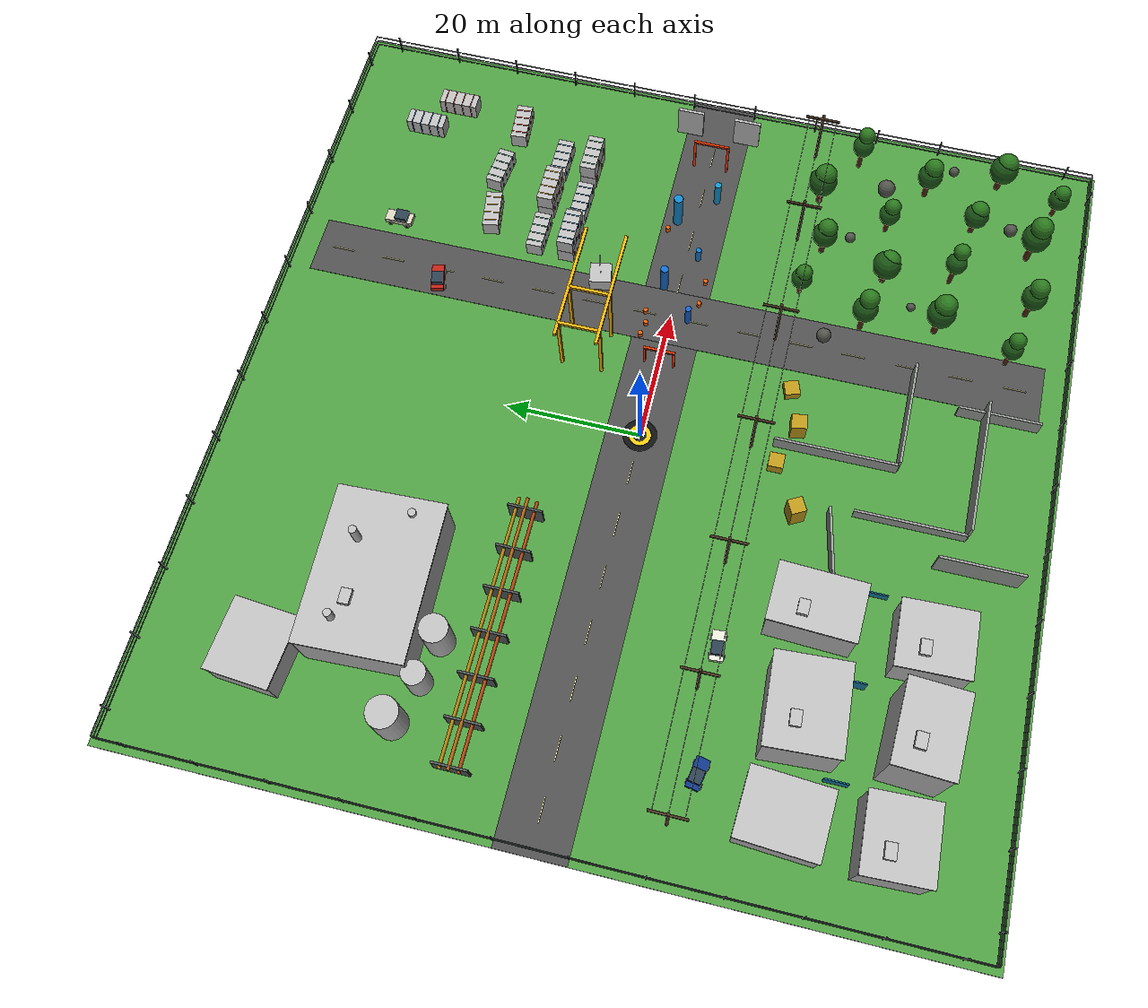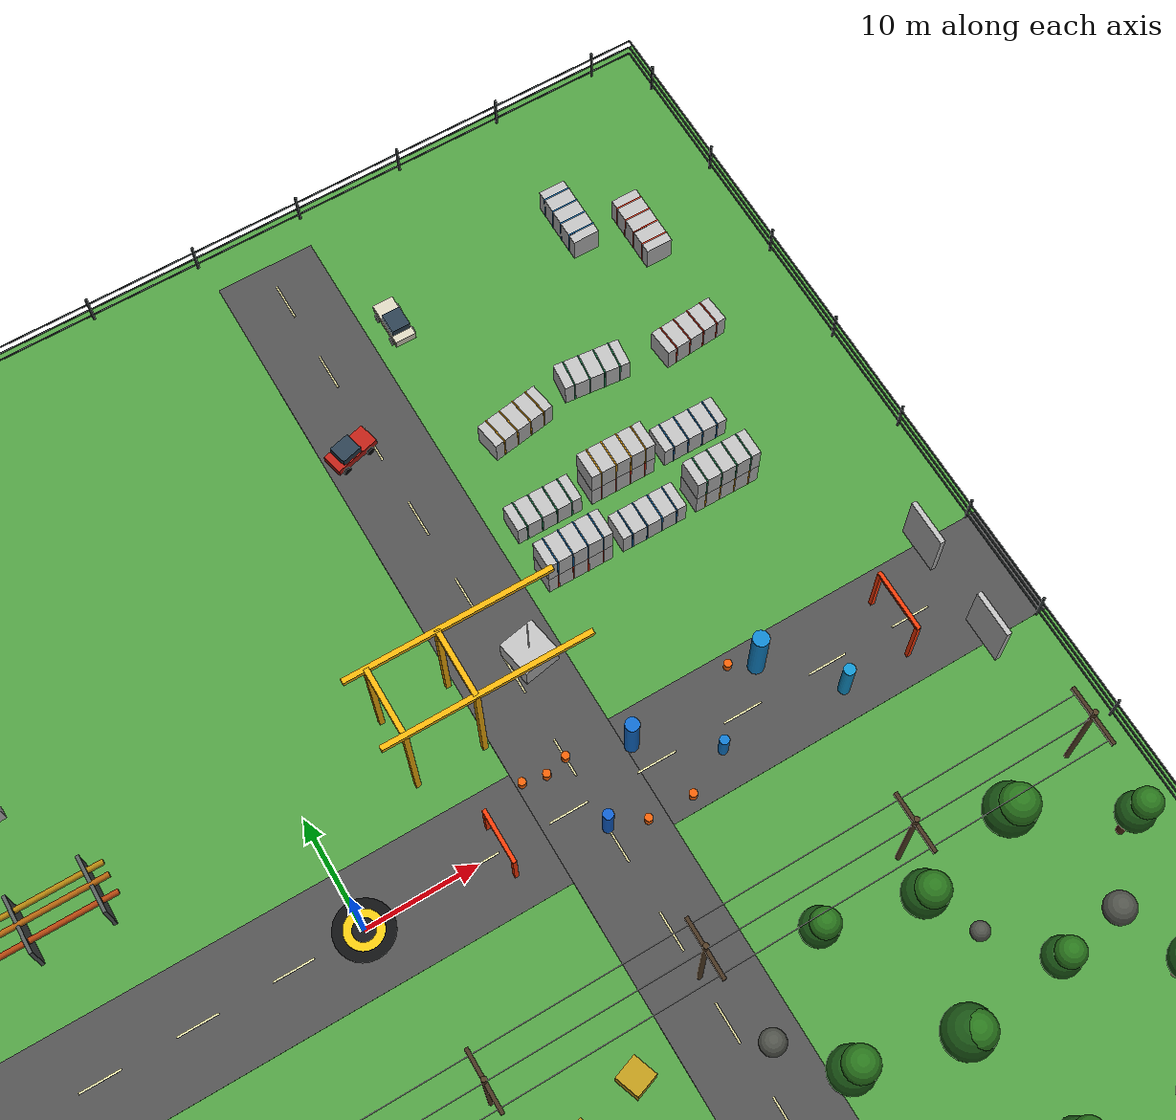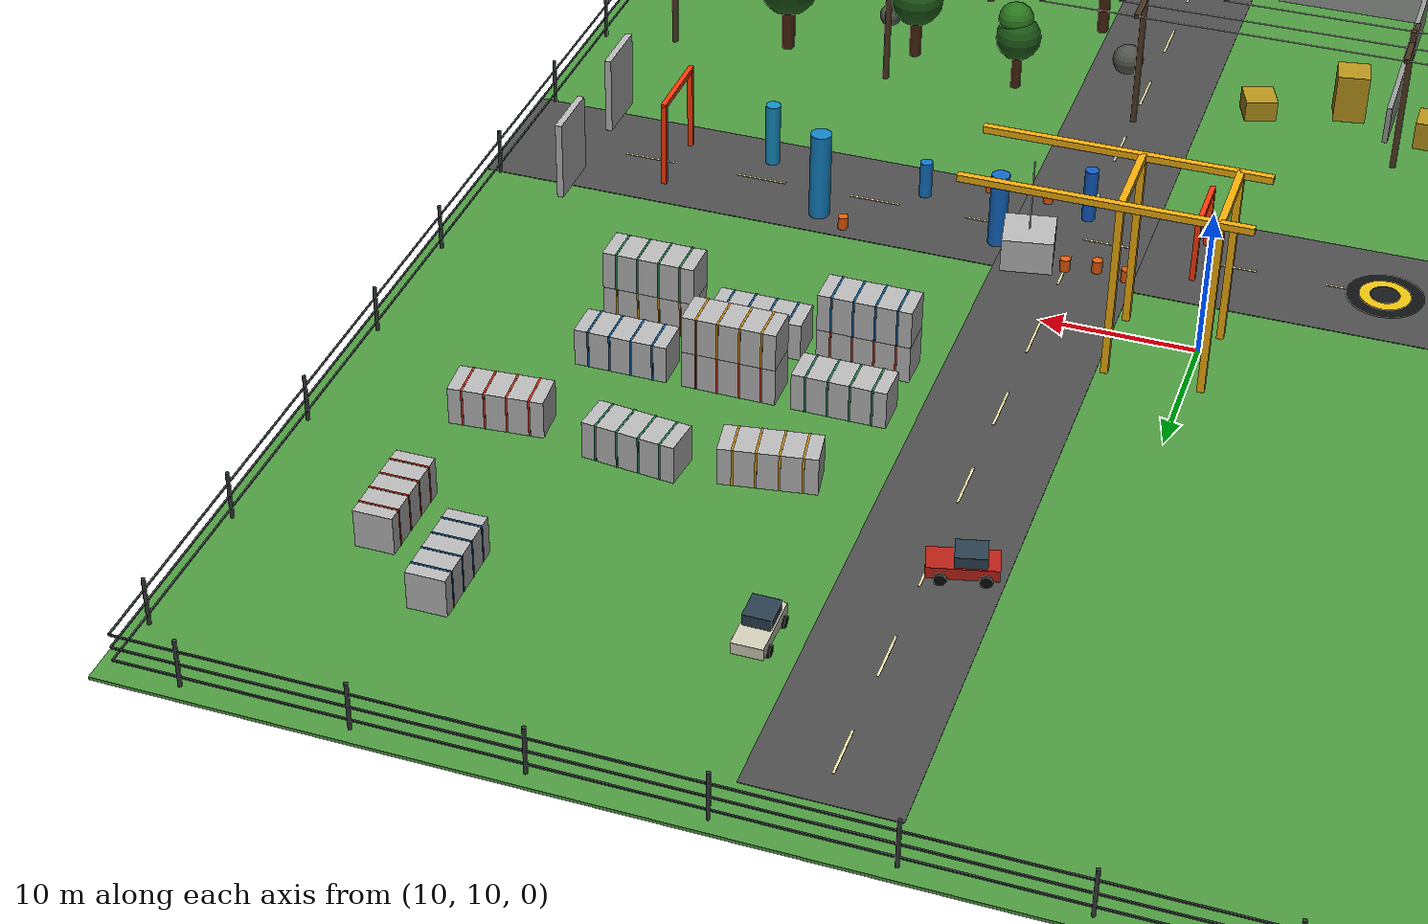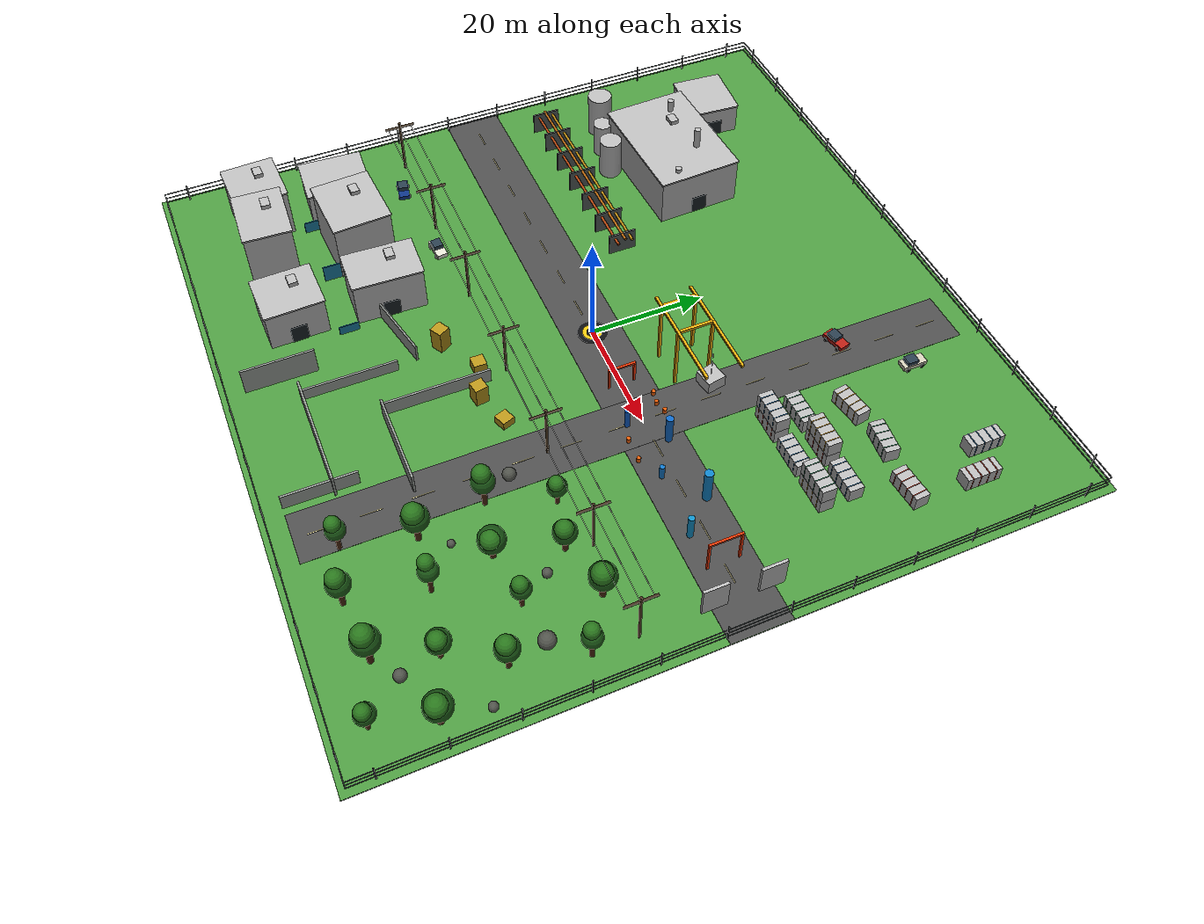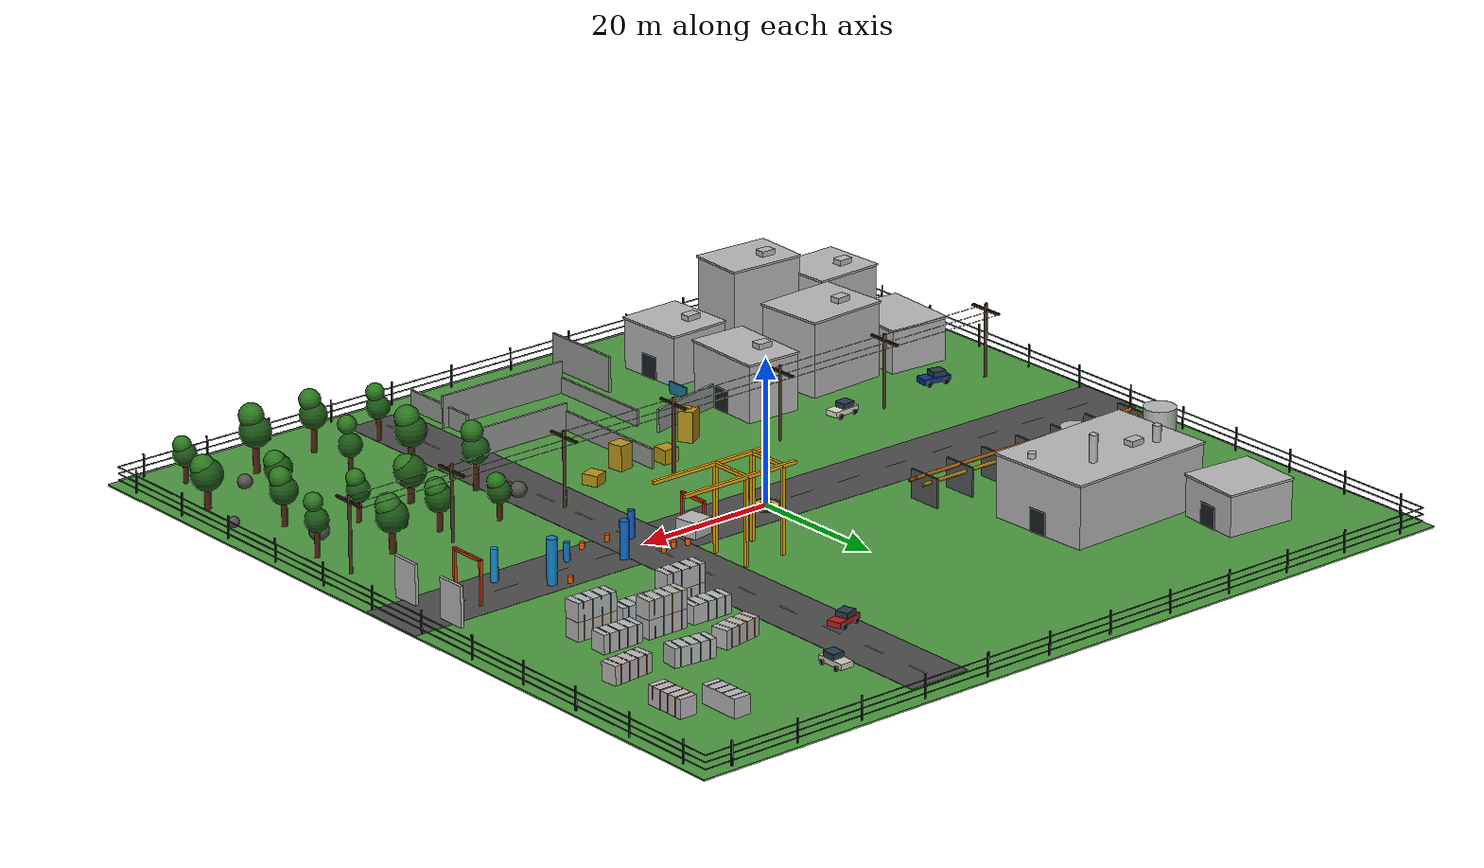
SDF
<?xml version='1.0' encoding='utf-8'?>
<sdf version="1.6">
  <world name="uav_complex_120m">
    <gravity>0 0 -9.81</gravity>
    <magnetic_field>6e-06 2.3e-05 -4.2e-05</magnetic_field>
    <physics name="default_physics" type="ode">
      <max_step_size>0.001</max_step_size>
      <real_time_factor>1.0</real_time_factor>
      <real_time_update_rate>1000</real_time_update_rate>
      <ode>
        <solver>
          <type>quick</type>
          <iters>40</iters>
        </solver>
      </ode>
    </physics>
    <scene>
      <ambient>0.46 0.49 0.52 1</ambient>
      <background>0.66 0.78 0.90 1</background>
      <shadows>true</shadows>
      <grid>false</grid>
      <fog>
        <type>linear</type>
        <color>0.72 0.79 0.83 1</color>
        <start>120</start>
        <end>240</end>
      </fog>
    </scene>
    <light name="sun" type="directional">
      <pose>0 0 80 0 0 0</pose>
      <cast_shadows>true</cast_shadows>
      <diffuse>0.94 0.90 0.82 1</diffuse>
      <specular>0.25 0.25 0.22 1</specular>
      <direction>-0.42 0.18 -0.89</direction>
    </light>
    <!--120 x 120 m textured base and crossing roads-->
    <model name="terrain">
      <static>true</static>
      <self_collide>false</self_collide>
      <link name="body">
        <pose>0 0 -0.1 0 0 0</pose>
        <collision name="collision">
          <geometry>
            <box>
              <size>120 120 0.2</size>
            </box>
          </geometry>
          <laser_retro>100</laser_retro>
          <surface>
            <friction>
              <ode>
                <mu>1.0</mu>
                <mu2>1.0</mu2>
              </ode>
            </friction>
          </surface>
        </collision>
        <visual name="visual">
          <cast_shadows>false</cast_shadows>
          <geometry>
            <box>
              <size>120 120 0.2</size>
            </box>
          </geometry>
          <material>
            <script>
              <uri>model://uav_complex_scene/materials/scripts</uri>
              <uri>model://uav_complex_scene/materials/textures</uri>
              <name>UAVComplex/Grass</name>
            </script>
          </material>
        </visual>
      </link>
    </model>
    <model name="main_road">
      <static>true</static>
      <self_collide>false</self_collide>
      <link name="body">
        <pose>0 0 0.018 0 0 0</pose>
        <visual name="visual">
          <cast_shadows>false</cast_shadows>
          <geometry>
            <box>
              <size>120 10 0.035</size>
            </box>
          </geometry>
          <material>
            <script>
              <uri>model://uav_complex_scene/materials/scripts</uri>
              <uri>model://uav_complex_scene/materials/textures</uri>
              <name>UAVComplex/Asphalt</name>
            </script>
          </material>
        </visual>
      </link>
    </model>
    <model name="cross_road">
      <static>true</static>
      <self_collide>false</self_collide>
      <link name="body">
        <pose>20 0 0.021 0 0 0</pose>
        <visual name="visual">
          <cast_shadows>false</cast_shadows>
          <geometry>
            <box>
              <size>9 112 0.04</size>
            </box>
          </geometry>
          <material>
            <script>
              <uri>model://uav_complex_scene/materials/scripts</uri>
              <uri>model://uav_complex_scene/materials/textures</uri>
              <name>UAVComplex/Asphalt</name>
            </script>
          </material>
        </visual>
      </link>
    </model>
    <model name="road_markings">
      <static>true</static>
      <self_collide>false</self_collide>
      <link name="dash_x_0">
        <pose>-54 0 0.052 0 0 0</pose>
        <visual name="visual">
          <cast_shadows>false</cast_shadows>
          <geometry>
            <box>
              <size>3.5 0.16 0.018</size>
            </box>
          </geometry>
          <material>
            <ambient>0.95 0.9 0.66 1</ambient>
            <diffuse>0.95 0.9 0.66 1</diffuse>
            <specular>0.08 0.08 0.08 1</specular>
          </material>
        </visual>
      </link>
      <link name="dash_x_1">
        <pose>-46 0 0.052 0 0 0</pose>
        <visual name="visual">
          <cast_shadows>false</cast_shadows>
          <geometry>
            <box>
              <size>3.5 0.16 0.018</size>
            </box>
          </geometry>
          <material>
            <ambient>0.95 0.9 0.66 1</ambient>
            <diffuse>0.95 0.9 0.66 1</diffuse>
            <specular>0.08 0.08 0.08 1</specular>
          </material>
        </visual>
      </link>
      <link name="dash_x_2">
        <pose>-38 0 0.052 0 0 0</pose>
        <visual name="visual">
          <cast_shadows>false</cast_shadows>
          <geometry>
            <box>
              <size>3.5 0.16 0.018</size>
            </box>
          </geometry>
          <material>
            <ambient>0.95 0.9 0.66 1</ambient>
            <diffuse>0.95 0.9 0.66 1</diffuse>
            <specular>0.08 0.08 0.08 1</specular>
          </material>
        </visual>
      </link>
      <link name="dash_x_3">
        <pose>-30 0 0.052 0 0 0</pose>
        <visual name="visual">
          <cast_shadows>false</cast_shadows>
          <geometry>
            <box>
              <size>3.5 0.16 0.018</size>
            </box>
          </geometry>
          <material>
            <ambient>0.95 0.9 0.66 1</ambient>
            <diffuse>0.95 0.9 0.66 1</diffuse>
            <specular>0.08 0.08 0.08 1</specular>
          </material>
        </visual>
      </link>
      <link name="dash_x_4">
        <pose>-22 0 0.052 0 0 0</pose>
        <visual name="visual">
          <cast_shadows>false</cast_shadows>
          <geometry>
            <box>
              <size>3.5 0.16 0.018</size>
            </box>
          </geometry>
          <material>
            <ambient>0.95 0.9 0.66 1</ambient>
            <diffuse>0.95 0.9 0.66 1</diffuse>
            <specular>0.08 0.08 0.08 1</specular>
          </material>
        </visual>
      </link>
      <link name="dash_x_5">
        <pose>-14 0 0.052 0 0 0</pose>
        <visual name="visual">
          <cast_shadows>false</cast_shadows>
          <geometry>
            <box>
              <size>3.5 0.16 0.018</size>
            </box>
          </geometry>
          <material>
            <ambient>0.95 0.9 0.66 1</ambient>
            <diffuse>0.95 0.9 0.66 1</diffuse>
            <specular>0.08 0.08 0.08 1</specular>
          </material>
        </visual>
      </link>
      <link name="dash_x_6">
        <pose>-6 0 0.052 0 0 0</pose>
        <visual name="visual">
          <cast_shadows>false</cast_shadows>
          <geometry>
            <box>
              <size>3.5 0.16 0.018</size>
            </box>
          </geometry>
          <material>
            <ambient>0.95 0.9 0.66 1</ambient>
            <diffuse>0.95 0.9 0.66 1</diffuse>
            <specular>0.08 0.08 0.08 1</specular>
          </material>
        </visual>
      </link>
      <link name="dash_x_7">
        <pose>2 0 0.052 0 0 0</pose>
        <visual name="visual">
          <cast_shadows>false</cast_shadows>
          <geometry>
            <box>
              <size>3.5 0.16 0.018</size>
            </box>
          </geometry>
          <material>
            <ambient>0.95 0.9 0.66 1</ambient>
            <diffuse>0.95 0.9 0.66 1</diffuse>
            <specular>0.08 0.08 0.08 1</specular>
          </material>
        </visual>
      </link>
      <link name="dash_x_8">
        <pose>10 0 0.052 0 0 0</pose>
        <visual name="visual">
          <cast_shadows>false</cast_shadows>
          <geometry>
            <box>
              <size>3.5 0.16 0.018</size>
            </box>
          </geometry>
          <material>
            <ambient>0.95 0.9 0.66 1</ambient>
            <diffuse>0.95 0.9 0.66 1</diffuse>
            <specular>0.08 0.08 0.08 1</specular>
          </material>
        </visual>
      </link>
      <link name="dash_x_9">
        <pose>18 0 0.052 0 0 0</pose>
        <visual name="visual">
          <cast_shadows>false</cast_shadows>
          <geometry>
            <box>
              <size>3.5 0.16 0.018</size>
            </box>
          </geometry>
          <material>
            <ambient>0.95 0.9 0.66 1</ambient>
            <diffuse>0.95 0.9 0.66 1</diffuse>
            <specular>0.08 0.08 0.08 1</specular>
          </material>
        </visual>
      </link>
      <link name="dash_x_10">
        <pose>26 0 0.052 0 0 0</pose>
        <visual name="visual">
          <cast_shadows>false</cast_shadows>
          <geometry>
            <box>
              <size>3.5 0.16 0.018</size>
            </box>
          </geometry>
          <material>
            <ambient>0.95 0.9 0.66 1</ambient>
            <diffuse>0.95 0.9 0.66 1</diffuse>
            <specular>0.08 0.08 0.08 1</specular>
          </material>
        </visual>
      </link>
      <link name="dash_x_11">
        <pose>34 0 0.052 0 0 0</pose>
        <visual name="visual">
          <cast_shadows>false</cast_shadows>
          <geometry>
            <box>
              <size>3.5 0.16 0.018</size>
            </box>
          </geometry>
          <material>
            <ambient>0.95 0.9 0.66 1</ambient>
            <diffuse>0.95 0.9 0.66 1</diffuse>
            <specular>0.08 0.08 0.08 1</specular>
          </material>
        </visual>
      </link>
      <link name="dash_x_12">
        <pose>42 0 0.052 0 0 0</pose>
        <visual name="visual">
          <cast_shadows>false</cast_shadows>
          <geometry>
            <box>
              <size>3.5 0.16 0.018</size>
            </box>
          </geometry>
          <material>
            <ambient>0.95 0.9 0.66 1</ambient>
            <diffuse>0.95 0.9 0.66 1</diffuse>
            <specular>0.08 0.08 0.08 1</specular>
          </material>
        </visual>
      </link>
      <link name="dash_x_13">
        <pose>50 0 0.052 0 0 0</pose>
        <visual name="visual">
          <cast_shadows>false</cast_shadows>
          <geometry>
            <box>
              <size>3.5 0.16 0.018</size>
            </box>
          </geometry>
          <material>
            <ambient>0.95 0.9 0.66 1</ambient>
            <diffuse>0.95 0.9 0.66 1</diffuse>
            <specular>0.08 0.08 0.08 1</specular>
          </material>
        </visual>
      </link>
      <link name="dash_y_0">
        <pose>20 -52 0.055 0 0 0</pose>
        <visual name="visual">
          <cast_shadows>false</cast_shadows>
          <geometry>
            <box>
              <size>0.16 3.5 0.018</size>
            </box>
          </geometry>
          <material>
            <ambient>0.95 0.9 0.66 1</ambient>
            <diffuse>0.95 0.9 0.66 1</diffuse>
            <specular>0.08 0.08 0.08 1</specular>
          </material>
        </visual>
      </link>
      <link name="dash_y_1">
        <pose>20 -44 0.055 0 0 0</pose>
        <visual name="visual">
          <cast_shadows>false</cast_shadows>
          <geometry>
            <box>
              <size>0.16 3.5 0.018</size>
            </box>
          </geometry>
          <material>
            <ambient>0.95 0.9 0.66 1</ambient>
            <diffuse>0.95 0.9 0.66 1</diffuse>
            <specular>0.08 0.08 0.08 1</specular>
          </material>
        </visual>
      </link>
      <link name="dash_y_2">
        <pose>20 -36 0.055 0 0 0</pose>
        <visual name="visual">
          <cast_shadows>false</cast_shadows>
          <geometry>
            <box>
              <size>0.16 3.5 0.018</size>
            </box>
          </geometry>
          <material>
            <ambient>0.95 0.9 0.66 1</ambient>
            <diffuse>0.95 0.9 0.66 1</diffuse>
            <specular>0.08 0.08 0.08 1</specular>
          </material>
        </visual>
      </link>
      <link name="dash_y_3">
        <pose>20 -28 0.055 0 0 0</pose>
        <visual name="visual">
          <cast_shadows>false</cast_shadows>
          <geometry>
            <box>
              <size>0.16 3.5 0.018</size>
            </box>
          </geometry>
          <material>
            <ambient>0.95 0.9 0.66 1</ambient>
            <diffuse>0.95 0.9 0.66 1</diffuse>
            <specular>0.08 0.08 0.08 1</specular>
          </material>
        </visual>
      </link>
      <link name="dash_y_4">
        <pose>20 -20 0.055 0 0 0</pose>
        <visual name="visual">
          <cast_shadows>false</cast_shadows>
          <geometry>
            <box>
              <size>0.16 3.5 0.018</size>
            </box>
          </geometry>
          <material>
            <ambient>0.95 0.9 0.66 1</ambient>
            <diffuse>0.95 0.9 0.66 1</diffuse>
            <specular>0.08 0.08 0.08 1</specular>
          </material>
        </visual>
      </link>
      <link name="dash_y_5">
        <pose>20 -12 0.055 0 0 0</pose>
        <visual name="visual">
          <cast_shadows>false</cast_shadows>
          <geometry>
            <box>
              <size>0.16 3.5 0.018</size>
            </box>
          </geometry>
          <material>
            <ambient>0.95 0.9 0.66 1</ambient>
            <diffuse>0.95 0.9 0.66 1</diffuse>
            <specular>0.08 0.08 0.08 1</specular>
          </material>
        </visual>
      </link>
      <link name="dash_y_6">
        <pose>20 -4 0.055 0 0 0</pose>
        <visual name="visual">
          <cast_shadows>false</cast_shadows>
          <geometry>
            <box>
              <size>0.16 3.5 0.018</size>
            </box>
          </geometry>
          <material>
            <ambient>0.95 0.9 0.66 1</ambient>
            <diffuse>0.95 0.9 0.66 1</diffuse>
            <specular>0.08 0.08 0.08 1</specular>
          </material>
        </visual>
      </link>
      <link name="dash_y_7">
        <pose>20 4 0.055 0 0 0</pose>
        <visual name="visual">
          <cast_shadows>false</cast_shadows>
          <geometry>
            <box>
              <size>0.16 3.5 0.018</size>
            </box>
          </geometry>
          <material>
            <ambient>0.95 0.9 0.66 1</ambient>
            <diffuse>0.95 0.9 0.66 1</diffuse>
            <specular>0.08 0.08 0.08 1</specular>
          </material>
        </visual>
      </link>
      <link name="dash_y_8">
        <pose>20 12 0.055 0 0 0</pose>
        <visual name="visual">
          <cast_shadows>false</cast_shadows>
          <geometry>
            <box>
              <size>0.16 3.5 0.018</size>
            </box>
          </geometry>
          <material>
            <ambient>0.95 0.9 0.66 1</ambient>
            <diffuse>0.95 0.9 0.66 1</diffuse>
            <specular>0.08 0.08 0.08 1</specular>
          </material>
        </visual>
      </link>
      <link name="dash_y_9">
        <pose>20 20 0.055 0 0 0</pose>
        <visual name="visual">
          <cast_shadows>false</cast_shadows>
          <geometry>
            <box>
              <size>0.16 3.5 0.018</size>
            </box>
          </geometry>
          <material>
            <ambient>0.95 0.9 0.66 1</ambient>
            <diffuse>0.95 0.9 0.66 1</diffuse>
            <specular>0.08 0.08 0.08 1</specular>
          </material>
        </visual>
      </link>
      <link name="dash_y_10">
        <pose>20 28 0.055 0 0 0</pose>
        <visual name="visual">
          <cast_shadows>false</cast_shadows>
          <geometry>
            <box>
              <size>0.16 3.5 0.018</size>
            </box>
          </geometry>
          <material>
            <ambient>0.95 0.9 0.66 1</ambient>
            <diffuse>0.95 0.9 0.66 1</diffuse>
            <specular>0.08 0.08 0.08 1</specular>
          </material>
        </visual>
      </link>
      <link name="dash_y_11">
        <pose>20 36 0.055 0 0 0</pose>
        <visual name="visual">
          <cast_shadows>false</cast_shadows>
          <geometry>
            <box>
              <size>0.16 3.5 0.018</size>
            </box>
          </geometry>
          <material>
            <ambient>0.95 0.9 0.66 1</ambient>
            <diffuse>0.95 0.9 0.66 1</diffuse>
            <specular>0.08 0.08 0.08 1</specular>
          </material>
        </visual>
      </link>
      <link name="dash_y_12">
        <pose>20 44 0.055 0 0 0</pose>
        <visual name="visual">
          <cast_shadows>false</cast_shadows>
          <geometry>
            <box>
              <size>0.16 3.5 0.018</size>
            </box>
          </geometry>
          <material>
            <ambient>0.95 0.9 0.66 1</ambient>
            <diffuse>0.95 0.9 0.66 1</diffuse>
            <specular>0.08 0.08 0.08 1</specular>
          </material>
        </visual>
      </link>
      <link name="dash_y_13">
        <pose>20 52 0.055 0 0 0</pose>
        <visual name="visual">
          <cast_shadows>false</cast_shadows>
          <geometry>
            <box>
              <size>0.16 3.5 0.018</size>
            </box>
          </geometry>
          <material>
            <ambient>0.95 0.9 0.66 1</ambient>
            <diffuse>0.95 0.9 0.66 1</diffuse>
            <specular>0.08 0.08 0.08 1</specular>
          </material>
        </visual>
      </link>
    </model>
    <model name="takeoff_pad">
      <static>true</static>
      <self_collide>false</self_collide>
      <link name="outer">
        <pose>0 0 0.04 0 0 0</pose>
        <visual name="visual">
          <cast_shadows>true</cast_shadows>
          <geometry>
            <cylinder>
              <radius>2.5</radius>
              <length>0.045</length>
            </cylinder>
          </geometry>
          <material>
            <ambient>0.055 0.06 0.065 1</ambient>
            <diffuse>0.055 0.06 0.065 1</diffuse>
            <specular>0.08 0.08 0.08 1</specular>
          </material>
        </visual>
      </link>
      <link name="inner">
        <pose>0 0 0.07 0 0 0</pose>
        <visual name="visual">
          <cast_shadows>true</cast_shadows>
          <geometry>
            <cylinder>
              <radius>1.65</radius>
              <length>0.055</length>
            </cylinder>
          </geometry>
          <material>
            <ambient>0.92 0.76 0.06 1</ambient>
            <diffuse>0.92 0.76 0.06 1</diffuse>
            <specular>0.08 0.08 0.08 1</specular>
          </material>
        </visual>
      </link>
      <link name="center">
        <pose>0 0 0.1 0 0 0</pose>
        <visual name="visual">
          <cast_shadows>true</cast_shadows>
          <geometry>
            <cylinder>
              <radius>0.95</radius>
              <length>0.065</length>
            </cylinder>
          </geometry>
          <material>
            <ambient>0.08 0.09 0.1 1</ambient>
            <diffuse>0.08 0.09 0.1 1</diffuse>
            <specular>0.08 0.08 0.08 1</specular>
          </material>
        </visual>
      </link>
    </model>
    <!--Perimeter fence: thin rails and posts remain visible to lidar-->
    <model name="perimeter_fence">
      <static>true</static>
      <self_collide>false</self_collide>
      <link name="post_n_0">
        <pose>-55 59 1.6 0 0 0</pose>
        <collision name="collision">
          <geometry>
            <cylinder>
              <radius>0.12</radius>
              <length>3.2</length>
            </cylinder>
          </geometry>
          <laser_retro>100</laser_retro>
          <surface>
            <friction>
              <ode>
                <mu>1.0</mu>
                <mu2>1.0</mu2>
              </ode>
            </friction>
          </surface>
        </collision>
        <visual name="visual">
          <cast_shadows>true</cast_shadows>
          <geometry>
            <cylinder>
              <radius>0.12</radius>
              <length>3.2</length>
            </cylinder>
          </geometry>
          <material>
            <ambient>0.2 0.22 0.22 1</ambient>
            <diffuse>0.2 0.22 0.22 1</diffuse>
            <specular>0.08 0.08 0.08 1</specular>
          </material>
        </visual>
      </link>
      <link name="post_s_0">
        <pose>-55 -59 1.6 0 0 0</pose>
        <collision name="collision">
          <geometry>
            <cylinder>
              <radius>0.12</radius>
              <length>3.2</length>
            </cylinder>
          </geometry>
          <laser_retro>100</laser_retro>
          <surface>
            <friction>
              <ode>
                <mu>1.0</mu>
                <mu2>1.0</mu2>
              </ode>
            </friction>
          </surface>
        </collision>
        <visual name="visual">
          <cast_shadows>true</cast_shadows>
          <geometry>
            <cylinder>
              <radius>0.12</radius>
              <length>3.2</length>
            </cylinder>
          </geometry>
          <material>
            <ambient>0.2 0.22 0.22 1</ambient>
            <diffuse>0.2 0.22 0.22 1</diffuse>
            <specular>0.08 0.08 0.08 1</specular>
          </material>
        </visual>
      </link>
      <link name="post_e_0">
        <pose>59 -55 1.6 0 0 0</pose>
        <collision name="collision">
          <geometry>
            <cylinder>
              <radius>0.12</radius>
              <length>3.2</length>
            </cylinder>
          </geometry>
          <laser_retro>100</laser_retro>
          <surface>
            <friction>
              <ode>
                <mu>1.0</mu>
                <mu2>1.0</mu2>
              </ode>
            </friction>
          </surface>
        </collision>
        <visual name="visual">
          <cast_shadows>true</cast_shadows>
          <geometry>
            <cylinder>
              <radius>0.12</radius>
              <length>3.2</length>
            </cylinder>
          </geometry>
          <material>
            <ambient>0.2 0.22 0.22 1</ambient>
            <diffuse>0.2 0.22 0.22 1</diffuse>
            <specular>0.08 0.08 0.08 1</specular>
          </material>
        </visual>
      </link>
      <link name="post_w_0">
        <pose>-59 -55 1.6 0 0 0</pose>
        <collision name="collision">
          <geometry>
            <cylinder>
              <radius>0.12</radius>
              <length>3.2</length>
            </cylinder>
          </geometry>
          <laser_retro>100</laser_retro>
          <surface>
            <friction>
              <ode>
                <mu>1.0</mu>
                <mu2>1.0</mu2>
              </ode>
            </friction>
          </surface>
        </collision>
        <visual name="visual">
          <cast_shadows>true</cast_shadows>
          <geometry>
            <cylinder>
              <radius>0.12</radius>
              <length>3.2</length>
            </cylinder>
          </geometry>
          <material>
            <ambient>0.2 0.22 0.22 1</ambient>
            <diffuse>0.2 0.22 0.22 1</diffuse>
            <specular>0.08 0.08 0.08 1</specular>
          </material>
        </visual>
      </link>
      <link name="post_n_1">
        <pose>-45 59 1.6 0 0 0</pose>
        <collision name="collision">
          <geometry>
            <cylinder>
              <radius>0.12</radius>
              <length>3.2</length>
            </cylinder>
          </geometry>
          <laser_retro>100</laser_retro>
          <surface>
            <friction>
              <ode>
                <mu>1.0</mu>
                <mu2>1.0</mu2>
              </ode>
            </friction>
          </surface>
        </collision>
        <visual name="visual">
          <cast_shadows>true</cast_shadows>
          <geometry>
            <cylinder>
              <radius>0.12</radius>
              <length>3.2</length>
            </cylinder>
          </geometry>
          <material>
            <ambient>0.2 0.22 0.22 1</ambient>
            <diffuse>0.2 0.22 0.22 1</diffuse>
            <specular>0.08 0.08 0.08 1</specular>
          </material>
        </visual>
      </link>
      <link name="post_s_1">
        <pose>-45 -59 1.6 0 0 0</pose>
        <collision name="collision">
          <geometry>
            <cylinder>
              <radius>0.12</radius>
              <length>3.2</length>
            </cylinder>
          </geometry>
          <laser_retro>100</laser_retro>
          <surface>
            <friction>
              <ode>
                <mu>1.0</mu>
                <mu2>1.0</mu2>
              </ode>
            </friction>
          </surface>
        </collision>
        <visual name="visual">
          <cast_shadows>true</cast_shadows>
          <geometry>
            <cylinder>
              <radius>0.12</radius>
              <length>3.2</length>
            </cylinder>
          </geometry>
          <material>
            <ambient>0.2 0.22 0.22 1</ambient>
            <diffuse>0.2 0.22 0.22 1</diffuse>
            <specular>0.08 0.08 0.08 1</specular>
          </material>
        </visual>
      </link>
      <link name="post_e_1">
        <pose>59 -45 1.6 0 0 0</pose>
        <collision name="collision">
          <geometry>
            <cylinder>
              <radius>0.12</radius>
              <length>3.2</length>
            </cylinder>
          </geometry>
          <laser_retro>100</laser_retro>
          <surface>
            <friction>
              <ode>
                <mu>1.0</mu>
                <mu2>1.0</mu2>
              </ode>
            </friction>
          </surface>
        </collision>
        <visual name="visual">
          <cast_shadows>true</cast_shadows>
          <geometry>
            <cylinder>
              <radius>0.12</radius>
              <length>3.2</length>
            </cylinder>
          </geometry>
          <material>
            <ambient>0.2 0.22 0.22 1</ambient>
            <diffuse>0.2 0.22 0.22 1</diffuse>
            <specular>0.08 0.08 0.08 1</specular>
          </material>
        </visual>
      </link>
      <link name="post_w_1">
        <pose>-59 -45 1.6 0 0 0</pose>
        <collision name="collision">
          <geometry>
            <cylinder>
              <radius>0.12</radius>
              <length>3.2</length>
            </cylinder>
          </geometry>
          <laser_retro>100</laser_retro>
          <surface>
            <friction>
              <ode>
                <mu>1.0</mu>
                <mu2>1.0</mu2>
              </ode>
            </friction>
          </surface>
        </collision>
        <visual name="visual">
          <cast_shadows>true</cast_shadows>
          <geometry>
            <cylinder>
              <radius>0.12</radius>
              <length>3.2</length>
            </cylinder>
          </geometry>
          <material>
            <ambient>0.2 0.22 0.22 1</ambient>
            <diffuse>0.2 0.22 0.22 1</diffuse>
            <specular>0.08 0.08 0.08 1</specular>
          </material>
        </visual>
      </link>
      <link name="post_n_2">
        <pose>-35 59 1.6 0 0 0</pose>
        <collision name="collision">
          <geometry>
            <cylinder>
              <radius>0.12</radius>
              <length>3.2</length>
            </cylinder>
          </geometry>
          <laser_retro>100</laser_retro>
          <surface>
            <friction>
              <ode>
                <mu>1.0</mu>
                <mu2>1.0</mu2>
              </ode>
            </friction>
          </surface>
        </collision>
        <visual name="visual">
          <cast_shadows>true</cast_shadows>
          <geometry>
            <cylinder>
              <radius>0.12</radius>
              <length>3.2</length>
            </cylinder>
          </geometry>
          <material>
            <ambient>0.2 0.22 0.22 1</ambient>
            <diffuse>0.2 0.22 0.22 1</diffuse>
            <specular>0.08 0.08 0.08 1</specular>
          </material>
        </visual>
      </link>
      <link name="post_s_2">
        <pose>-35 -59 1.6 0 0 0</pose>
        <collision name="collision">
          <geometry>
            <cylinder>
              <radius>0.12</radius>
              <length>3.2</length>
            </cylinder>
          </geometry>
          <laser_retro>100</laser_retro>
          <surface>
            <friction>
              <ode>
                <mu>1.0</mu>
                <mu2>1.0</mu2>
              </ode>
            </friction>
          </surface>
        </collision>
        <visual name="visual">
          <cast_shadows>true</cast_shadows>
          <geometry>
            <cylinder>
              <radius>0.12</radius>
              <length>3.2</length>
            </cylinder>
          </geometry>
          <material>
            <ambient>0.2 0.22 0.22 1</ambient>
            <diffuse>0.2 0.22 0.22 1</diffuse>
            <specular>0.08 0.08 0.08 1</specular>
          </material>
        </visual>
      </link>
      <link name="post_e_2">
        <pose>59 -35 1.6 0 0 0</pose>
        <collision name="collision">
          <geometry>
            <cylinder>
              <radius>0.12</radius>
              <length>3.2</length>
            </cylinder>
          </geometry>
          <laser_retro>100</laser_retro>
          <surface>
            <friction>
              <ode>
                <mu>1.0</mu>
                <mu2>1.0</mu2>
              </ode>
            </friction>
          </surface>
        </collision>
        <visual name="visual">
          <cast_shadows>true</cast_shadows>
          <geometry>
            <cylinder>
              <radius>0.12</radius>
              <length>3.2</length>
            </cylinder>
          </geometry>
          <material>
            <ambient>0.2 0.22 0.22 1</ambient>
            <diffuse>0.2 0.22 0.22 1</diffuse>
            <specular>0.08 0.08 0.08 1</specular>
          </material>
        </visual>
      </link>
      <link name="post_w_2">
        <pose>-59 -35 1.6 0 0 0</pose>
        <collision name="collision">
          <geometry>
            <cylinder>
              <radius>0.12</radius>
              <length>3.2</length>
            </cylinder>
          </geometry>
          <laser_retro>100</laser_retro>
          <surface>
            <friction>
              <ode>
                <mu>1.0</mu>
                <mu2>1.0</mu2>
              </ode>
            </friction>
          </surface>
        </collision>
        <visual name="visual">
          <cast_shadows>true</cast_shadows>
          <geometry>
            <cylinder>
              <radius>0.12</radius>
              <length>3.2</length>
            </cylinder>
          </geometry>
          <material>
            <ambient>0.2 0.22 0.22 1</ambient>
            <diffuse>0.2 0.22 0.22 1</diffuse>
            <specular>0.08 0.08 0.08 1</specular>
          </material>
        </visual>
      </link>
      <link name="post_n_3">
        <pose>-25 59 1.6 0 0 0</pose>
        <collision name="collision">
          <geometry>
            <cylinder>
              <radius>0.12</radius>
              <length>3.2</length>
            </cylinder>
          </geometry>
          <laser_retro>100</laser_retro>
          <surface>
            <friction>
              <ode>
                <mu>1.0</mu>
                <mu2>1.0</mu2>
              </ode>
            </friction>
          </surface>
        </collision>
        <visual name="visual">
          <cast_shadows>true</cast_shadows>
          <geometry>
            <cylinder>
              <radius>0.12</radius>
              <length>3.2</length>
            </cylinder>
          </geometry>
          <material>
            <ambient>0.2 0.22 0.22 1</ambient>
            <diffuse>0.2 0.22 0.22 1</diffuse>
            <specular>0.08 0.08 0.08 1</specular>
          </material>
        </visual>
      </link>
      <link name="post_s_3">
        <pose>-25 -59 1.6 0 0 0</pose>
        <collision name="collision">
          <geometry>
            <cylinder>
              <radius>0.12</radius>
              <length>3.2</length>
            </cylinder>
          </geometry>
          <laser_retro>100</laser_retro>
          <surface>
            <friction>
              <ode>
                <mu>1.0</mu>
                <mu2>1.0</mu2>
              </ode>
            </friction>
          </surface>
        </collision>
        <visual name="visual">
          <cast_shadows>true</cast_shadows>
          <geometry>
            <cylinder>
              <radius>0.12</radius>
              <length>3.2</length>
            </cylinder>
          </geometry>
          <material>
            <ambient>0.2 0.22 0.22 1</ambient>
            <diffuse>0.2 0.22 0.22 1</diffuse>
            <specular>0.08 0.08 0.08 1</specular>
          </material>
        </visual>
      </link>
      <link name="post_e_3">
        <pose>59 -25 1.6 0 0 0</pose>
        <collision name="collision">
          <geometry>
            <cylinder>
              <radius>0.12</radius>
              <length>3.2</length>
            </cylinder>
          </geometry>
          <laser_retro>100</laser_retro>
          <surface>
            <friction>
              <ode>
                <mu>1.0</mu>
                <mu2>1.0</mu2>
              </ode>
            </friction>
          </surface>
        </collision>
        <visual name="visual">
          <cast_shadows>true</cast_shadows>
          <geometry>
            <cylinder>
              <radius>0.12</radius>
              <length>3.2</length>
            </cylinder>
          </geometry>
          <material>
            <ambient>0.2 0.22 0.22 1</ambient>
            <diffuse>0.2 0.22 0.22 1</diffuse>
            <specular>0.08 0.08 0.08 1</specular>
          </material>
        </visual>
      </link>
      <link name="post_w_3">
        <pose>-59 -25 1.6 0 0 0</pose>
        <collision name="collision">
          <geometry>
            <cylinder>
              <radius>0.12</radius>
              <length>3.2</length>
            </cylinder>
          </geometry>
          <laser_retro>100</laser_retro>
          <surface>
            <friction>
              <ode>
                <mu>1.0</mu>
                <mu2>1.0</mu2>
              </ode>
            </friction>
          </surface>
        </collision>
        <visual name="visual">
          <cast_shadows>true</cast_shadows>
          <geometry>
            <cylinder>
              <radius>0.12</radius>
              <length>3.2</length>
            </cylinder>
          </geometry>
          <material>
            <ambient>0.2 0.22 0.22 1</ambient>
            <diffuse>0.2 0.22 0.22 1</diffuse>
            <specular>0.08 0.08 0.08 1</specular>
          </material>
        </visual>
      </link>
      <link name="post_n_4">
        <pose>-15 59 1.6 0 0 0</pose>
        <collision name="collision">
          <geometry>
            <cylinder>
              <radius>0.12</radius>
              <length>3.2</length>
            </cylinder>
          </geometry>
          <laser_retro>100</laser_retro>
          <surface>
            <friction>
              <ode>
                <mu>1.0</mu>
                <mu2>1.0</mu2>
              </ode>
            </friction>
          </surface>
        </collision>
        <visual name="visual">
          <cast_shadows>true</cast_shadows>
          <geometry>
            <cylinder>
              <radius>0.12</radius>
              <length>3.2</length>
            </cylinder>
          </geometry>
          <material>
            <ambient>0.2 0.22 0.22 1</ambient>
            <diffuse>0.2 0.22 0.22 1</diffuse>
            <specular>0.08 0.08 0.08 1</specular>
          </material>
        </visual>
      </link>
      <link name="post_s_4">
        <pose>-15 -59 1.6 0 0 0</pose>
        <collision name="collision">
          <geometry>
            <cylinder>
              <radius>0.12</radius>
              <length>3.2</length>
            </cylinder>
          </geometry>
          <laser_retro>100</laser_retro>
          <surface>
            <friction>
              <ode>
                <mu>1.0</mu>
                <mu2>1.0</mu2>
              </ode>
            </friction>
          </surface>
        </collision>
        <visual name="visual">
          <cast_shadows>true</cast_shadows>
          <geometry>
            <cylinder>
              <radius>0.12</radius>
              <length>3.2</length>
            </cylinder>
          </geometry>
          <material>
            <ambient>0.2 0.22 0.22 1</ambient>
            <diffuse>0.2 0.22 0.22 1</diffuse>
            <specular>0.08 0.08 0.08 1</specular>
          </material>
        </visual>
      </link>
      <link name="post_e_4">
        <pose>59 -15 1.6 0 0 0</pose>
        <collision name="collision">
          <geometry>
            <cylinder>
              <radius>0.12</radius>
              <length>3.2</length>
            </cylinder>
          </geometry>
          <laser_retro>100</laser_retro>
          <surface>
            <friction>
              <ode>
                <mu>1.0</mu>
                <mu2>1.0</mu2>
              </ode>
            </friction>
          </surface>
        </collision>
        <visual name="visual">
          <cast_shadows>true</cast_shadows>
          <geometry>
            <cylinder>
              <radius>0.12</radius>
              <length>3.2</length>
            </cylinder>
          </geometry>
          <material>
            <ambient>0.2 0.22 0.22 1</ambient>
            <diffuse>0.2 0.22 0.22 1</diffuse>
            <specular>0.08 0.08 0.08 1</specular>
          </material>
        </visual>
      </link>
      <link name="post_w_4">
        <pose>-59 -15 1.6 0 0 0</pose>
        <collision name="collision">
          <geometry>
            <cylinder>
              <radius>0.12</radius>
              <length>3.2</length>
            </cylinder>
          </geometry>
          <laser_retro>100</laser_retro>
          <surface>
            <friction>
              <ode>
                <mu>1.0</mu>
                <mu2>1.0</mu2>
              </ode>
            </friction>
          </surface>
        </collision>
        <visual name="visual">
          <cast_shadows>true</cast_shadows>
          <geometry>
            <cylinder>
              <radius>0.12</radius>
              <length>3.2</length>
            </cylinder>
          </geometry>
          <material>
            <ambient>0.2 0.22 0.22 1</ambient>
            <diffuse>0.2 0.22 0.22 1</diffuse>
            <specular>0.08 0.08 0.08 1</specular>
          </material>
        </visual>
      </link>
      <link name="post_n_5">
        <pose>-5 59 1.6 0 0 0</pose>
        <collision name="collision">
          <geometry>
            <cylinder>
              <radius>0.12</radius>
              <length>3.2</length>
            </cylinder>
          </geometry>
          <laser_retro>100</laser_retro>
          <surface>
            <friction>
              <ode>
                <mu>1.0</mu>
                <mu2>1.0</mu2>
              </ode>
            </friction>
          </surface>
        </collision>
        <visual name="visual">
          <cast_shadows>true</cast_shadows>
          <geometry>
            <cylinder>
              <radius>0.12</radius>
              <length>3.2</length>
            </cylinder>
          </geometry>
          <material>
            <ambient>0.2 0.22 0.22 1</ambient>
            <diffuse>0.2 0.22 0.22 1</diffuse>
            <specular>0.08 0.08 0.08 1</specular>
          </material>
        </visual>
      </link>
      <link name="post_s_5">
        <pose>-5 -59 1.6 0 0 0</pose>
        <collision name="collision">
          <geometry>
            <cylinder>
              <radius>0.12</radius>
              <length>3.2</length>
            </cylinder>
          </geometry>
          <laser_retro>100</laser_retro>
          <surface>
            <friction>
              <ode>
                <mu>1.0</mu>
                <mu2>1.0</mu2>
              </ode>
            </friction>
          </surface>
        </collision>
        <visual name="visual">
          <cast_shadows>true</cast_shadows>
          <geometry>
            <cylinder>
              <radius>0.12</radius>
              <length>3.2</length>
            </cylinder>
          </geometry>
          <material>
            <ambient>0.2 0.22 0.22 1</ambient>
            <diffuse>0.2 0.22 0.22 1</diffuse>
            <specular>0.08 0.08 0.08 1</specular>
          </material>
        </visual>
      </link>
      <link name="post_e_5">
        <pose>59 -5 1.6 0 0 0</pose>
        <collision name="collision">
          <geometry>
            <cylinder>
              <radius>0.12</radius>
              <length>3.2</length>
            </cylinder>
          </geometry>
          <laser_retro>100</laser_retro>
          <surface>
            <friction>
              <ode>
                <mu>1.0</mu>
                <mu2>1.0</mu2>
              </ode>
            </friction>
          </surface>
        </collision>
        <visual name="visual">
          <cast_shadows>true</cast_shadows>
          <geometry>
            <cylinder>
              <radius>0.12</radius>
              <length>3.2</length>
            </cylinder>
          </geometry>
          <material>
            <ambient>0.2 0.22 0.22 1</ambient>
            <diffuse>0.2 0.22 0.22 1</diffuse>
            <specular>0.08 0.08 0.08 1</specular>
          </material>
        </visual>
      </link>
      <link name="post_w_5">
        <pose>-59 -5 1.6 0 0 0</pose>
        <collision name="collision">
          <geometry>
            <cylinder>
              <radius>0.12</radius>
              <length>3.2</length>
            </cylinder>
          </geometry>
          <laser_retro>100</laser_retro>
          <surface>
            <friction>
              <ode>
                <mu>1.0</mu>
                <mu2>1.0</mu2>
              </ode>
            </friction>
          </surface>
        </collision>
        <visual name="visual">
          <cast_shadows>true</cast_shadows>
          <geometry>
            <cylinder>
              <radius>0.12</radius>
              <length>3.2</length>
            </cylinder>
          </geometry>
          <material>
            <ambient>0.2 0.22 0.22 1</ambient>
            <diffuse>0.2 0.22 0.22 1</diffuse>
            <specular>0.08 0.08 0.08 1</specular>
          </material>
        </visual>
      </link>
      <link name="post_n_6">
        <pose>5 59 1.6 0 0 0</pose>
        <collision name="collision">
          <geometry>
            <cylinder>
              <radius>0.12</radius>
              <length>3.2</length>
            </cylinder>
          </geometry>
          <laser_retro>100</laser_retro>
          <surface>
            <friction>
              <ode>
                <mu>1.0</mu>
                <mu2>1.0</mu2>
              </ode>
            </friction>
          </surface>
        </collision>
        <visual name="visual">
          <cast_shadows>true</cast_shadows>
          <geometry>
            <cylinder>
              <radius>0.12</radius>
              <length>3.2</length>
            </cylinder>
          </geometry>
          <material>
            <ambient>0.2 0.22 0.22 1</ambient>
            <diffuse>0.2 0.22 0.22 1</diffuse>
            <specular>0.08 0.08 0.08 1</specular>
          </material>
        </visual>
      </link>
      <link name="post_s_6">
        <pose>5 -59 1.6 0 0 0</pose>
        <collision name="collision">
          <geometry>
            <cylinder>
              <radius>0.12</radius>
              <length>3.2</length>
            </cylinder>
          </geometry>
          <laser_retro>100</laser_retro>
          <surface>
            <friction>
              <ode>
                <mu>1.0</mu>
                <mu2>1.0</mu2>
              </ode>
            </friction>
          </surface>
        </collision>
        <visual name="visual">
          <cast_shadows>true</cast_shadows>
          <geometry>
            <cylinder>
              <radius>0.12</radius>
              <length>3.2</length>
            </cylinder>
          </geometry>
          <material>
            <ambient>0.2 0.22 0.22 1</ambient>
            <diffuse>0.2 0.22 0.22 1</diffuse>
            <specular>0.08 0.08 0.08 1</specular>
          </material>
        </visual>
      </link>
      <link name="post_e_6">
        <pose>59 5 1.6 0 0 0</pose>
        <collision name="collision">
          <geometry>
            <cylinder>
              <radius>0.12</radius>
              <length>3.2</length>
            </cylinder>
          </geometry>
          <laser_retro>100</laser_retro>
          <surface>
            <friction>
              <ode>
                <mu>1.0</mu>
                <mu2>1.0</mu2>
              </ode>
            </friction>
          </surface>
        </collision>
        <visual name="visual">
          <cast_shadows>true</cast_shadows>
          <geometry>
            <cylinder>
              <radius>0.12</radius>
              <length>3.2</length>
            </cylinder>
          </geometry>
          <material>
            <ambient>0.2 0.22 0.22 1</ambient>
            <diffuse>0.2 0.22 0.22 1</diffuse>
            <specular>0.08 0.08 0.08 1</specular>
          </material>
        </visual>
      </link>
      <link name="post_w_6">
        <pose>-59 5 1.6 0 0 0</pose>
        <collision name="collision">
          <geometry>
            <cylinder>
              <radius>0.12</radius>
              <length>3.2</length>
            </cylinder>
          </geometry>
          <laser_retro>100</laser_retro>
          <surface>
            <friction>
              <ode>
                <mu>1.0</mu>
                <mu2>1.0</mu2>
              </ode>
            </friction>
          </surface>
        </collision>
        <visual name="visual">
          <cast_shadows>true</cast_shadows>
          <geometry>
            <cylinder>
              <radius>0.12</radius>
              <length>3.2</length>
            </cylinder>
          </geometry>
          <material>
            <ambient>0.2 0.22 0.22 1</ambient>
            <diffuse>0.2 0.22 0.22 1</diffuse>
            <specular>0.08 0.08 0.08 1</specular>
          </material>
        </visual>
      </link>
      <link name="post_n_7">
        <pose>15 59 1.6 0 0 0</pose>
        <collision name="collision">
          <geometry>
            <cylinder>
              <radius>0.12</radius>
              <length>3.2</length>
            </cylinder>
          </geometry>
          <laser_retro>100</laser_retro>
          <surface>
            <friction>
              <ode>
                <mu>1.0</mu>
                <mu2>1.0</mu2>
              </ode>
            </friction>
          </surface>
        </collision>
        <visual name="visual">
          <cast_shadows>true</cast_shadows>
          <geometry>
            <cylinder>
              <radius>0.12</radius>
              <length>3.2</length>
            </cylinder>
          </geometry>
          <material>
            <ambient>0.2 0.22 0.22 1</ambient>
            <diffuse>0.2 0.22 0.22 1</diffuse>
            <specular>0.08 0.08 0.08 1</specular>
          </material>
        </visual>
      </link>
      <link name="post_s_7">
        <pose>15 -59 1.6 0 0 0</pose>
        <collision name="collision">
          <geometry>
            <cylinder>
              <radius>0.12</radius>
              <length>3.2</length>
            </cylinder>
          </geometry>
          <laser_retro>100</laser_retro>
          <surface>
            <friction>
              <ode>
                <mu>1.0</mu>
                <mu2>1.0</mu2>
              </ode>
            </friction>
          </surface>
        </collision>
        <visual name="visual">
          <cast_shadows>true</cast_shadows>
          <geometry>
            <cylinder>
              <radius>0.12</radius>
              <length>3.2</length>
            </cylinder>
          </geometry>
          <material>
            <ambient>0.2 0.22 0.22 1</ambient>
            <diffuse>0.2 0.22 0.22 1</diffuse>
            <specular>0.08 0.08 0.08 1</specular>
          </material>
        </visual>
      </link>
      <link name="post_e_7">
        <pose>59 15 1.6 0 0 0</pose>
        <collision name="collision">
          <geometry>
            <cylinder>
              <radius>0.12</radius>
              <length>3.2</length>
            </cylinder>
          </geometry>
          <laser_retro>100</laser_retro>
          <surface>
            <friction>
              <ode>
                <mu>1.0</mu>
                <mu2>1.0</mu2>
              </ode>
            </friction>
          </surface>
        </collision>
        <visual name="visual">
          <cast_shadows>true</cast_shadows>
          <geometry>
            <cylinder>
              <radius>0.12</radius>
              <length>3.2</length>
            </cylinder>
          </geometry>
          <material>
            <ambient>0.2 0.22 0.22 1</ambient>
            <diffuse>0.2 0.22 0.22 1</diffuse>
            <specular>0.08 0.08 0.08 1</specular>
          </material>
        </visual>
      </link>
      <link name="post_w_7">
        <pose>-59 15 1.6 0 0 0</pose>
        <collision name="collision">
          <geometry>
            <cylinder>
              <radius>0.12</radius>
              <length>3.2</length>
            </cylinder>
          </geometry>
          <laser_retro>100</laser_retro>
          <surface>
            <friction>
              <ode>
                <mu>1.0</mu>
                <mu2>1.0</mu2>
              </ode>
            </friction>
          </surface>
        </collision>
        <visual name="visual">
          <cast_shadows>true</cast_shadows>
          <geometry>
            <cylinder>
              <radius>0.12</radius>
              <length>3.2</length>
            </cylinder>
          </geometry>
          <material>
            <ambient>0.2 0.22 0.22 1</ambient>
            <diffuse>0.2 0.22 0.22 1</diffuse>
            <specular>0.08 0.08 0.08 1</specular>
          </material>
        </visual>
      </link>
      <link name="post_n_8">
        <pose>25 59 1.6 0 0 0</pose>
        <collision name="collision">
          <geometry>
            <cylinder>
              <radius>0.12</radius>
              <length>3.2</length>
            </cylinder>
          </geometry>
          <laser_retro>100</laser_retro>
          <surface>
            <friction>
              <ode>
                <mu>1.0</mu>
                <mu2>1.0</mu2>
              </ode>
            </friction>
          </surface>
        </collision>
        <visual name="visual">
          <cast_shadows>true</cast_shadows>
          <geometry>
            <cylinder>
              <radius>0.12</radius>
              <length>3.2</length>
            </cylinder>
          </geometry>
          <material>
            <ambient>0.2 0.22 0.22 1</ambient>
            <diffuse>0.2 0.22 0.22 1</diffuse>
            <specular>0.08 0.08 0.08 1</specular>
          </material>
        </visual>
      </link>
      <link name="post_s_8">
        <pose>25 -59 1.6 0 0 0</pose>
        <collision name="collision">
          <geometry>
            <cylinder>
              <radius>0.12</radius>
              <length>3.2</length>
            </cylinder>
          </geometry>
          <laser_retro>100</laser_retro>
          <surface>
            <friction>
              <ode>
                <mu>1.0</mu>
                <mu2>1.0</mu2>
              </ode>
            </friction>
          </surface>
        </collision>
        <visual name="visual">
          <cast_shadows>true</cast_shadows>
          <geometry>
            <cylinder>
              <radius>0.12</radius>
              <length>3.2</length>
            </cylinder>
          </geometry>
          <material>
            <ambient>0.2 0.22 0.22 1</ambient>
            <diffuse>0.2 0.22 0.22 1</diffuse>
            <specular>0.08 0.08 0.08 1</specular>
          </material>
        </visual>
      </link>
      <link name="post_e_8">
        <pose>59 25 1.6 0 0 0</pose>
        <collision name="collision">
          <geometry>
            <cylinder>
              <radius>0.12</radius>
              <length>3.2</length>
            </cylinder>
          </geometry>
          <laser_retro>100</laser_retro>
          <surface>
            <friction>
              <ode>
                <mu>1.0</mu>
                <mu2>1.0</mu2>
              </ode>
            </friction>
          </surface>
        </collision>
        <visual name="visual">
          <cast_shadows>true</cast_shadows>
          <geometry>
            <cylinder>
              <radius>0.12</radius>
              <length>3.2</length>
            </cylinder>
          </geometry>
          <material>
            <ambient>0.2 0.22 0.22 1</ambient>
            <diffuse>0.2 0.22 0.22 1</diffuse>
            <specular>0.08 0.08 0.08 1</specular>
          </material>
        </visual>
      </link>
      <link name="post_w_8">
        <pose>-59 25 1.6 0 0 0</pose>
        <collision name="collision">
          <geometry>
            <cylinder>
              <radius>0.12</radius>
              <length>3.2</length>
            </cylinder>
          </geometry>
          <laser_retro>100</laser_retro>
          <surface>
            <friction>
              <ode>
                <mu>1.0</mu>
                <mu2>1.0</mu2>
              </ode>
            </friction>
          </surface>
        </collision>
        <visual name="visual">
          <cast_shadows>true</cast_shadows>
          <geometry>
            <cylinder>
              <radius>0.12</radius>
              <length>3.2</length>
            </cylinder>
          </geometry>
          <material>
            <ambient>0.2 0.22 0.22 1</ambient>
            <diffuse>0.2 0.22 0.22 1</diffuse>
            <specular>0.08 0.08 0.08 1</specular>
          </material>
        </visual>
      </link>
      <link name="post_n_9">
        <pose>35 59 1.6 0 0 0</pose>
        <collision name="collision">
          <geometry>
            <cylinder>
              <radius>0.12</radius>
              <length>3.2</length>
            </cylinder>
          </geometry>
          <laser_retro>100</laser_retro>
          <surface>
            <friction>
              <ode>
                <mu>1.0</mu>
                <mu2>1.0</mu2>
              </ode>
            </friction>
          </surface>
        </collision>
        <visual name="visual">
          <cast_shadows>true</cast_shadows>
          <geometry>
            <cylinder>
              <radius>0.12</radius>
              <length>3.2</length>
            </cylinder>
          </geometry>
          <material>
            <ambient>0.2 0.22 0.22 1</ambient>
            <diffuse>0.2 0.22 0.22 1</diffuse>
            <specular>0.08 0.08 0.08 1</specular>
          </material>
        </visual>
      </link>
      <link name="post_s_9">
        <pose>35 -59 1.6 0 0 0</pose>
        <collision name="collision">
          <geometry>
            <cylinder>
              <radius>0.12</radius>
              <length>3.2</length>
            </cylinder>
          </geometry>
          <laser_retro>100</laser_retro>
          <surface>
            <friction>
              <ode>
                <mu>1.0</mu>
                <mu2>1.0</mu2>
              </ode>
            </friction>
          </surface>
        </collision>
        <visual name="visual">
          <cast_shadows>true</cast_shadows>
          <geometry>
            <cylinder>
              <radius>0.12</radius>
              <length>3.2</length>
            </cylinder>
          </geometry>
          <material>
            <ambient>0.2 0.22 0.22 1</ambient>
            <diffuse>0.2 0.22 0.22 1</diffuse>
            <specular>0.08 0.08 0.08 1</specular>
          </material>
        </visual>
      </link>
      <link name="post_e_9">
        <pose>59 35 1.6 0 0 0</pose>
        <collision name="collision">
          <geometry>
            <cylinder>
              <radius>0.12</radius>
              <length>3.2</length>
            </cylinder>
          </geometry>
          <laser_retro>100</laser_retro>
          <surface>
            <friction>
              <ode>
                <mu>1.0</mu>
                <mu2>1.0</mu2>
              </ode>
            </friction>
          </surface>
        </collision>
        <visual name="visual">
          <cast_shadows>true</cast_shadows>
          <geometry>
            <cylinder>
              <radius>0.12</radius>
              <length>3.2</length>
            </cylinder>
          </geometry>
          <material>
            <ambient>0.2 0.22 0.22 1</ambient>
            <diffuse>0.2 0.22 0.22 1</diffuse>
            <specular>0.08 0.08 0.08 1</specular>
          </material>
        </visual>
      </link>
      <link name="post_w_9">
        <pose>-59 35 1.6 0 0 0</pose>
        <collision name="collision">
          <geometry>
            <cylinder>
              <radius>0.12</radius>
              <length>3.2</length>
            </cylinder>
          </geometry>
          <laser_retro>100</laser_retro>
          <surface>
            <friction>
              <ode>
                <mu>1.0</mu>
                <mu2>1.0</mu2>
              </ode>
            </friction>
          </surface>
        </collision>
        <visual name="visual">
          <cast_shadows>true</cast_shadows>
          <geometry>
            <cylinder>
              <radius>0.12</radius>
              <length>3.2</length>
            </cylinder>
          </geometry>
          <material>
            <ambient>0.2 0.22 0.22 1</ambient>
            <diffuse>0.2 0.22 0.22 1</diffuse>
            <specular>0.08 0.08 0.08 1</specular>
          </material>
        </visual>
      </link>
      <link name="post_n_10">
        <pose>45 59 1.6 0 0 0</pose>
        <collision name="collision">
          <geometry>
            <cylinder>
              <radius>0.12</radius>
              <length>3.2</length>
            </cylinder>
          </geometry>
          <laser_retro>100</laser_retro>
          <surface>
            <friction>
              <ode>
                <mu>1.0</mu>
                <mu2>1.0</mu2>
              </ode>
            </friction>
          </surface>
        </collision>
        <visual name="visual">
          <cast_shadows>true</cast_shadows>
          <geometry>
            <cylinder>
              <radius>0.12</radius>
              <length>3.2</length>
            </cylinder>
          </geometry>
          <material>
            <ambient>0.2 0.22 0.22 1</ambient>
            <diffuse>0.2 0.22 0.22 1</diffuse>
            <specular>0.08 0.08 0.08 1</specular>
          </material>
        </visual>
      </link>
      <link name="post_s_10">
        <pose>45 -59 1.6 0 0 0</pose>
        <collision name="collision">
          <geometry>
            <cylinder>
              <radius>0.12</radius>
              <length>3.2</length>
            </cylinder>
          </geometry>
          <laser_retro>100</laser_retro>
          <surface>
            <friction>
              <ode>
                <mu>1.0</mu>
                <mu2>1.0</mu2>
              </ode>
            </friction>
          </surface>
        </collision>
        <visual name="visual">
          <cast_shadows>true</cast_shadows>
          <geometry>
            <cylinder>
              <radius>0.12</radius>
              <length>3.2</length>
            </cylinder>
          </geometry>
          <material>
            <ambient>0.2 0.22 0.22 1</ambient>
            <diffuse>0.2 0.22 0.22 1</diffuse>
            <specular>0.08 0.08 0.08 1</specular>
          </material>
        </visual>
      </link>
      <link name="post_e_10">
        <pose>59 45 1.6 0 0 0</pose>
        <collision name="collision">
          <geometry>
            <cylinder>
              <radius>0.12</radius>
              <length>3.2</length>
            </cylinder>
          </geometry>
          <laser_retro>100</laser_retro>
          <surface>
            <friction>
              <ode>
                <mu>1.0</mu>
                <mu2>1.0</mu2>
              </ode>
            </friction>
          </surface>
        </collision>
        <visual name="visual">
          <cast_shadows>true</cast_shadows>
          <geometry>
            <cylinder>
              <radius>0.12</radius>
              <length>3.2</length>
            </cylinder>
          </geometry>
          <material>
            <ambient>0.2 0.22 0.22 1</ambient>
            <diffuse>0.2 0.22 0.22 1</diffuse>
            <specular>0.08 0.08 0.08 1</specular>
          </material>
        </visual>
      </link>
      <link name="post_w_10">
        <pose>-59 45 1.6 0 0 0</pose>
        <collision name="collision">
          <geometry>
            <cylinder>
              <radius>0.12</radius>
              <length>3.2</length>
            </cylinder>
          </geometry>
          <laser_retro>100</laser_retro>
          <surface>
            <friction>
              <ode>
                <mu>1.0</mu>
                <mu2>1.0</mu2>
              </ode>
            </friction>
          </surface>
        </collision>
        <visual name="visual">
          <cast_shadows>true</cast_shadows>
          <geometry>
            <cylinder>
              <radius>0.12</radius>
              <length>3.2</length>
            </cylinder>
          </geometry>
          <material>
            <ambient>0.2 0.22 0.22 1</ambient>
            <diffuse>0.2 0.22 0.22 1</diffuse>
            <specular>0.08 0.08 0.08 1</specular>
          </material>
        </visual>
      </link>
      <link name="post_n_11">
        <pose>55 59 1.6 0 0 0</pose>
        <collision name="collision">
          <geometry>
            <cylinder>
              <radius>0.12</radius>
              <length>3.2</length>
            </cylinder>
          </geometry>
          <laser_retro>100</laser_retro>
          <surface>
            <friction>
              <ode>
                <mu>1.0</mu>
                <mu2>1.0</mu2>
              </ode>
            </friction>
          </surface>
        </collision>
        <visual name="visual">
          <cast_shadows>true</cast_shadows>
          <geometry>
            <cylinder>
              <radius>0.12</radius>
              <length>3.2</length>
            </cylinder>
          </geometry>
          <material>
            <ambient>0.2 0.22 0.22 1</ambient>
            <diffuse>0.2 0.22 0.22 1</diffuse>
            <specular>0.08 0.08 0.08 1</specular>
          </material>
        </visual>
      </link>
      <link name="post_s_11">
        <pose>55 -59 1.6 0 0 0</pose>
        <collision name="collision">
          <geometry>
            <cylinder>
              <radius>0.12</radius>
              <length>3.2</length>
            </cylinder>
          </geometry>
          <laser_retro>100</laser_retro>
          <surface>
            <friction>
              <ode>
                <mu>1.0</mu>
                <mu2>1.0</mu2>
              </ode>
            </friction>
          </surface>
        </collision>
        <visual name="visual">
          <cast_shadows>true</cast_shadows>
          <geometry>
            <cylinder>
              <radius>0.12</radius>
              <length>3.2</length>
            </cylinder>
          </geometry>
          <material>
            <ambient>0.2 0.22 0.22 1</ambient>
            <diffuse>0.2 0.22 0.22 1</diffuse>
            <specular>0.08 0.08 0.08 1</specular>
          </material>
        </visual>
      </link>
      <link name="post_e_11">
        <pose>59 55 1.6 0 0 0</pose>
        <collision name="collision">
          <geometry>
            <cylinder>
              <radius>0.12</radius>
              <length>3.2</length>
            </cylinder>
          </geometry>
          <laser_retro>100</laser_retro>
          <surface>
            <friction>
              <ode>
                <mu>1.0</mu>
                <mu2>1.0</mu2>
              </ode>
            </friction>
          </surface>
        </collision>
        <visual name="visual">
          <cast_shadows>true</cast_shadows>
          <geometry>
            <cylinder>
              <radius>0.12</radius>
              <length>3.2</length>
            </cylinder>
          </geometry>
          <material>
            <ambient>0.2 0.22 0.22 1</ambient>
            <diffuse>0.2 0.22 0.22 1</diffuse>
            <specular>0.08 0.08 0.08 1</specular>
          </material>
        </visual>
      </link>
      <link name="post_w_11">
        <pose>-59 55 1.6 0 0 0</pose>
        <collision name="collision">
          <geometry>
            <cylinder>
              <radius>0.12</radius>
              <length>3.2</length>
            </cylinder>
          </geometry>
          <laser_retro>100</laser_retro>
          <surface>
            <friction>
              <ode>
                <mu>1.0</mu>
                <mu2>1.0</mu2>
              </ode>
            </friction>
          </surface>
        </collision>
        <visual name="visual">
          <cast_shadows>true</cast_shadows>
          <geometry>
            <cylinder>
              <radius>0.12</radius>
              <length>3.2</length>
            </cylinder>
          </geometry>
          <material>
            <ambient>0.2 0.22 0.22 1</ambient>
            <diffuse>0.2 0.22 0.22 1</diffuse>
            <specular>0.08 0.08 0.08 1</specular>
          </material>
        </visual>
      </link>
      <link name="rail_north_0.65">
        <pose>0 59 0.65 0 0 0</pose>
        <collision name="collision">
          <geometry>
            <box>
              <size>118 0.1 0.09</size>
            </box>
          </geometry>
          <laser_retro>100</laser_retro>
          <surface>
            <friction>
              <ode>
                <mu>1.0</mu>
                <mu2>1.0</mu2>
              </ode>
            </friction>
          </surface>
        </collision>
        <visual name="visual">
          <cast_shadows>true</cast_shadows>
          <geometry>
            <box>
              <size>118 0.1 0.09</size>
            </box>
          </geometry>
          <material>
            <ambient>0.27 0.3 0.3 1</ambient>
            <diffuse>0.27 0.3 0.3 1</diffuse>
            <specular>0.08 0.08 0.08 1</specular>
          </material>
        </visual>
      </link>
      <link name="rail_north_1.55">
        <pose>0 59 1.55 0 0 0</pose>
        <collision name="collision">
          <geometry>
            <box>
              <size>118 0.1 0.09</size>
            </box>
          </geometry>
          <laser_retro>100</laser_retro>
          <surface>
            <friction>
              <ode>
                <mu>1.0</mu>
                <mu2>1.0</mu2>
              </ode>
            </friction>
          </surface>
        </collision>
        <visual name="visual">
          <cast_shadows>true</cast_shadows>
          <geometry>
            <box>
              <size>118 0.1 0.09</size>
            </box>
          </geometry>
          <material>
            <ambient>0.27 0.3 0.3 1</ambient>
            <diffuse>0.27 0.3 0.3 1</diffuse>
            <specular>0.08 0.08 0.08 1</specular>
          </material>
        </visual>
      </link>
      <link name="rail_north_2.45">
        <pose>0 59 2.45 0 0 0</pose>
        <collision name="collision">
          <geometry>
            <box>
              <size>118 0.1 0.09</size>
            </box>
          </geometry>
          <laser_retro>100</laser_retro>
          <surface>
            <friction>
              <ode>
                <mu>1.0</mu>
                <mu2>1.0</mu2>
              </ode>
            </friction>
          </surface>
        </collision>
        <visual name="visual">
          <cast_shadows>true</cast_shadows>
          <geometry>
            <box>
              <size>118 0.1 0.09</size>
            </box>
          </geometry>
          <material>
            <ambient>0.27 0.3 0.3 1</ambient>
            <diffuse>0.27 0.3 0.3 1</diffuse>
            <specular>0.08 0.08 0.08 1</specular>
          </material>
        </visual>
      </link>
      <link name="rail_south_0.65">
        <pose>0 -59 0.65 0 0 0</pose>
        <collision name="collision">
          <geometry>
            <box>
              <size>118 0.1 0.09</size>
            </box>
          </geometry>
          <laser_retro>100</laser_retro>
          <surface>
            <friction>
              <ode>
                <mu>1.0</mu>
                <mu2>1.0</mu2>
              </ode>
            </friction>
          </surface>
        </collision>
        <visual name="visual">
          <cast_shadows>true</cast_shadows>
          <geometry>
            <box>
              <size>118 0.1 0.09</size>
            </box>
          </geometry>
          <material>
            <ambient>0.27 0.3 0.3 1</ambient>
            <diffuse>0.27 0.3 0.3 1</diffuse>
            <specular>0.08 0.08 0.08 1</specular>
          </material>
        </visual>
      </link>
      <link name="rail_south_1.55">
        <pose>0 -59 1.55 0 0 0</pose>
        <collision name="collision">
          <geometry>
            <box>
              <size>118 0.1 0.09</size>
            </box>
          </geometry>
          <laser_retro>100</laser_retro>
          <surface>
            <friction>
              <ode>
                <mu>1.0</mu>
                <mu2>1.0</mu2>
              </ode>
            </friction>
          </surface>
        </collision>
        <visual name="visual">
          <cast_shadows>true</cast_shadows>
          <geometry>
            <box>
              <size>118 0.1 0.09</size>
            </box>
          </geometry>
          <material>
            <ambient>0.27 0.3 0.3 1</ambient>
            <diffuse>0.27 0.3 0.3 1</diffuse>
            <specular>0.08 0.08 0.08 1</specular>
          </material>
        </visual>
      </link>
      <link name="rail_south_2.45">
        <pose>0 -59 2.45 0 0 0</pose>
        <collision name="collision">
          <geometry>
            <box>
              <size>118 0.1 0.09</size>
            </box>
          </geometry>
          <laser_retro>100</laser_retro>
          <surface>
            <friction>
              <ode>
                <mu>1.0</mu>
                <mu2>1.0</mu2>
              </ode>
            </friction>
          </surface>
        </collision>
        <visual name="visual">
          <cast_shadows>true</cast_shadows>
          <geometry>
            <box>
              <size>118 0.1 0.09</size>
            </box>
          </geometry>
          <material>
            <ambient>0.27 0.3 0.3 1</ambient>
            <diffuse>0.27 0.3 0.3 1</diffuse>
            <specular>0.08 0.08 0.08 1</specular>
          </material>
        </visual>
      </link>
      <link name="rail_east_0.65">
        <pose>59 0 0.65 0 0 0</pose>
        <collision name="collision">
          <geometry>
            <box>
              <size>0.1 118 0.09</size>
            </box>
          </geometry>
          <laser_retro>100</laser_retro>
          <surface>
            <friction>
              <ode>
                <mu>1.0</mu>
                <mu2>1.0</mu2>
              </ode>
            </friction>
          </surface>
        </collision>
        <visual name="visual">
          <cast_shadows>true</cast_shadows>
          <geometry>
            <box>
              <size>0.1 118 0.09</size>
            </box>
          </geometry>
          <material>
            <ambient>0.27 0.3 0.3 1</ambient>
            <diffuse>0.27 0.3 0.3 1</diffuse>
            <specular>0.08 0.08 0.08 1</specular>
          </material>
        </visual>
      </link>
      <link name="rail_east_1.55">
        <pose>59 0 1.55 0 0 0</pose>
        <collision name="collision">
          <geometry>
            <box>
              <size>0.1 118 0.09</size>
            </box>
          </geometry>
          <laser_retro>100</laser_retro>
          <surface>
            <friction>
              <ode>
                <mu>1.0</mu>
                <mu2>1.0</mu2>
              </ode>
            </friction>
          </surface>
        </collision>
        <visual name="visual">
          <cast_shadows>true</cast_shadows>
          <geometry>
            <box>
              <size>0.1 118 0.09</size>
            </box>
          </geometry>
          <material>
            <ambient>0.27 0.3 0.3 1</ambient>
            <diffuse>0.27 0.3 0.3 1</diffuse>
            <specular>0.08 0.08 0.08 1</specular>
          </material>
        </visual>
      </link>
      <link name="rail_east_2.45">
        <pose>59 0 2.45 0 0 0</pose>
        <collision name="collision">
          <geometry>
            <box>
              <size>0.1 118 0.09</size>
            </box>
          </geometry>
          <laser_retro>100</laser_retro>
          <surface>
            <friction>
              <ode>
                <mu>1.0</mu>
                <mu2>1.0</mu2>
              </ode>
            </friction>
          </surface>
        </collision>
        <visual name="visual">
          <cast_shadows>true</cast_shadows>
          <geometry>
            <box>
              <size>0.1 118 0.09</size>
            </box>
          </geometry>
          <material>
            <ambient>0.27 0.3 0.3 1</ambient>
            <diffuse>0.27 0.3 0.3 1</diffuse>
            <specular>0.08 0.08 0.08 1</specular>
          </material>
        </visual>
      </link>
      <link name="rail_west_0.65">
        <pose>-59 0 0.65 0 0 0</pose>
        <collision name="collision">
          <geometry>
            <box>
              <size>0.1 118 0.09</size>
            </box>
          </geometry>
          <laser_retro>100</laser_retro>
          <surface>
            <friction>
              <ode>
                <mu>1.0</mu>
                <mu2>1.0</mu2>
              </ode>
            </friction>
          </surface>
        </collision>
        <visual name="visual">
          <cast_shadows>true</cast_shadows>
          <geometry>
            <box>
              <size>0.1 118 0.09</size>
            </box>
          </geometry>
          <material>
            <ambient>0.27 0.3 0.3 1</ambient>
            <diffuse>0.27 0.3 0.3 1</diffuse>
            <specular>0.08 0.08 0.08 1</specular>
          </material>
        </visual>
      </link>
      <link name="rail_west_1.55">
        <pose>-59 0 1.55 0 0 0</pose>
        <collision name="collision">
          <geometry>
            <box>
              <size>0.1 118 0.09</size>
            </box>
          </geometry>
          <laser_retro>100</laser_retro>
          <surface>
            <friction>
              <ode>
                <mu>1.0</mu>
                <mu2>1.0</mu2>
              </ode>
            </friction>
          </surface>
        </collision>
        <visual name="visual">
          <cast_shadows>true</cast_shadows>
          <geometry>
            <box>
              <size>0.1 118 0.09</size>
            </box>
          </geometry>
          <material>
            <ambient>0.27 0.3 0.3 1</ambient>
            <diffuse>0.27 0.3 0.3 1</diffuse>
            <specular>0.08 0.08 0.08 1</specular>
          </material>
        </visual>
      </link>
      <link name="rail_west_2.45">
        <pose>-59 0 2.45 0 0 0</pose>
        <collision name="collision">
          <geometry>
            <box>
              <size>0.1 118 0.09</size>
            </box>
          </geometry>
          <laser_retro>100</laser_retro>
          <surface>
            <friction>
              <ode>
                <mu>1.0</mu>
                <mu2>1.0</mu2>
              </ode>
            </friction>
          </surface>
        </collision>
        <visual name="visual">
          <cast_shadows>true</cast_shadows>
          <geometry>
            <box>
              <size>0.1 118 0.09</size>
            </box>
          </geometry>
          <material>
            <ambient>0.27 0.3 0.3 1</ambient>
            <diffuse>0.27 0.3 0.3 1</diffuse>
            <specular>0.08 0.08 0.08 1</specular>
          </material>
        </visual>
      </link>
    </model>
    <!--Forward +X radar corridor: targets at 12, 20-42, 48 and 54 m-->
    <model name="gate_12m">
      <static>true</static>
      <self_collide>false</self_collide>
      <link name="left_post">
        <pose>0 2.2 2.1 0 0 0</pose>
        <collision name="collision">
          <geometry>
            <box>
              <size>0.35 0.35 4.2</size>
            </box>
          </geometry>
          <laser_retro>100</laser_retro>
          <surface>
            <friction>
              <ode>
                <mu>1.0</mu>
                <mu2>1.0</mu2>
              </ode>
            </friction>
          </surface>
        </collision>
        <visual name="visual">
          <cast_shadows>true</cast_shadows>
          <geometry>
            <box>
              <size>0.35 0.35 4.2</size>
            </box>
          </geometry>
          <material>
            <ambient>1 0.22 0.025 1</ambient>
            <diffuse>1 0.22 0.025 1</diffuse>
            <specular>0.08 0.08 0.08 1</specular>
          </material>
        </visual>
      </link>
      <link name="right_post">
        <pose>0 -2.2 2.1 0 0 0</pose>
        <collision name="collision">
          <geometry>
            <box>
              <size>0.35 0.35 4.2</size>
            </box>
          </geometry>
          <laser_retro>100</laser_retro>
          <surface>
            <friction>
              <ode>
                <mu>1.0</mu>
                <mu2>1.0</mu2>
              </ode>
            </friction>
          </surface>
        </collision>
        <visual name="visual">
          <cast_shadows>true</cast_shadows>
          <geometry>
            <box>
              <size>0.35 0.35 4.2</size>
            </box>
          </geometry>
          <material>
            <ambient>1 0.22 0.025 1</ambient>
            <diffuse>1 0.22 0.025 1</diffuse>
            <specular>0.08 0.08 0.08 1</specular>
          </material>
        </visual>
      </link>
      <link name="top_beam">
        <pose>0 0 4.2 0 0 0</pose>
        <collision name="collision">
          <geometry>
            <box>
              <size>0.35 4.75 0.35</size>
            </box>
          </geometry>
          <laser_retro>100</laser_retro>
          <surface>
            <friction>
              <ode>
                <mu>1.0</mu>
                <mu2>1.0</mu2>
              </ode>
            </friction>
          </surface>
        </collision>
        <visual name="visual">
          <cast_shadows>true</cast_shadows>
          <geometry>
            <box>
              <size>0.35 4.75 0.35</size>
            </box>
          </geometry>
          <material>
            <ambient>1 0.22 0.025 1</ambient>
            <diffuse>1 0.22 0.025 1</diffuse>
            <specular>0.08 0.08 0.08 1</specular>
          </material>
        </visual>
      </link>
      <pose>12 0 0 0 0 0</pose>
    </model>
    <model name="corridor_pillar_0">
      <static>true</static>
      <self_collide>false</self_collide>
      <link name="body">
        <pose>20 -2.6 1.9 0 0 0</pose>
        <collision name="collision">
          <geometry>
            <cylinder>
              <radius>0.45</radius>
              <length>3.8</length>
            </cylinder>
          </geometry>
          <laser_retro>100</laser_retro>
          <surface>
            <friction>
              <ode>
                <mu>1.0</mu>
                <mu2>1.0</mu2>
              </ode>
            </friction>
          </surface>
        </collision>
        <visual name="visual">
          <cast_shadows>true</cast_shadows>
          <geometry>
            <cylinder>
              <radius>0.45</radius>
              <length>3.8</length>
            </cylinder>
          </geometry>
          <material>
            <ambient>0.06 0.36 0.78 1</ambient>
            <diffuse>0.06 0.36 0.78 1</diffuse>
            <specular>0.08 0.08 0.08 1</specular>
          </material>
        </visual>
      </link>
    </model>
    <model name="corridor_pillar_1">
      <static>true</static>
      <self_collide>false</self_collide>
      <link name="body">
        <pose>25 2.2 2.6 0 0 0</pose>
        <collision name="collision">
          <geometry>
            <cylinder>
              <radius>0.6</radius>
              <length>5.2</length>
            </cylinder>
          </geometry>
          <laser_retro>100</laser_retro>
          <surface>
            <friction>
              <ode>
                <mu>1.0</mu>
                <mu2>1.0</mu2>
              </ode>
            </friction>
          </surface>
        </collision>
        <visual name="visual">
          <cast_shadows>true</cast_shadows>
          <geometry>
            <cylinder>
              <radius>0.6</radius>
              <length>5.2</length>
            </cylinder>
          </geometry>
          <material>
            <ambient>0.06 0.41 0.78 1</ambient>
            <diffuse>0.06 0.41 0.78 1</diffuse>
            <specular>0.08 0.08 0.08 1</specular>
          </material>
        </visual>
      </link>
    </model>
    <model name="corridor_pillar_2">
      <static>true</static>
      <self_collide>false</self_collide>
      <link name="body">
        <pose>31 -1.8 1.3 0 0 0</pose>
        <collision name="collision">
          <geometry>
            <cylinder>
              <radius>0.42</radius>
              <length>2.6</length>
            </cylinder>
          </geometry>
          <laser_retro>100</laser_retro>
          <surface>
            <friction>
              <ode>
                <mu>1.0</mu>
                <mu2>1.0</mu2>
              </ode>
            </friction>
          </surface>
        </collision>
        <visual name="visual">
          <cast_shadows>true</cast_shadows>
          <geometry>
            <cylinder>
              <radius>0.42</radius>
              <length>2.6</length>
            </cylinder>
          </geometry>
          <material>
            <ambient>0.06 0.46 0.78 1</ambient>
            <diffuse>0.06 0.46 0.78 1</diffuse>
            <specular>0.08 0.08 0.08 1</specular>
          </material>
        </visual>
      </link>
    </model>
    <model name="corridor_pillar_3">
      <static>true</static>
      <self_collide>false</self_collide>
      <link name="body">
        <pose>37 2.8 3.1 0 0 0</pose>
        <collision name="collision">
          <geometry>
            <cylinder>
              <radius>0.7</radius>
              <length>6.2</length>
            </cylinder>
          </geometry>
          <laser_retro>100</laser_retro>
          <surface>
            <friction>
              <ode>
                <mu>1.0</mu>
                <mu2>1.0</mu2>
              </ode>
            </friction>
          </surface>
        </collision>
        <visual name="visual">
          <cast_shadows>true</cast_shadows>
          <geometry>
            <cylinder>
              <radius>0.7</radius>
              <length>6.2</length>
            </cylinder>
          </geometry>
          <material>
            <ambient>0.06 0.51 0.78 1</ambient>
            <diffuse>0.06 0.51 0.78 1</diffuse>
            <specular>0.08 0.08 0.08 1</specular>
          </material>
        </visual>
      </link>
    </model>
    <model name="corridor_pillar_4">
      <static>true</static>
      <self_collide>false</self_collide>
      <link name="body">
        <pose>42 -2.4 2.25 0 0 0</pose>
        <collision name="collision">
          <geometry>
            <cylinder>
              <radius>0.5</radius>
              <length>4.5</length>
            </cylinder>
          </geometry>
          <laser_retro>100</laser_retro>
          <surface>
            <friction>
              <ode>
                <mu>1.0</mu>
                <mu2>1.0</mu2>
              </ode>
            </friction>
          </surface>
        </collision>
        <visual name="visual">
          <cast_shadows>true</cast_shadows>
          <geometry>
            <cylinder>
              <radius>0.5</radius>
              <length>4.5</length>
            </cylinder>
          </geometry>
          <material>
            <ambient>0.06 0.56 0.78 1</ambient>
            <diffuse>0.06 0.56 0.78 1</diffuse>
            <specular>0.08 0.08 0.08 1</specular>
          </material>
        </visual>
      </link>
    </model>
    <model name="overhead_gate_48m">
      <static>true</static>
      <self_collide>false</self_collide>
      <link name="left_post">
        <pose>0 2.6 3 0 0 0</pose>
        <collision name="collision">
          <geometry>
            <box>
              <size>0.35 0.35 6</size>
            </box>
          </geometry>
          <laser_retro>100</laser_retro>
          <surface>
            <friction>
              <ode>
                <mu>1.0</mu>
                <mu2>1.0</mu2>
              </ode>
            </friction>
          </surface>
        </collision>
        <visual name="visual">
          <cast_shadows>true</cast_shadows>
          <geometry>
            <box>
              <size>0.35 0.35 6</size>
            </box>
          </geometry>
          <material>
            <ambient>1 0.22 0.025 1</ambient>
            <diffuse>1 0.22 0.025 1</diffuse>
            <specular>0.08 0.08 0.08 1</specular>
          </material>
        </visual>
      </link>
      <link name="right_post">
        <pose>0 -2.6 3 0 0 0</pose>
        <collision name="collision">
          <geometry>
            <box>
              <size>0.35 0.35 6</size>
            </box>
          </geometry>
          <laser_retro>100</laser_retro>
          <surface>
            <friction>
              <ode>
                <mu>1.0</mu>
                <mu2>1.0</mu2>
              </ode>
            </friction>
          </surface>
        </collision>
        <visual name="visual">
          <cast_shadows>true</cast_shadows>
          <geometry>
            <box>
              <size>0.35 0.35 6</size>
            </box>
          </geometry>
          <material>
            <ambient>1 0.22 0.025 1</ambient>
            <diffuse>1 0.22 0.025 1</diffuse>
            <specular>0.08 0.08 0.08 1</specular>
          </material>
        </visual>
      </link>
      <link name="top_beam">
        <pose>0 0 6 0 0 0</pose>
        <collision name="collision">
          <geometry>
            <box>
              <size>0.35 5.55 0.35</size>
            </box>
          </geometry>
          <laser_retro>100</laser_retro>
          <surface>
            <friction>
              <ode>
                <mu>1.0</mu>
                <mu2>1.0</mu2>
              </ode>
            </friction>
          </surface>
        </collision>
        <visual name="visual">
          <cast_shadows>true</cast_shadows>
          <geometry>
            <box>
              <size>0.35 5.55 0.35</size>
            </box>
          </geometry>
          <material>
            <ambient>1 0.22 0.025 1</ambient>
            <diffuse>1 0.22 0.025 1</diffuse>
            <specular>0.08 0.08 0.08 1</specular>
          </material>
        </visual>
      </link>
      <pose>48 0 0 0 0 0</pose>
    </model>
    <model name="gap_wall_north_54m">
      <static>true</static>
      <self_collide>false</self_collide>
      <link name="body">
        <pose>54 4.55 2.75 0 0 0</pose>
        <collision name="collision">
          <geometry>
            <box>
              <size>0.45 4.1 5.5</size>
            </box>
          </geometry>
          <laser_retro>100</laser_retro>
          <surface>
            <friction>
              <ode>
                <mu>1.0</mu>
                <mu2>1.0</mu2>
              </ode>
            </friction>
          </surface>
        </collision>
        <visual name="visual">
          <cast_shadows>true</cast_shadows>
          <geometry>
            <box>
              <size>0.45 4.1 5.5</size>
            </box>
          </geometry>
          <material>
            <script>
              <uri>model://uav_complex_scene/materials/scripts</uri>
              <uri>model://uav_complex_scene/materials/textures</uri>
              <name>UAVComplex/Brick</name>
            </script>
          </material>
        </visual>
      </link>
    </model>
    <model name="gap_wall_south_54m">
      <static>true</static>
      <self_collide>false</self_collide>
      <link name="body">
        <pose>54 -4.55 2.75 0 0 0</pose>
        <collision name="collision">
          <geometry>
            <box>
              <size>0.45 4.1 5.5</size>
            </box>
          </geometry>
          <laser_retro>100</laser_retro>
          <surface>
            <friction>
              <ode>
                <mu>1.0</mu>
                <mu2>1.0</mu2>
              </ode>
            </friction>
          </surface>
        </collision>
        <visual name="visual">
          <cast_shadows>true</cast_shadows>
          <geometry>
            <box>
              <size>0.45 4.1 5.5</size>
            </box>
          </geometry>
          <material>
            <script>
              <uri>model://uav_complex_scene/materials/scripts</uri>
              <uri>model://uav_complex_scene/materials/textures</uri>
              <name>UAVComplex/Brick</name>
            </script>
          </material>
        </visual>
      </link>
    </model>
    <model name="corridor_barrel_0">
      <static>true</static>
      <self_collide>false</self_collide>
      <link name="body">
        <pose>16 3.8 0.45 0 0 0</pose>
        <collision name="collision">
          <geometry>
            <cylinder>
              <radius>0.34</radius>
              <length>0.9</length>
            </cylinder>
          </geometry>
          <laser_retro>100</laser_retro>
          <surface>
            <friction>
              <ode>
                <mu>1.0</mu>
                <mu2>1.0</mu2>
              </ode>
            </friction>
          </surface>
        </collision>
        <visual name="visual">
          <cast_shadows>true</cast_shadows>
          <geometry>
            <cylinder>
              <radius>0.34</radius>
              <length>0.9</length>
            </cylinder>
          </geometry>
          <material>
            <ambient>0.92 0.36 0.025 1</ambient>
            <diffuse>0.92 0.36 0.025 1</diffuse>
            <specular>0.08 0.08 0.08 1</specular>
          </material>
        </visual>
      </link>
    </model>
    <model name="corridor_barrel_1">
      <static>true</static>
      <self_collide>false</self_collide>
      <link name="body">
        <pose>18 3.4 0.45 0 0 0</pose>
        <collision name="collision">
          <geometry>
            <cylinder>
              <radius>0.34</radius>
              <length>0.9</length>
            </cylinder>
          </geometry>
          <laser_retro>100</laser_retro>
          <surface>
            <friction>
              <ode>
                <mu>1.0</mu>
                <mu2>1.0</mu2>
              </ode>
            </friction>
          </surface>
        </collision>
        <visual name="visual">
          <cast_shadows>true</cast_shadows>
          <geometry>
            <cylinder>
              <radius>0.34</radius>
              <length>0.9</length>
            </cylinder>
          </geometry>
          <material>
            <ambient>0.92 0.36 0.025 1</ambient>
            <diffuse>0.92 0.36 0.025 1</diffuse>
            <specular>0.08 0.08 0.08 1</specular>
          </material>
        </visual>
      </link>
    </model>
    <model name="corridor_barrel_2">
      <static>true</static>
      <self_collide>false</self_collide>
      <link name="body">
        <pose>20 3.9 0.45 0 0 0</pose>
        <collision name="collision">
          <geometry>
            <cylinder>
              <radius>0.34</radius>
              <length>0.9</length>
            </cylinder>
          </geometry>
          <laser_retro>100</laser_retro>
          <surface>
            <friction>
              <ode>
                <mu>1.0</mu>
                <mu2>1.0</mu2>
              </ode>
            </friction>
          </surface>
        </collision>
        <visual name="visual">
          <cast_shadows>true</cast_shadows>
          <geometry>
            <cylinder>
              <radius>0.34</radius>
              <length>0.9</length>
            </cylinder>
          </geometry>
          <material>
            <ambient>0.92 0.36 0.025 1</ambient>
            <diffuse>0.92 0.36 0.025 1</diffuse>
            <specular>0.08 0.08 0.08 1</specular>
          </material>
        </visual>
      </link>
    </model>
    <model name="corridor_barrel_3">
      <static>true</static>
      <self_collide>false</self_collide>
      <link name="body">
        <pose>23 -3.7 0.45 0 0 0</pose>
        <collision name="collision">
          <geometry>
            <cylinder>
              <radius>0.34</radius>
              <length>0.9</length>
            </cylinder>
          </geometry>
          <laser_retro>100</laser_retro>
          <surface>
            <friction>
              <ode>
                <mu>1.0</mu>
                <mu2>1.0</mu2>
              </ode>
            </friction>
          </surface>
        </collision>
        <visual name="visual">
          <cast_shadows>true</cast_shadows>
          <geometry>
            <cylinder>
              <radius>0.34</radius>
              <length>0.9</length>
            </cylinder>
          </geometry>
          <material>
            <ambient>0.92 0.36 0.025 1</ambient>
            <diffuse>0.92 0.36 0.025 1</diffuse>
            <specular>0.08 0.08 0.08 1</specular>
          </material>
        </visual>
      </link>
    </model>
    <model name="corridor_barrel_4">
      <static>true</static>
      <self_collide>false</self_collide>
      <link name="body">
        <pose>27 -3.8 0.45 0 0 0</pose>
        <collision name="collision">
          <geometry>
            <cylinder>
              <radius>0.34</radius>
              <length>0.9</length>
            </cylinder>
          </geometry>
          <laser_retro>100</laser_retro>
          <surface>
            <friction>
              <ode>
                <mu>1.0</mu>
                <mu2>1.0</mu2>
              </ode>
            </friction>
          </surface>
        </collision>
        <visual name="visual">
          <cast_shadows>true</cast_shadows>
          <geometry>
            <cylinder>
              <radius>0.34</radius>
              <length>0.9</length>
            </cylinder>
          </geometry>
          <material>
            <ambient>0.92 0.36 0.025 1</ambient>
            <diffuse>0.92 0.36 0.025 1</diffuse>
            <specular>0.08 0.08 0.08 1</specular>
          </material>
        </visual>
      </link>
    </model>
    <model name="corridor_barrel_5">
      <static>true</static>
      <self_collide>false</self_collide>
      <link name="body">
        <pose>35 3.9 0.45 0 0 0</pose>
        <collision name="collision">
          <geometry>
            <cylinder>
              <radius>0.34</radius>
              <length>0.9</length>
            </cylinder>
          </geometry>
          <laser_retro>100</laser_retro>
          <surface>
            <friction>
              <ode>
                <mu>1.0</mu>
                <mu2>1.0</mu2>
              </ode>
            </friction>
          </surface>
        </collision>
        <visual name="visual">
          <cast_shadows>true</cast_shadows>
          <geometry>
            <cylinder>
              <radius>0.34</radius>
              <length>0.9</length>
            </cylinder>
          </geometry>
          <material>
            <ambient>0.92 0.36 0.025 1</ambient>
            <diffuse>0.92 0.36 0.025 1</diffuse>
            <specular>0.08 0.08 0.08 1</specular>
          </material>
        </visual>
      </link>
    </model>
    <!--Northwest industrial district-->
    <model name="warehouse_main">
      <static>true</static>
      <self_collide>false</self_collide>
      <link name="shell">
        <pose>0 0 4.25 0 0 0</pose>
        <collision name="collision">
          <geometry>
            <box>
              <size>22 15 8.5</size>
            </box>
          </geometry>
          <laser_retro>100</laser_retro>
          <surface>
            <friction>
              <ode>
                <mu>1.0</mu>
                <mu2>1.0</mu2>
              </ode>
            </friction>
          </surface>
        </collision>
        <visual name="visual">
          <cast_shadows>true</cast_shadows>
          <geometry>
            <box>
              <size>22 15 8.5</size>
            </box>
          </geometry>
          <material>
            <script>
              <uri>model://uav_complex_scene/materials/scripts</uri>
              <uri>model://uav_complex_scene/materials/textures</uri>
              <name>UAVComplex/Brick</name>
            </script>
          </material>
        </visual>
      </link>
      <link name="roof">
        <pose>0 0 8.64 0 0 0</pose>
        <collision name="collision">
          <geometry>
            <box>
              <size>22.35 15.35 0.28</size>
            </box>
          </geometry>
          <laser_retro>100</laser_retro>
          <surface>
            <friction>
              <ode>
                <mu>1.0</mu>
                <mu2>1.0</mu2>
              </ode>
            </friction>
          </surface>
        </collision>
        <visual name="visual">
          <cast_shadows>true</cast_shadows>
          <geometry>
            <box>
              <size>22.35 15.35 0.28</size>
            </box>
          </geometry>
          <material>
            <script>
              <uri>model://uav_complex_scene/materials/scripts</uri>
              <uri>model://uav_complex_scene/materials/textures</uri>
              <name>UAVComplex/RustedSteel</name>
            </script>
          </material>
        </visual>
      </link>
      <link name="door">
        <pose>11.065 0 1.6 0 0 0</pose>
        <visual name="visual">
          <cast_shadows>true</cast_shadows>
          <geometry>
            <box>
              <size>0.12 2.8 3.2</size>
            </box>
          </geometry>
          <material>
            <ambient>0.09 0.12 0.14 1</ambient>
            <diffuse>0.09 0.12 0.14 1</diffuse>
            <specular>0.08 0.08 0.08 1</specular>
          </material>
        </visual>
      </link>
      <link name="roof_unit">
        <pose>-3.96 2.1 9.09 0 0 0</pose>
        <collision name="collision">
          <geometry>
            <box>
              <size>2.1 1.5 0.9</size>
            </box>
          </geometry>
          <laser_retro>100</laser_retro>
          <surface>
            <friction>
              <ode>
                <mu>1.0</mu>
                <mu2>1.0</mu2>
              </ode>
            </friction>
          </surface>
        </collision>
        <visual name="visual">
          <cast_shadows>true</cast_shadows>
          <geometry>
            <box>
              <size>2.1 1.5 0.9</size>
            </box>
          </geometry>
          <material>
            <script>
              <uri>model://uav_complex_scene/materials/scripts</uri>
              <uri>model://uav_complex_scene/materials/textures</uri>
              <name>UAVComplex/RustedSteel</name>
            </script>
          </material>
        </visual>
      </link>
      <pose>-31 29 0 0 0 0.04</pose>
    </model>
    <model name="warehouse_annex">
      <static>true</static>
      <self_collide>false</self_collide>
      <link name="shell">
        <pose>0 0 2.75 0 0 0</pose>
        <collision name="collision">
          <geometry>
            <box>
              <size>10 9 5.5</size>
            </box>
          </geometry>
          <laser_retro>100</laser_retro>
          <surface>
            <friction>
              <ode>
                <mu>1.0</mu>
                <mu2>1.0</mu2>
              </ode>
            </friction>
          </surface>
        </collision>
        <visual name="visual">
          <cast_shadows>true</cast_shadows>
          <geometry>
            <box>
              <size>10 9 5.5</size>
            </box>
          </geometry>
          <material>
            <script>
              <uri>model://uav_complex_scene/materials/scripts</uri>
              <uri>model://uav_complex_scene/materials/textures</uri>
              <name>UAVComplex/Brick</name>
            </script>
          </material>
        </visual>
      </link>
      <link name="roof">
        <pose>0 0 5.64 0 0 0</pose>
        <collision name="collision">
          <geometry>
            <box>
              <size>10.35 9.35 0.28</size>
            </box>
          </geometry>
          <laser_retro>100</laser_retro>
          <surface>
            <friction>
              <ode>
                <mu>1.0</mu>
                <mu2>1.0</mu2>
              </ode>
            </friction>
          </surface>
        </collision>
        <visual name="visual">
          <cast_shadows>true</cast_shadows>
          <geometry>
            <box>
              <size>10.35 9.35 0.28</size>
            </box>
          </geometry>
          <material>
            <script>
              <uri>model://uav_complex_scene/materials/scripts</uri>
              <uri>model://uav_complex_scene/materials/textures</uri>
              <name>UAVComplex/RustedSteel</name>
            </script>
          </material>
        </visual>
      </link>
      <link name="door">
        <pose>5.065 0 1.5125 0 0 0</pose>
        <visual name="visual">
          <cast_shadows>true</cast_shadows>
          <geometry>
            <box>
              <size>0.12 2.8 3.025</size>
            </box>
          </geometry>
          <material>
            <ambient>0.09 0.12 0.14 1</ambient>
            <diffuse>0.09 0.12 0.14 1</diffuse>
            <specular>0.08 0.08 0.08 1</specular>
          </material>
        </visual>
      </link>
      <pose>-43 42 0 0 0 -0.08</pose>
    </model>
    <model name="industrial_silo_0">
      <static>true</static>
      <self_collide>false</self_collide>
      <link name="body">
        <pose>-48 22 4 0 0 0</pose>
        <collision name="collision">
          <geometry>
            <cylinder>
              <radius>2.2</radius>
              <length>8</length>
            </cylinder>
          </geometry>
          <laser_retro>100</laser_retro>
          <surface>
            <friction>
              <ode>
                <mu>1.0</mu>
                <mu2>1.0</mu2>
              </ode>
            </friction>
          </surface>
        </collision>
        <visual name="visual">
          <cast_shadows>true</cast_shadows>
          <geometry>
            <cylinder>
              <radius>2.2</radius>
              <length>8</length>
            </cylinder>
          </geometry>
          <material>
            <script>
              <uri>model://uav_complex_scene/materials/scripts</uri>
              <uri>model://uav_complex_scene/materials/textures</uri>
              <name>UAVComplex/RustedSteel</name>
            </script>
          </material>
        </visual>
      </link>
    </model>
    <model name="industrial_silo_1">
      <static>true</static>
      <self_collide>false</self_collide>
      <link name="body">
        <pose>-42 20 3.25 0 0 0</pose>
        <collision name="collision">
          <geometry>
            <cylinder>
              <radius>1.7</radius>
              <length>6.5</length>
            </cylinder>
          </geometry>
          <laser_retro>100</laser_retro>
          <surface>
            <friction>
              <ode>
                <mu>1.0</mu>
                <mu2>1.0</mu2>
              </ode>
            </friction>
          </surface>
        </collision>
        <visual name="visual">
          <cast_shadows>true</cast_shadows>
          <geometry>
            <cylinder>
              <radius>1.7</radius>
              <length>6.5</length>
            </cylinder>
          </geometry>
          <material>
            <script>
              <uri>model://uav_complex_scene/materials/scripts</uri>
              <uri>model://uav_complex_scene/materials/textures</uri>
              <name>UAVComplex/RustedSteel</name>
            </script>
          </material>
        </visual>
      </link>
    </model>
    <model name="industrial_silo_2">
      <static>true</static>
      <self_collide>false</self_collide>
      <link name="body">
        <pose>-36 19 3.7 0 0 0</pose>
        <collision name="collision">
          <geometry>
            <cylinder>
              <radius>2</radius>
              <length>7.4</length>
            </cylinder>
          </geometry>
          <laser_retro>100</laser_retro>
          <surface>
            <friction>
              <ode>
                <mu>1.0</mu>
                <mu2>1.0</mu2>
              </ode>
            </friction>
          </surface>
        </collision>
        <visual name="visual">
          <cast_shadows>true</cast_shadows>
          <geometry>
            <cylinder>
              <radius>2</radius>
              <length>7.4</length>
            </cylinder>
          </geometry>
          <material>
            <script>
              <uri>model://uav_complex_scene/materials/scripts</uri>
              <uri>model://uav_complex_scene/materials/textures</uri>
              <name>UAVComplex/RustedSteel</name>
            </script>
          </material>
        </visual>
      </link>
    </model>
    <model name="smokestack_0">
      <static>true</static>
      <self_collide>false</self_collide>
      <link name="body">
        <pose>-38 32 5.5 0 0 0</pose>
        <collision name="collision">
          <geometry>
            <cylinder>
              <radius>0.55</radius>
              <length>11</length>
            </cylinder>
          </geometry>
          <laser_retro>100</laser_retro>
          <surface>
            <friction>
              <ode>
                <mu>1.0</mu>
                <mu2>1.0</mu2>
              </ode>
            </friction>
          </surface>
        </collision>
        <visual name="visual">
          <cast_shadows>true</cast_shadows>
          <geometry>
            <cylinder>
              <radius>0.55</radius>
              <length>11</length>
            </cylinder>
          </geometry>
          <material>
            <script>
              <uri>model://uav_complex_scene/materials/scripts</uri>
              <uri>model://uav_complex_scene/materials/textures</uri>
              <name>UAVComplex/Brick</name>
            </script>
          </material>
        </visual>
      </link>
    </model>
    <model name="smokestack_1">
      <static>true</static>
      <self_collide>false</self_collide>
      <link name="body">
        <pose>-27 32 6.25 0 0 0</pose>
        <collision name="collision">
          <geometry>
            <cylinder>
              <radius>0.55</radius>
              <length>12.5</length>
            </cylinder>
          </geometry>
          <laser_retro>100</laser_retro>
          <surface>
            <friction>
              <ode>
                <mu>1.0</mu>
                <mu2>1.0</mu2>
              </ode>
            </friction>
          </surface>
        </collision>
        <visual name="visual">
          <cast_shadows>true</cast_shadows>
          <geometry>
            <cylinder>
              <radius>0.55</radius>
              <length>12.5</length>
            </cylinder>
          </geometry>
          <material>
            <script>
              <uri>model://uav_complex_scene/materials/scripts</uri>
              <uri>model://uav_complex_scene/materials/textures</uri>
              <name>UAVComplex/Brick</name>
            </script>
          </material>
        </visual>
      </link>
    </model>
    <model name="smokestack_2">
      <static>true</static>
      <self_collide>false</self_collide>
      <link name="body">
        <pose>-22 26 4.75 0 0 0</pose>
        <collision name="collision">
          <geometry>
            <cylinder>
              <radius>0.55</radius>
              <length>9.5</length>
            </cylinder>
          </geometry>
          <laser_retro>100</laser_retro>
          <surface>
            <friction>
              <ode>
                <mu>1.0</mu>
                <mu2>1.0</mu2>
              </ode>
            </friction>
          </surface>
        </collision>
        <visual name="visual">
          <cast_shadows>true</cast_shadows>
          <geometry>
            <cylinder>
              <radius>0.55</radius>
              <length>9.5</length>
            </cylinder>
          </geometry>
          <material>
            <script>
              <uri>model://uav_complex_scene/materials/scripts</uri>
              <uri>model://uav_complex_scene/materials/textures</uri>
              <name>UAVComplex/Brick</name>
            </script>
          </material>
        </visual>
      </link>
    </model>
    <model name="industrial_pipe_rack">
      <static>true</static>
      <self_collide>false</self_collide>
      <link name="support_0">
        <pose>-52 12.5 2 0 0 0</pose>
        <collision name="collision">
          <geometry>
            <box>
              <size>0.3 5 4</size>
            </box>
          </geometry>
          <laser_retro>100</laser_retro>
          <surface>
            <friction>
              <ode>
                <mu>1.0</mu>
                <mu2>1.0</mu2>
              </ode>
            </friction>
          </surface>
        </collision>
        <visual name="visual">
          <cast_shadows>true</cast_shadows>
          <geometry>
            <box>
              <size>0.3 5 4</size>
            </box>
          </geometry>
          <material>
            <ambient>0.32 0.35 0.34 1</ambient>
            <diffuse>0.32 0.35 0.34 1</diffuse>
            <specular>0.08 0.08 0.08 1</specular>
          </material>
        </visual>
      </link>
      <link name="support_1">
        <pose>-46 12.5 2 0 0 0</pose>
        <collision name="collision">
          <geometry>
            <box>
              <size>0.3 5 4</size>
            </box>
          </geometry>
          <laser_retro>100</laser_retro>
          <surface>
            <friction>
              <ode>
                <mu>1.0</mu>
                <mu2>1.0</mu2>
              </ode>
            </friction>
          </surface>
        </collision>
        <visual name="visual">
          <cast_shadows>true</cast_shadows>
          <geometry>
            <box>
              <size>0.3 5 4</size>
            </box>
          </geometry>
          <material>
            <ambient>0.32 0.35 0.34 1</ambient>
            <diffuse>0.32 0.35 0.34 1</diffuse>
            <specular>0.08 0.08 0.08 1</specular>
          </material>
        </visual>
      </link>
      <link name="support_2">
        <pose>-40 12.5 2 0 0 0</pose>
        <collision name="collision">
          <geometry>
            <box>
              <size>0.3 5 4</size>
            </box>
          </geometry>
          <laser_retro>100</laser_retro>
          <surface>
            <friction>
              <ode>
                <mu>1.0</mu>
                <mu2>1.0</mu2>
              </ode>
            </friction>
          </surface>
        </collision>
        <visual name="visual">
          <cast_shadows>true</cast_shadows>
          <geometry>
            <box>
              <size>0.3 5 4</size>
            </box>
          </geometry>
          <material>
            <ambient>0.32 0.35 0.34 1</ambient>
            <diffuse>0.32 0.35 0.34 1</diffuse>
            <specular>0.08 0.08 0.08 1</specular>
          </material>
        </visual>
      </link>
      <link name="support_3">
        <pose>-34 12.5 2 0 0 0</pose>
        <collision name="collision">
          <geometry>
            <box>
              <size>0.3 5 4</size>
            </box>
          </geometry>
          <laser_retro>100</laser_retro>
          <surface>
            <friction>
              <ode>
                <mu>1.0</mu>
                <mu2>1.0</mu2>
              </ode>
            </friction>
          </surface>
        </collision>
        <visual name="visual">
          <cast_shadows>true</cast_shadows>
          <geometry>
            <box>
              <size>0.3 5 4</size>
            </box>
          </geometry>
          <material>
            <ambient>0.32 0.35 0.34 1</ambient>
            <diffuse>0.32 0.35 0.34 1</diffuse>
            <specular>0.08 0.08 0.08 1</specular>
          </material>
        </visual>
      </link>
      <link name="support_4">
        <pose>-28 12.5 2 0 0 0</pose>
        <collision name="collision">
          <geometry>
            <box>
              <size>0.3 5 4</size>
            </box>
          </geometry>
          <laser_retro>100</laser_retro>
          <surface>
            <friction>
              <ode>
                <mu>1.0</mu>
                <mu2>1.0</mu2>
              </ode>
            </friction>
          </surface>
        </collision>
        <visual name="visual">
          <cast_shadows>true</cast_shadows>
          <geometry>
            <box>
              <size>0.3 5 4</size>
            </box>
          </geometry>
          <material>
            <ambient>0.32 0.35 0.34 1</ambient>
            <diffuse>0.32 0.35 0.34 1</diffuse>
            <specular>0.08 0.08 0.08 1</specular>
          </material>
        </visual>
      </link>
      <link name="support_5">
        <pose>-22 12.5 2 0 0 0</pose>
        <collision name="collision">
          <geometry>
            <box>
              <size>0.3 5 4</size>
            </box>
          </geometry>
          <laser_retro>100</laser_retro>
          <surface>
            <friction>
              <ode>
                <mu>1.0</mu>
                <mu2>1.0</mu2>
              </ode>
            </friction>
          </surface>
        </collision>
        <visual name="visual">
          <cast_shadows>true</cast_shadows>
          <geometry>
            <box>
              <size>0.3 5 4</size>
            </box>
          </geometry>
          <material>
            <ambient>0.32 0.35 0.34 1</ambient>
            <diffuse>0.32 0.35 0.34 1</diffuse>
            <specular>0.08 0.08 0.08 1</specular>
          </material>
        </visual>
      </link>
      <link name="support_6">
        <pose>-16 12.5 2 0 0 0</pose>
        <collision name="collision">
          <geometry>
            <box>
              <size>0.3 5 4</size>
            </box>
          </geometry>
          <laser_retro>100</laser_retro>
          <surface>
            <friction>
              <ode>
                <mu>1.0</mu>
                <mu2>1.0</mu2>
              </ode>
            </friction>
          </surface>
        </collision>
        <visual name="visual">
          <cast_shadows>true</cast_shadows>
          <geometry>
            <box>
              <size>0.3 5 4</size>
            </box>
          </geometry>
          <material>
            <ambient>0.32 0.35 0.34 1</ambient>
            <diffuse>0.32 0.35 0.34 1</diffuse>
            <specular>0.08 0.08 0.08 1</specular>
          </material>
        </visual>
      </link>
      <link name="pipe_0">
        <pose>-33.5 11.2 3.1 0 1.5708 0</pose>
        <collision name="collision">
          <geometry>
            <cylinder>
              <radius>0.24</radius>
              <length>38</length>
            </cylinder>
          </geometry>
          <laser_retro>100</laser_retro>
          <surface>
            <friction>
              <ode>
                <mu>1.0</mu>
                <mu2>1.0</mu2>
              </ode>
            </friction>
          </surface>
        </collision>
        <visual name="visual">
          <cast_shadows>true</cast_shadows>
          <geometry>
            <cylinder>
              <radius>0.24</radius>
              <length>38</length>
            </cylinder>
          </geometry>
          <material>
            <ambient>0.68 0.26 0.05 1</ambient>
            <diffuse>0.68 0.26 0.05 1</diffuse>
            <specular>0.08 0.08 0.08 1</specular>
          </material>
        </visual>
      </link>
      <link name="pipe_1">
        <pose>-33.5 12.5 3.8 0 1.5708 0</pose>
        <collision name="collision">
          <geometry>
            <cylinder>
              <radius>0.24</radius>
              <length>38</length>
            </cylinder>
          </geometry>
          <laser_retro>100</laser_retro>
          <surface>
            <friction>
              <ode>
                <mu>1.0</mu>
                <mu2>1.0</mu2>
              </ode>
            </friction>
          </surface>
        </collision>
        <visual name="visual">
          <cast_shadows>true</cast_shadows>
          <geometry>
            <cylinder>
              <radius>0.24</radius>
              <length>38</length>
            </cylinder>
          </geometry>
          <material>
            <ambient>0.68 0.38 0.05 1</ambient>
            <diffuse>0.68 0.38 0.05 1</diffuse>
            <specular>0.08 0.08 0.08 1</specular>
          </material>
        </visual>
      </link>
      <link name="pipe_2">
        <pose>-33.5 13.8 3.25 0 1.5708 0</pose>
        <collision name="collision">
          <geometry>
            <cylinder>
              <radius>0.24</radius>
              <length>38</length>
            </cylinder>
          </geometry>
          <laser_retro>100</laser_retro>
          <surface>
            <friction>
              <ode>
                <mu>1.0</mu>
                <mu2>1.0</mu2>
              </ode>
            </friction>
          </surface>
        </collision>
        <visual name="visual">
          <cast_shadows>true</cast_shadows>
          <geometry>
            <cylinder>
              <radius>0.24</radius>
              <length>38</length>
            </cylinder>
          </geometry>
          <material>
            <ambient>0.68 0.5 0.05 1</ambient>
            <diffuse>0.68 0.5 0.05 1</diffuse>
            <specular>0.08 0.08 0.08 1</specular>
          </material>
        </visual>
      </link>
    </model>
    <!--Northeast container yard and loading traffic-->
    <model name="container_0">
      <static>true</static>
      <self_collide>false</self_collide>
      <link name="container">
        <pose>0 0 1.275 0 0 0</pose>
        <collision name="collision">
          <geometry>
            <box>
              <size>6 2.45 2.55</size>
            </box>
          </geometry>
          <laser_retro>100</laser_retro>
          <surface>
            <friction>
              <ode>
                <mu>1.0</mu>
                <mu2>1.0</mu2>
              </ode>
            </friction>
          </surface>
        </collision>
        <visual name="visual">
          <cast_shadows>true</cast_shadows>
          <geometry>
            <box>
              <size>6 2.45 2.55</size>
            </box>
          </geometry>
          <material>
            <script>
              <uri>model://uav_complex_scene/materials/scripts</uri>
              <uri>model://uav_complex_scene/materials/textures</uri>
              <name>UAVComplex/RustedSteel</name>
            </script>
          </material>
        </visual>
      </link>
      <link name="rib_-2.1">
        <pose>-2.1 0 1.28 0 0 0</pose>
        <visual name="visual">
          <cast_shadows>true</cast_shadows>
          <geometry>
            <box>
              <size>0.12 2.49 2.58</size>
            </box>
          </geometry>
          <material>
            <ambient>0.8 0.18 0.08 1</ambient>
            <diffuse>0.8 0.18 0.08 1</diffuse>
            <specular>0.08 0.08 0.08 1</specular>
          </material>
        </visual>
      </link>
      <link name="rib_-0.7">
        <pose>-0.7 0 1.28 0 0 0</pose>
        <visual name="visual">
          <cast_shadows>true</cast_shadows>
          <geometry>
            <box>
              <size>0.12 2.49 2.58</size>
            </box>
          </geometry>
          <material>
            <ambient>0.8 0.18 0.08 1</ambient>
            <diffuse>0.8 0.18 0.08 1</diffuse>
            <specular>0.08 0.08 0.08 1</specular>
          </material>
        </visual>
      </link>
      <link name="rib_+0.7">
        <pose>0.7 0 1.28 0 0 0</pose>
        <visual name="visual">
          <cast_shadows>true</cast_shadows>
          <geometry>
            <box>
              <size>0.12 2.49 2.58</size>
            </box>
          </geometry>
          <material>
            <ambient>0.8 0.18 0.08 1</ambient>
            <diffuse>0.8 0.18 0.08 1</diffuse>
            <specular>0.08 0.08 0.08 1</specular>
          </material>
        </visual>
      </link>
      <link name="rib_+2.1">
        <pose>2.1 0 1.28 0 0 0</pose>
        <visual name="visual">
          <cast_shadows>true</cast_shadows>
          <geometry>
            <box>
              <size>0.12 2.49 2.58</size>
            </box>
          </geometry>
          <material>
            <ambient>0.8 0.18 0.08 1</ambient>
            <diffuse>0.8 0.18 0.08 1</diffuse>
            <specular>0.08 0.08 0.08 1</specular>
          </material>
        </visual>
      </link>
      <pose>29 18 0 0 0 0</pose>
    </model>
    <model name="container_1">
      <static>true</static>
      <self_collide>false</self_collide>
      <link name="container">
        <pose>0 0 1.275 0 0 0</pose>
        <collision name="collision">
          <geometry>
            <box>
              <size>6 2.45 2.55</size>
            </box>
          </geometry>
          <laser_retro>100</laser_retro>
          <surface>
            <friction>
              <ode>
                <mu>1.0</mu>
                <mu2>1.0</mu2>
              </ode>
            </friction>
          </surface>
        </collision>
        <visual name="visual">
          <cast_shadows>true</cast_shadows>
          <geometry>
            <box>
              <size>6 2.45 2.55</size>
            </box>
          </geometry>
          <material>
            <script>
              <uri>model://uav_complex_scene/materials/scripts</uri>
              <uri>model://uav_complex_scene/materials/textures</uri>
              <name>UAVComplex/RustedSteel</name>
            </script>
          </material>
        </visual>
      </link>
      <link name="rib_-2.1">
        <pose>-2.1 0 1.28 0 0 0</pose>
        <visual name="visual">
          <cast_shadows>true</cast_shadows>
          <geometry>
            <box>
              <size>0.12 2.49 2.58</size>
            </box>
          </geometry>
          <material>
            <ambient>0.05 0.35 0.58 1</ambient>
            <diffuse>0.05 0.35 0.58 1</diffuse>
            <specular>0.08 0.08 0.08 1</specular>
          </material>
        </visual>
      </link>
      <link name="rib_-0.7">
        <pose>-0.7 0 1.28 0 0 0</pose>
        <visual name="visual">
          <cast_shadows>true</cast_shadows>
          <geometry>
            <box>
              <size>0.12 2.49 2.58</size>
            </box>
          </geometry>
          <material>
            <ambient>0.05 0.35 0.58 1</ambient>
            <diffuse>0.05 0.35 0.58 1</diffuse>
            <specular>0.08 0.08 0.08 1</specular>
          </material>
        </visual>
      </link>
      <link name="rib_+0.7">
        <pose>0.7 0 1.28 0 0 0</pose>
        <visual name="visual">
          <cast_shadows>true</cast_shadows>
          <geometry>
            <box>
              <size>0.12 2.49 2.58</size>
            </box>
          </geometry>
          <material>
            <ambient>0.05 0.35 0.58 1</ambient>
            <diffuse>0.05 0.35 0.58 1</diffuse>
            <specular>0.08 0.08 0.08 1</specular>
          </material>
        </visual>
      </link>
      <link name="rib_+2.1">
        <pose>2.1 0 1.28 0 0 0</pose>
        <visual name="visual">
          <cast_shadows>true</cast_shadows>
          <geometry>
            <box>
              <size>0.12 2.49 2.58</size>
            </box>
          </geometry>
          <material>
            <ambient>0.05 0.35 0.58 1</ambient>
            <diffuse>0.05 0.35 0.58 1</diffuse>
            <specular>0.08 0.08 0.08 1</specular>
          </material>
        </visual>
      </link>
      <pose>36 18 0 0 0 0</pose>
    </model>
    <model name="container_2">
      <static>true</static>
      <self_collide>false</self_collide>
      <link name="container">
        <pose>0 0 1.275 0 0 0</pose>
        <collision name="collision">
          <geometry>
            <box>
              <size>6 2.45 2.55</size>
            </box>
          </geometry>
          <laser_retro>100</laser_retro>
          <surface>
            <friction>
              <ode>
                <mu>1.0</mu>
                <mu2>1.0</mu2>
              </ode>
            </friction>
          </surface>
        </collision>
        <visual name="visual">
          <cast_shadows>true</cast_shadows>
          <geometry>
            <box>
              <size>6 2.45 2.55</size>
            </box>
          </geometry>
          <material>
            <script>
              <uri>model://uav_complex_scene/materials/scripts</uri>
              <uri>model://uav_complex_scene/materials/textures</uri>
              <name>UAVComplex/RustedSteel</name>
            </script>
          </material>
        </visual>
      </link>
      <link name="rib_-2.1">
        <pose>-2.1 0 1.28 0 0 0</pose>
        <visual name="visual">
          <cast_shadows>true</cast_shadows>
          <geometry>
            <box>
              <size>0.12 2.49 2.58</size>
            </box>
          </geometry>
          <material>
            <ambient>0.83 0.58 0.06 1</ambient>
            <diffuse>0.83 0.58 0.06 1</diffuse>
            <specular>0.08 0.08 0.08 1</specular>
          </material>
        </visual>
      </link>
      <link name="rib_-0.7">
        <pose>-0.7 0 1.28 0 0 0</pose>
        <visual name="visual">
          <cast_shadows>true</cast_shadows>
          <geometry>
            <box>
              <size>0.12 2.49 2.58</size>
            </box>
          </geometry>
          <material>
            <ambient>0.83 0.58 0.06 1</ambient>
            <diffuse>0.83 0.58 0.06 1</diffuse>
            <specular>0.08 0.08 0.08 1</specular>
          </material>
        </visual>
      </link>
      <link name="rib_+0.7">
        <pose>0.7 0 1.28 0 0 0</pose>
        <visual name="visual">
          <cast_shadows>true</cast_shadows>
          <geometry>
            <box>
              <size>0.12 2.49 2.58</size>
            </box>
          </geometry>
          <material>
            <ambient>0.83 0.58 0.06 1</ambient>
            <diffuse>0.83 0.58 0.06 1</diffuse>
            <specular>0.08 0.08 0.08 1</specular>
          </material>
        </visual>
      </link>
      <link name="rib_+2.1">
        <pose>2.1 0 1.28 0 0 0</pose>
        <visual name="visual">
          <cast_shadows>true</cast_shadows>
          <geometry>
            <box>
              <size>0.12 2.49 2.58</size>
            </box>
          </geometry>
          <material>
            <ambient>0.83 0.58 0.06 1</ambient>
            <diffuse>0.83 0.58 0.06 1</diffuse>
            <specular>0.08 0.08 0.08 1</specular>
          </material>
        </visual>
      </link>
      <pose>43 18 0 0 0 0</pose>
    </model>
    <model name="container_3">
      <static>true</static>
      <self_collide>false</self_collide>
      <link name="container">
        <pose>0 0 1.275 0 0 0</pose>
        <collision name="collision">
          <geometry>
            <box>
              <size>6 2.45 2.55</size>
            </box>
          </geometry>
          <laser_retro>100</laser_retro>
          <surface>
            <friction>
              <ode>
                <mu>1.0</mu>
                <mu2>1.0</mu2>
              </ode>
            </friction>
          </surface>
        </collision>
        <visual name="visual">
          <cast_shadows>true</cast_shadows>
          <geometry>
            <box>
              <size>6 2.45 2.55</size>
            </box>
          </geometry>
          <material>
            <script>
              <uri>model://uav_complex_scene/materials/scripts</uri>
              <uri>model://uav_complex_scene/materials/textures</uri>
              <name>UAVComplex/RustedSteel</name>
            </script>
          </material>
        </visual>
      </link>
      <link name="rib_-2.1">
        <pose>-2.1 0 1.28 0 0 0</pose>
        <visual name="visual">
          <cast_shadows>true</cast_shadows>
          <geometry>
            <box>
              <size>0.12 2.49 2.58</size>
            </box>
          </geometry>
          <material>
            <ambient>0.12 0.48 0.3 1</ambient>
            <diffuse>0.12 0.48 0.3 1</diffuse>
            <specular>0.08 0.08 0.08 1</specular>
          </material>
        </visual>
      </link>
      <link name="rib_-0.7">
        <pose>-0.7 0 1.28 0 0 0</pose>
        <visual name="visual">
          <cast_shadows>true</cast_shadows>
          <geometry>
            <box>
              <size>0.12 2.49 2.58</size>
            </box>
          </geometry>
          <material>
            <ambient>0.12 0.48 0.3 1</ambient>
            <diffuse>0.12 0.48 0.3 1</diffuse>
            <specular>0.08 0.08 0.08 1</specular>
          </material>
        </visual>
      </link>
      <link name="rib_+0.7">
        <pose>0.7 0 1.28 0 0 0</pose>
        <visual name="visual">
          <cast_shadows>true</cast_shadows>
          <geometry>
            <box>
              <size>0.12 2.49 2.58</size>
            </box>
          </geometry>
          <material>
            <ambient>0.12 0.48 0.3 1</ambient>
            <diffuse>0.12 0.48 0.3 1</diffuse>
            <specular>0.08 0.08 0.08 1</specular>
          </material>
        </visual>
      </link>
      <link name="rib_+2.1">
        <pose>2.1 0 1.28 0 0 0</pose>
        <visual name="visual">
          <cast_shadows>true</cast_shadows>
          <geometry>
            <box>
              <size>0.12 2.49 2.58</size>
            </box>
          </geometry>
          <material>
            <ambient>0.12 0.48 0.3 1</ambient>
            <diffuse>0.12 0.48 0.3 1</diffuse>
            <specular>0.08 0.08 0.08 1</specular>
          </material>
        </visual>
      </link>
      <pose>29 23 0 0 0 0</pose>
    </model>
    <model name="container_4">
      <static>true</static>
      <self_collide>false</self_collide>
      <link name="container">
        <pose>0 0 1.275 0 0 0</pose>
        <collision name="collision">
          <geometry>
            <box>
              <size>6 2.45 2.55</size>
            </box>
          </geometry>
          <laser_retro>100</laser_retro>
          <surface>
            <friction>
              <ode>
                <mu>1.0</mu>
                <mu2>1.0</mu2>
              </ode>
            </friction>
          </surface>
        </collision>
        <visual name="visual">
          <cast_shadows>true</cast_shadows>
          <geometry>
            <box>
              <size>6 2.45 2.55</size>
            </box>
          </geometry>
          <material>
            <script>
              <uri>model://uav_complex_scene/materials/scripts</uri>
              <uri>model://uav_complex_scene/materials/textures</uri>
              <name>UAVComplex/RustedSteel</name>
            </script>
          </material>
        </visual>
      </link>
      <link name="rib_-2.1">
        <pose>-2.1 0 1.28 0 0 0</pose>
        <visual name="visual">
          <cast_shadows>true</cast_shadows>
          <geometry>
            <box>
              <size>0.12 2.49 2.58</size>
            </box>
          </geometry>
          <material>
            <ambient>0.8 0.18 0.08 1</ambient>
            <diffuse>0.8 0.18 0.08 1</diffuse>
            <specular>0.08 0.08 0.08 1</specular>
          </material>
        </visual>
      </link>
      <link name="rib_-0.7">
        <pose>-0.7 0 1.28 0 0 0</pose>
        <visual name="visual">
          <cast_shadows>true</cast_shadows>
          <geometry>
            <box>
              <size>0.12 2.49 2.58</size>
            </box>
          </geometry>
          <material>
            <ambient>0.8 0.18 0.08 1</ambient>
            <diffuse>0.8 0.18 0.08 1</diffuse>
            <specular>0.08 0.08 0.08 1</specular>
          </material>
        </visual>
      </link>
      <link name="rib_+0.7">
        <pose>0.7 0 1.28 0 0 0</pose>
        <visual name="visual">
          <cast_shadows>true</cast_shadows>
          <geometry>
            <box>
              <size>0.12 2.49 2.58</size>
            </box>
          </geometry>
          <material>
            <ambient>0.8 0.18 0.08 1</ambient>
            <diffuse>0.8 0.18 0.08 1</diffuse>
            <specular>0.08 0.08 0.08 1</specular>
          </material>
        </visual>
      </link>
      <link name="rib_+2.1">
        <pose>2.1 0 1.28 0 0 0</pose>
        <visual name="visual">
          <cast_shadows>true</cast_shadows>
          <geometry>
            <box>
              <size>0.12 2.49 2.58</size>
            </box>
          </geometry>
          <material>
            <ambient>0.8 0.18 0.08 1</ambient>
            <diffuse>0.8 0.18 0.08 1</diffuse>
            <specular>0.08 0.08 0.08 1</specular>
          </material>
        </visual>
      </link>
      <pose>36 23 0 0 0 0</pose>
    </model>
    <model name="container_5">
      <static>true</static>
      <self_collide>false</self_collide>
      <link name="container">
        <pose>0 0 1.275 0 0 0</pose>
        <collision name="collision">
          <geometry>
            <box>
              <size>6 2.45 2.55</size>
            </box>
          </geometry>
          <laser_retro>100</laser_retro>
          <surface>
            <friction>
              <ode>
                <mu>1.0</mu>
                <mu2>1.0</mu2>
              </ode>
            </friction>
          </surface>
        </collision>
        <visual name="visual">
          <cast_shadows>true</cast_shadows>
          <geometry>
            <box>
              <size>6 2.45 2.55</size>
            </box>
          </geometry>
          <material>
            <script>
              <uri>model://uav_complex_scene/materials/scripts</uri>
              <uri>model://uav_complex_scene/materials/textures</uri>
              <name>UAVComplex/RustedSteel</name>
            </script>
          </material>
        </visual>
      </link>
      <link name="rib_-2.1">
        <pose>-2.1 0 1.28 0 0 0</pose>
        <visual name="visual">
          <cast_shadows>true</cast_shadows>
          <geometry>
            <box>
              <size>0.12 2.49 2.58</size>
            </box>
          </geometry>
          <material>
            <ambient>0.05 0.35 0.58 1</ambient>
            <diffuse>0.05 0.35 0.58 1</diffuse>
            <specular>0.08 0.08 0.08 1</specular>
          </material>
        </visual>
      </link>
      <link name="rib_-0.7">
        <pose>-0.7 0 1.28 0 0 0</pose>
        <visual name="visual">
          <cast_shadows>true</cast_shadows>
          <geometry>
            <box>
              <size>0.12 2.49 2.58</size>
            </box>
          </geometry>
          <material>
            <ambient>0.05 0.35 0.58 1</ambient>
            <diffuse>0.05 0.35 0.58 1</diffuse>
            <specular>0.08 0.08 0.08 1</specular>
          </material>
        </visual>
      </link>
      <link name="rib_+0.7">
        <pose>0.7 0 1.28 0 0 0</pose>
        <visual name="visual">
          <cast_shadows>true</cast_shadows>
          <geometry>
            <box>
              <size>0.12 2.49 2.58</size>
            </box>
          </geometry>
          <material>
            <ambient>0.05 0.35 0.58 1</ambient>
            <diffuse>0.05 0.35 0.58 1</diffuse>
            <specular>0.08 0.08 0.08 1</specular>
          </material>
        </visual>
      </link>
      <link name="rib_+2.1">
        <pose>2.1 0 1.28 0 0 0</pose>
        <visual name="visual">
          <cast_shadows>true</cast_shadows>
          <geometry>
            <box>
              <size>0.12 2.49 2.58</size>
            </box>
          </geometry>
          <material>
            <ambient>0.05 0.35 0.58 1</ambient>
            <diffuse>0.05 0.35 0.58 1</diffuse>
            <specular>0.08 0.08 0.08 1</specular>
          </material>
        </visual>
      </link>
      <pose>43 23 0 0 0 0</pose>
    </model>
    <model name="container_6">
      <static>true</static>
      <self_collide>false</self_collide>
      <link name="container">
        <pose>0 0 1.275 0 0 0</pose>
        <collision name="collision">
          <geometry>
            <box>
              <size>6 2.45 2.55</size>
            </box>
          </geometry>
          <laser_retro>100</laser_retro>
          <surface>
            <friction>
              <ode>
                <mu>1.0</mu>
                <mu2>1.0</mu2>
              </ode>
            </friction>
          </surface>
        </collision>
        <visual name="visual">
          <cast_shadows>true</cast_shadows>
          <geometry>
            <box>
              <size>6 2.45 2.55</size>
            </box>
          </geometry>
          <material>
            <script>
              <uri>model://uav_complex_scene/materials/scripts</uri>
              <uri>model://uav_complex_scene/materials/textures</uri>
              <name>UAVComplex/RustedSteel</name>
            </script>
          </material>
        </visual>
      </link>
      <link name="rib_-2.1">
        <pose>-2.1 0 1.28 0 0 0</pose>
        <visual name="visual">
          <cast_shadows>true</cast_shadows>
          <geometry>
            <box>
              <size>0.12 2.49 2.58</size>
            </box>
          </geometry>
          <material>
            <ambient>0.83 0.58 0.06 1</ambient>
            <diffuse>0.83 0.58 0.06 1</diffuse>
            <specular>0.08 0.08 0.08 1</specular>
          </material>
        </visual>
      </link>
      <link name="rib_-0.7">
        <pose>-0.7 0 1.28 0 0 0</pose>
        <visual name="visual">
          <cast_shadows>true</cast_shadows>
          <geometry>
            <box>
              <size>0.12 2.49 2.58</size>
            </box>
          </geometry>
          <material>
            <ambient>0.83 0.58 0.06 1</ambient>
            <diffuse>0.83 0.58 0.06 1</diffuse>
            <specular>0.08 0.08 0.08 1</specular>
          </material>
        </visual>
      </link>
      <link name="rib_+0.7">
        <pose>0.7 0 1.28 0 0 0</pose>
        <visual name="visual">
          <cast_shadows>true</cast_shadows>
          <geometry>
            <box>
              <size>0.12 2.49 2.58</size>
            </box>
          </geometry>
          <material>
            <ambient>0.83 0.58 0.06 1</ambient>
            <diffuse>0.83 0.58 0.06 1</diffuse>
            <specular>0.08 0.08 0.08 1</specular>
          </material>
        </visual>
      </link>
      <link name="rib_+2.1">
        <pose>2.1 0 1.28 0 0 0</pose>
        <visual name="visual">
          <cast_shadows>true</cast_shadows>
          <geometry>
            <box>
              <size>0.12 2.49 2.58</size>
            </box>
          </geometry>
          <material>
            <ambient>0.83 0.58 0.06 1</ambient>
            <diffuse>0.83 0.58 0.06 1</diffuse>
            <specular>0.08 0.08 0.08 1</specular>
          </material>
        </visual>
      </link>
      <pose>31 31 0 0 0 0.16</pose>
    </model>
    <model name="container_7">
      <static>true</static>
      <self_collide>false</self_collide>
      <link name="container">
        <pose>0 0 1.275 0 0 0</pose>
        <collision name="collision">
          <geometry>
            <box>
              <size>6 2.45 2.55</size>
            </box>
          </geometry>
          <laser_retro>100</laser_retro>
          <surface>
            <friction>
              <ode>
                <mu>1.0</mu>
                <mu2>1.0</mu2>
              </ode>
            </friction>
          </surface>
        </collision>
        <visual name="visual">
          <cast_shadows>true</cast_shadows>
          <geometry>
            <box>
              <size>6 2.45 2.55</size>
            </box>
          </geometry>
          <material>
            <script>
              <uri>model://uav_complex_scene/materials/scripts</uri>
              <uri>model://uav_complex_scene/materials/textures</uri>
              <name>UAVComplex/RustedSteel</name>
            </script>
          </material>
        </visual>
      </link>
      <link name="rib_-2.1">
        <pose>-2.1 0 1.28 0 0 0</pose>
        <visual name="visual">
          <cast_shadows>true</cast_shadows>
          <geometry>
            <box>
              <size>0.12 2.49 2.58</size>
            </box>
          </geometry>
          <material>
            <ambient>0.12 0.48 0.3 1</ambient>
            <diffuse>0.12 0.48 0.3 1</diffuse>
            <specular>0.08 0.08 0.08 1</specular>
          </material>
        </visual>
      </link>
      <link name="rib_-0.7">
        <pose>-0.7 0 1.28 0 0 0</pose>
        <visual name="visual">
          <cast_shadows>true</cast_shadows>
          <geometry>
            <box>
              <size>0.12 2.49 2.58</size>
            </box>
          </geometry>
          <material>
            <ambient>0.12 0.48 0.3 1</ambient>
            <diffuse>0.12 0.48 0.3 1</diffuse>
            <specular>0.08 0.08 0.08 1</specular>
          </material>
        </visual>
      </link>
      <link name="rib_+0.7">
        <pose>0.7 0 1.28 0 0 0</pose>
        <visual name="visual">
          <cast_shadows>true</cast_shadows>
          <geometry>
            <box>
              <size>0.12 2.49 2.58</size>
            </box>
          </geometry>
          <material>
            <ambient>0.12 0.48 0.3 1</ambient>
            <diffuse>0.12 0.48 0.3 1</diffuse>
            <specular>0.08 0.08 0.08 1</specular>
          </material>
        </visual>
      </link>
      <link name="rib_+2.1">
        <pose>2.1 0 1.28 0 0 0</pose>
        <visual name="visual">
          <cast_shadows>true</cast_shadows>
          <geometry>
            <box>
              <size>0.12 2.49 2.58</size>
            </box>
          </geometry>
          <material>
            <ambient>0.12 0.48 0.3 1</ambient>
            <diffuse>0.12 0.48 0.3 1</diffuse>
            <specular>0.08 0.08 0.08 1</specular>
          </material>
        </visual>
      </link>
      <pose>39 32 0 0 0 -0.1</pose>
    </model>
    <model name="container_8">
      <static>true</static>
      <self_collide>false</self_collide>
      <link name="container">
        <pose>0 0 1.275 0 0 0</pose>
        <collision name="collision">
          <geometry>
            <box>
              <size>6 2.45 2.55</size>
            </box>
          </geometry>
          <laser_retro>100</laser_retro>
          <surface>
            <friction>
              <ode>
                <mu>1.0</mu>
                <mu2>1.0</mu2>
              </ode>
            </friction>
          </surface>
        </collision>
        <visual name="visual">
          <cast_shadows>true</cast_shadows>
          <geometry>
            <box>
              <size>6 2.45 2.55</size>
            </box>
          </geometry>
          <material>
            <script>
              <uri>model://uav_complex_scene/materials/scripts</uri>
              <uri>model://uav_complex_scene/materials/textures</uri>
              <name>UAVComplex/RustedSteel</name>
            </script>
          </material>
        </visual>
      </link>
      <link name="rib_-2.1">
        <pose>-2.1 0 1.28 0 0 0</pose>
        <visual name="visual">
          <cast_shadows>true</cast_shadows>
          <geometry>
            <box>
              <size>0.12 2.49 2.58</size>
            </box>
          </geometry>
          <material>
            <ambient>0.8 0.18 0.08 1</ambient>
            <diffuse>0.8 0.18 0.08 1</diffuse>
            <specular>0.08 0.08 0.08 1</specular>
          </material>
        </visual>
      </link>
      <link name="rib_-0.7">
        <pose>-0.7 0 1.28 0 0 0</pose>
        <visual name="visual">
          <cast_shadows>true</cast_shadows>
          <geometry>
            <box>
              <size>0.12 2.49 2.58</size>
            </box>
          </geometry>
          <material>
            <ambient>0.8 0.18 0.08 1</ambient>
            <diffuse>0.8 0.18 0.08 1</diffuse>
            <specular>0.08 0.08 0.08 1</specular>
          </material>
        </visual>
      </link>
      <link name="rib_+0.7">
        <pose>0.7 0 1.28 0 0 0</pose>
        <visual name="visual">
          <cast_shadows>true</cast_shadows>
          <geometry>
            <box>
              <size>0.12 2.49 2.58</size>
            </box>
          </geometry>
          <material>
            <ambient>0.8 0.18 0.08 1</ambient>
            <diffuse>0.8 0.18 0.08 1</diffuse>
            <specular>0.08 0.08 0.08 1</specular>
          </material>
        </visual>
      </link>
      <link name="rib_+2.1">
        <pose>2.1 0 1.28 0 0 0</pose>
        <visual name="visual">
          <cast_shadows>true</cast_shadows>
          <geometry>
            <box>
              <size>0.12 2.49 2.58</size>
            </box>
          </geometry>
          <material>
            <ambient>0.8 0.18 0.08 1</ambient>
            <diffuse>0.8 0.18 0.08 1</diffuse>
            <specular>0.08 0.08 0.08 1</specular>
          </material>
        </visual>
      </link>
      <pose>48 31 0 0 0 0.08</pose>
    </model>
    <model name="container_9">
      <static>true</static>
      <self_collide>false</self_collide>
      <link name="container">
        <pose>0 0 1.275 0 0 0</pose>
        <collision name="collision">
          <geometry>
            <box>
              <size>6 2.45 2.55</size>
            </box>
          </geometry>
          <laser_retro>100</laser_retro>
          <surface>
            <friction>
              <ode>
                <mu>1.0</mu>
                <mu2>1.0</mu2>
              </ode>
            </friction>
          </surface>
        </collision>
        <visual name="visual">
          <cast_shadows>true</cast_shadows>
          <geometry>
            <box>
              <size>6 2.45 2.55</size>
            </box>
          </geometry>
          <material>
            <script>
              <uri>model://uav_complex_scene/materials/scripts</uri>
              <uri>model://uav_complex_scene/materials/textures</uri>
              <name>UAVComplex/RustedSteel</name>
            </script>
          </material>
        </visual>
      </link>
      <link name="rib_-2.1">
        <pose>-2.1 0 1.28 0 0 0</pose>
        <visual name="visual">
          <cast_shadows>true</cast_shadows>
          <geometry>
            <box>
              <size>0.12 2.49 2.58</size>
            </box>
          </geometry>
          <material>
            <ambient>0.05 0.35 0.58 1</ambient>
            <diffuse>0.05 0.35 0.58 1</diffuse>
            <specular>0.08 0.08 0.08 1</specular>
          </material>
        </visual>
      </link>
      <link name="rib_-0.7">
        <pose>-0.7 0 1.28 0 0 0</pose>
        <visual name="visual">
          <cast_shadows>true</cast_shadows>
          <geometry>
            <box>
              <size>0.12 2.49 2.58</size>
            </box>
          </geometry>
          <material>
            <ambient>0.05 0.35 0.58 1</ambient>
            <diffuse>0.05 0.35 0.58 1</diffuse>
            <specular>0.08 0.08 0.08 1</specular>
          </material>
        </visual>
      </link>
      <link name="rib_+0.7">
        <pose>0.7 0 1.28 0 0 0</pose>
        <visual name="visual">
          <cast_shadows>true</cast_shadows>
          <geometry>
            <box>
              <size>0.12 2.49 2.58</size>
            </box>
          </geometry>
          <material>
            <ambient>0.05 0.35 0.58 1</ambient>
            <diffuse>0.05 0.35 0.58 1</diffuse>
            <specular>0.08 0.08 0.08 1</specular>
          </material>
        </visual>
      </link>
      <link name="rib_+2.1">
        <pose>2.1 0 1.28 0 0 0</pose>
        <visual name="visual">
          <cast_shadows>true</cast_shadows>
          <geometry>
            <box>
              <size>0.12 2.49 2.58</size>
            </box>
          </geometry>
          <material>
            <ambient>0.05 0.35 0.58 1</ambient>
            <diffuse>0.05 0.35 0.58 1</diffuse>
            <specular>0.08 0.08 0.08 1</specular>
          </material>
        </visual>
      </link>
      <pose>29 18 2.55 0 0 0</pose>
    </model>
    <model name="container_10">
      <static>true</static>
      <self_collide>false</self_collide>
      <link name="container">
        <pose>0 0 1.275 0 0 0</pose>
        <collision name="collision">
          <geometry>
            <box>
              <size>6 2.45 2.55</size>
            </box>
          </geometry>
          <laser_retro>100</laser_retro>
          <surface>
            <friction>
              <ode>
                <mu>1.0</mu>
                <mu2>1.0</mu2>
              </ode>
            </friction>
          </surface>
        </collision>
        <visual name="visual">
          <cast_shadows>true</cast_shadows>
          <geometry>
            <box>
              <size>6 2.45 2.55</size>
            </box>
          </geometry>
          <material>
            <script>
              <uri>model://uav_complex_scene/materials/scripts</uri>
              <uri>model://uav_complex_scene/materials/textures</uri>
              <name>UAVComplex/RustedSteel</name>
            </script>
          </material>
        </visual>
      </link>
      <link name="rib_-2.1">
        <pose>-2.1 0 1.28 0 0 0</pose>
        <visual name="visual">
          <cast_shadows>true</cast_shadows>
          <geometry>
            <box>
              <size>0.12 2.49 2.58</size>
            </box>
          </geometry>
          <material>
            <ambient>0.83 0.58 0.06 1</ambient>
            <diffuse>0.83 0.58 0.06 1</diffuse>
            <specular>0.08 0.08 0.08 1</specular>
          </material>
        </visual>
      </link>
      <link name="rib_-0.7">
        <pose>-0.7 0 1.28 0 0 0</pose>
        <visual name="visual">
          <cast_shadows>true</cast_shadows>
          <geometry>
            <box>
              <size>0.12 2.49 2.58</size>
            </box>
          </geometry>
          <material>
            <ambient>0.83 0.58 0.06 1</ambient>
            <diffuse>0.83 0.58 0.06 1</diffuse>
            <specular>0.08 0.08 0.08 1</specular>
          </material>
        </visual>
      </link>
      <link name="rib_+0.7">
        <pose>0.7 0 1.28 0 0 0</pose>
        <visual name="visual">
          <cast_shadows>true</cast_shadows>
          <geometry>
            <box>
              <size>0.12 2.49 2.58</size>
            </box>
          </geometry>
          <material>
            <ambient>0.83 0.58 0.06 1</ambient>
            <diffuse>0.83 0.58 0.06 1</diffuse>
            <specular>0.08 0.08 0.08 1</specular>
          </material>
        </visual>
      </link>
      <link name="rib_+2.1">
        <pose>2.1 0 1.28 0 0 0</pose>
        <visual name="visual">
          <cast_shadows>true</cast_shadows>
          <geometry>
            <box>
              <size>0.12 2.49 2.58</size>
            </box>
          </geometry>
          <material>
            <ambient>0.83 0.58 0.06 1</ambient>
            <diffuse>0.83 0.58 0.06 1</diffuse>
            <specular>0.08 0.08 0.08 1</specular>
          </material>
        </visual>
      </link>
      <pose>36 23 2.55 0 0 0</pose>
    </model>
    <model name="container_11">
      <static>true</static>
      <self_collide>false</self_collide>
      <link name="container">
        <pose>0 0 1.275 0 0 0</pose>
        <collision name="collision">
          <geometry>
            <box>
              <size>6 2.45 2.55</size>
            </box>
          </geometry>
          <laser_retro>100</laser_retro>
          <surface>
            <friction>
              <ode>
                <mu>1.0</mu>
                <mu2>1.0</mu2>
              </ode>
            </friction>
          </surface>
        </collision>
        <visual name="visual">
          <cast_shadows>true</cast_shadows>
          <geometry>
            <box>
              <size>6 2.45 2.55</size>
            </box>
          </geometry>
          <material>
            <script>
              <uri>model://uav_complex_scene/materials/scripts</uri>
              <uri>model://uav_complex_scene/materials/textures</uri>
              <name>UAVComplex/RustedSteel</name>
            </script>
          </material>
        </visual>
      </link>
      <link name="rib_-2.1">
        <pose>-2.1 0 1.28 0 0 0</pose>
        <visual name="visual">
          <cast_shadows>true</cast_shadows>
          <geometry>
            <box>
              <size>0.12 2.49 2.58</size>
            </box>
          </geometry>
          <material>
            <ambient>0.12 0.48 0.3 1</ambient>
            <diffuse>0.12 0.48 0.3 1</diffuse>
            <specular>0.08 0.08 0.08 1</specular>
          </material>
        </visual>
      </link>
      <link name="rib_-0.7">
        <pose>-0.7 0 1.28 0 0 0</pose>
        <visual name="visual">
          <cast_shadows>true</cast_shadows>
          <geometry>
            <box>
              <size>0.12 2.49 2.58</size>
            </box>
          </geometry>
          <material>
            <ambient>0.12 0.48 0.3 1</ambient>
            <diffuse>0.12 0.48 0.3 1</diffuse>
            <specular>0.08 0.08 0.08 1</specular>
          </material>
        </visual>
      </link>
      <link name="rib_+0.7">
        <pose>0.7 0 1.28 0 0 0</pose>
        <visual name="visual">
          <cast_shadows>true</cast_shadows>
          <geometry>
            <box>
              <size>0.12 2.49 2.58</size>
            </box>
          </geometry>
          <material>
            <ambient>0.12 0.48 0.3 1</ambient>
            <diffuse>0.12 0.48 0.3 1</diffuse>
            <specular>0.08 0.08 0.08 1</specular>
          </material>
        </visual>
      </link>
      <link name="rib_+2.1">
        <pose>2.1 0 1.28 0 0 0</pose>
        <visual name="visual">
          <cast_shadows>true</cast_shadows>
          <geometry>
            <box>
              <size>0.12 2.49 2.58</size>
            </box>
          </geometry>
          <material>
            <ambient>0.12 0.48 0.3 1</ambient>
            <diffuse>0.12 0.48 0.3 1</diffuse>
            <specular>0.08 0.08 0.08 1</specular>
          </material>
        </visual>
      </link>
      <pose>43 18 2.55 0 0 0</pose>
    </model>
    <model name="container_12">
      <static>true</static>
      <self_collide>false</self_collide>
      <link name="container">
        <pose>0 0 1.275 0 0 0</pose>
        <collision name="collision">
          <geometry>
            <box>
              <size>6 2.45 2.55</size>
            </box>
          </geometry>
          <laser_retro>100</laser_retro>
          <surface>
            <friction>
              <ode>
                <mu>1.0</mu>
                <mu2>1.0</mu2>
              </ode>
            </friction>
          </surface>
        </collision>
        <visual name="visual">
          <cast_shadows>true</cast_shadows>
          <geometry>
            <box>
              <size>6 2.45 2.55</size>
            </box>
          </geometry>
          <material>
            <script>
              <uri>model://uav_complex_scene/materials/scripts</uri>
              <uri>model://uav_complex_scene/materials/textures</uri>
              <name>UAVComplex/RustedSteel</name>
            </script>
          </material>
        </visual>
      </link>
      <link name="rib_-2.1">
        <pose>-2.1 0 1.28 0 0 0</pose>
        <visual name="visual">
          <cast_shadows>true</cast_shadows>
          <geometry>
            <box>
              <size>0.12 2.49 2.58</size>
            </box>
          </geometry>
          <material>
            <ambient>0.8 0.18 0.08 1</ambient>
            <diffuse>0.8 0.18 0.08 1</diffuse>
            <specular>0.08 0.08 0.08 1</specular>
          </material>
        </visual>
      </link>
      <link name="rib_-0.7">
        <pose>-0.7 0 1.28 0 0 0</pose>
        <visual name="visual">
          <cast_shadows>true</cast_shadows>
          <geometry>
            <box>
              <size>0.12 2.49 2.58</size>
            </box>
          </geometry>
          <material>
            <ambient>0.8 0.18 0.08 1</ambient>
            <diffuse>0.8 0.18 0.08 1</diffuse>
            <specular>0.08 0.08 0.08 1</specular>
          </material>
        </visual>
      </link>
      <link name="rib_+0.7">
        <pose>0.7 0 1.28 0 0 0</pose>
        <visual name="visual">
          <cast_shadows>true</cast_shadows>
          <geometry>
            <box>
              <size>0.12 2.49 2.58</size>
            </box>
          </geometry>
          <material>
            <ambient>0.8 0.18 0.08 1</ambient>
            <diffuse>0.8 0.18 0.08 1</diffuse>
            <specular>0.08 0.08 0.08 1</specular>
          </material>
        </visual>
      </link>
      <link name="rib_+2.1">
        <pose>2.1 0 1.28 0 0 0</pose>
        <visual name="visual">
          <cast_shadows>true</cast_shadows>
          <geometry>
            <box>
              <size>0.12 2.49 2.58</size>
            </box>
          </geometry>
          <material>
            <ambient>0.8 0.18 0.08 1</ambient>
            <diffuse>0.8 0.18 0.08 1</diffuse>
            <specular>0.08 0.08 0.08 1</specular>
          </material>
        </visual>
      </link>
      <pose>50 42 0 0 0 1.5708</pose>
    </model>
    <model name="container_13">
      <static>true</static>
      <self_collide>false</self_collide>
      <link name="container">
        <pose>0 0 1.275 0 0 0</pose>
        <collision name="collision">
          <geometry>
            <box>
              <size>6 2.45 2.55</size>
            </box>
          </geometry>
          <laser_retro>100</laser_retro>
          <surface>
            <friction>
              <ode>
                <mu>1.0</mu>
                <mu2>1.0</mu2>
              </ode>
            </friction>
          </surface>
        </collision>
        <visual name="visual">
          <cast_shadows>true</cast_shadows>
          <geometry>
            <box>
              <size>6 2.45 2.55</size>
            </box>
          </geometry>
          <material>
            <script>
              <uri>model://uav_complex_scene/materials/scripts</uri>
              <uri>model://uav_complex_scene/materials/textures</uri>
              <name>UAVComplex/RustedSteel</name>
            </script>
          </material>
        </visual>
      </link>
      <link name="rib_-2.1">
        <pose>-2.1 0 1.28 0 0 0</pose>
        <visual name="visual">
          <cast_shadows>true</cast_shadows>
          <geometry>
            <box>
              <size>0.12 2.49 2.58</size>
            </box>
          </geometry>
          <material>
            <ambient>0.05 0.35 0.58 1</ambient>
            <diffuse>0.05 0.35 0.58 1</diffuse>
            <specular>0.08 0.08 0.08 1</specular>
          </material>
        </visual>
      </link>
      <link name="rib_-0.7">
        <pose>-0.7 0 1.28 0 0 0</pose>
        <visual name="visual">
          <cast_shadows>true</cast_shadows>
          <geometry>
            <box>
              <size>0.12 2.49 2.58</size>
            </box>
          </geometry>
          <material>
            <ambient>0.05 0.35 0.58 1</ambient>
            <diffuse>0.05 0.35 0.58 1</diffuse>
            <specular>0.08 0.08 0.08 1</specular>
          </material>
        </visual>
      </link>
      <link name="rib_+0.7">
        <pose>0.7 0 1.28 0 0 0</pose>
        <visual name="visual">
          <cast_shadows>true</cast_shadows>
          <geometry>
            <box>
              <size>0.12 2.49 2.58</size>
            </box>
          </geometry>
          <material>
            <ambient>0.05 0.35 0.58 1</ambient>
            <diffuse>0.05 0.35 0.58 1</diffuse>
            <specular>0.08 0.08 0.08 1</specular>
          </material>
        </visual>
      </link>
      <link name="rib_+2.1">
        <pose>2.1 0 1.28 0 0 0</pose>
        <visual name="visual">
          <cast_shadows>true</cast_shadows>
          <geometry>
            <box>
              <size>0.12 2.49 2.58</size>
            </box>
          </geometry>
          <material>
            <ambient>0.05 0.35 0.58 1</ambient>
            <diffuse>0.05 0.35 0.58 1</diffuse>
            <specular>0.08 0.08 0.08 1</specular>
          </material>
        </visual>
      </link>
      <pose>45 46 0 0 0 1.5708</pose>
    </model>
    <model name="loading_truck">
      <static>true</static>
      <self_collide>false</self_collide>
      <link name="body">
        <pose>0 0 0.85 0 0 0</pose>
        <collision name="collision">
          <geometry>
            <box>
              <size>4.2 1.9 0.75</size>
            </box>
          </geometry>
          <laser_retro>100</laser_retro>
          <surface>
            <friction>
              <ode>
                <mu>1.0</mu>
                <mu2>1.0</mu2>
              </ode>
            </friction>
          </surface>
        </collision>
        <visual name="visual">
          <cast_shadows>true</cast_shadows>
          <geometry>
            <box>
              <size>4.2 1.9 0.75</size>
            </box>
          </geometry>
          <material>
            <ambient>0.82 0.8 0.72 1</ambient>
            <diffuse>0.82 0.8 0.72 1</diffuse>
            <specular>0.08 0.08 0.08 1</specular>
          </material>
        </visual>
      </link>
      <link name="cabin">
        <pose>-0.45 0 1.55 0 0 0</pose>
        <collision name="collision">
          <geometry>
            <box>
              <size>1.9 1.7 0.8</size>
            </box>
          </geometry>
          <laser_retro>100</laser_retro>
          <surface>
            <friction>
              <ode>
                <mu>1.0</mu>
                <mu2>1.0</mu2>
              </ode>
            </friction>
          </surface>
        </collision>
        <visual name="visual">
          <cast_shadows>true</cast_shadows>
          <geometry>
            <box>
              <size>1.9 1.7 0.8</size>
            </box>
          </geometry>
          <material>
            <ambient>0.16 0.24 0.3 1</ambient>
            <diffuse>0.16 0.24 0.3 1</diffuse>
            <specular>0.08 0.08 0.08 1</specular>
          </material>
        </visual>
      </link>
      <link name="wheel_0">
        <pose>-1.35 -1 0.48 1.5708 0 0</pose>
        <collision name="collision">
          <geometry>
            <cylinder>
              <radius>0.38</radius>
              <length>0.24</length>
            </cylinder>
          </geometry>
          <laser_retro>100</laser_retro>
          <surface>
            <friction>
              <ode>
                <mu>1.0</mu>
                <mu2>1.0</mu2>
              </ode>
            </friction>
          </surface>
        </collision>
        <visual name="visual">
          <cast_shadows>true</cast_shadows>
          <geometry>
            <cylinder>
              <radius>0.38</radius>
              <length>0.24</length>
            </cylinder>
          </geometry>
          <material>
            <ambient>0.025 0.025 0.025 1</ambient>
            <diffuse>0.025 0.025 0.025 1</diffuse>
            <specular>0.08 0.08 0.08 1</specular>
          </material>
        </visual>
      </link>
      <link name="wheel_1">
        <pose>-1.35 1 0.48 1.5708 0 0</pose>
        <collision name="collision">
          <geometry>
            <cylinder>
              <radius>0.38</radius>
              <length>0.24</length>
            </cylinder>
          </geometry>
          <laser_retro>100</laser_retro>
          <surface>
            <friction>
              <ode>
                <mu>1.0</mu>
                <mu2>1.0</mu2>
              </ode>
            </friction>
          </surface>
        </collision>
        <visual name="visual">
          <cast_shadows>true</cast_shadows>
          <geometry>
            <cylinder>
              <radius>0.38</radius>
              <length>0.24</length>
            </cylinder>
          </geometry>
          <material>
            <ambient>0.025 0.025 0.025 1</ambient>
            <diffuse>0.025 0.025 0.025 1</diffuse>
            <specular>0.08 0.08 0.08 1</specular>
          </material>
        </visual>
      </link>
      <link name="wheel_2">
        <pose>1.25 -1 0.48 1.5708 0 0</pose>
        <collision name="collision">
          <geometry>
            <cylinder>
              <radius>0.38</radius>
              <length>0.24</length>
            </cylinder>
          </geometry>
          <laser_retro>100</laser_retro>
          <surface>
            <friction>
              <ode>
                <mu>1.0</mu>
                <mu2>1.0</mu2>
              </ode>
            </friction>
          </surface>
        </collision>
        <visual name="visual">
          <cast_shadows>true</cast_shadows>
          <geometry>
            <cylinder>
              <radius>0.38</radius>
              <length>0.24</length>
            </cylinder>
          </geometry>
          <material>
            <ambient>0.025 0.025 0.025 1</ambient>
            <diffuse>0.025 0.025 0.025 1</diffuse>
            <specular>0.08 0.08 0.08 1</specular>
          </material>
        </visual>
      </link>
      <link name="wheel_3">
        <pose>1.25 1 0.48 1.5708 0 0</pose>
        <collision name="collision">
          <geometry>
            <cylinder>
              <radius>0.38</radius>
              <length>0.24</length>
            </cylinder>
          </geometry>
          <laser_retro>100</laser_retro>
          <surface>
            <friction>
              <ode>
                <mu>1.0</mu>
                <mu2>1.0</mu2>
              </ode>
            </friction>
          </surface>
        </collision>
        <visual name="visual">
          <cast_shadows>true</cast_shadows>
          <geometry>
            <cylinder>
              <radius>0.38</radius>
              <length>0.24</length>
            </cylinder>
          </geometry>
          <material>
            <ambient>0.025 0.025 0.025 1</ambient>
            <diffuse>0.025 0.025 0.025 1</diffuse>
            <specular>0.08 0.08 0.08 1</specular>
          </material>
        </visual>
      </link>
      <pose>27 45 0 0 0 1.5708</pose>
    </model>
    <model name="yard_car">
      <static>true</static>
      <self_collide>false</self_collide>
      <link name="body">
        <pose>0 0 0.85 0 0 0</pose>
        <collision name="collision">
          <geometry>
            <box>
              <size>4.2 1.9 0.75</size>
            </box>
          </geometry>
          <laser_retro>100</laser_retro>
          <surface>
            <friction>
              <ode>
                <mu>1.0</mu>
                <mu2>1.0</mu2>
              </ode>
            </friction>
          </surface>
        </collision>
        <visual name="visual">
          <cast_shadows>true</cast_shadows>
          <geometry>
            <box>
              <size>4.2 1.9 0.75</size>
            </box>
          </geometry>
          <material>
            <ambient>0.72 0.12 0.08 1</ambient>
            <diffuse>0.72 0.12 0.08 1</diffuse>
            <specular>0.08 0.08 0.08 1</specular>
          </material>
        </visual>
      </link>
      <link name="cabin">
        <pose>-0.45 0 1.55 0 0 0</pose>
        <collision name="collision">
          <geometry>
            <box>
              <size>1.9 1.7 0.8</size>
            </box>
          </geometry>
          <laser_retro>100</laser_retro>
          <surface>
            <friction>
              <ode>
                <mu>1.0</mu>
                <mu2>1.0</mu2>
              </ode>
            </friction>
          </surface>
        </collision>
        <visual name="visual">
          <cast_shadows>true</cast_shadows>
          <geometry>
            <box>
              <size>1.9 1.7 0.8</size>
            </box>
          </geometry>
          <material>
            <ambient>0.16 0.24 0.3 1</ambient>
            <diffuse>0.16 0.24 0.3 1</diffuse>
            <specular>0.08 0.08 0.08 1</specular>
          </material>
        </visual>
      </link>
      <link name="wheel_0">
        <pose>-1.35 -1 0.48 1.5708 0 0</pose>
        <collision name="collision">
          <geometry>
            <cylinder>
              <radius>0.38</radius>
              <length>0.24</length>
            </cylinder>
          </geometry>
          <laser_retro>100</laser_retro>
          <surface>
            <friction>
              <ode>
                <mu>1.0</mu>
                <mu2>1.0</mu2>
              </ode>
            </friction>
          </surface>
        </collision>
        <visual name="visual">
          <cast_shadows>true</cast_shadows>
          <geometry>
            <cylinder>
              <radius>0.38</radius>
              <length>0.24</length>
            </cylinder>
          </geometry>
          <material>
            <ambient>0.025 0.025 0.025 1</ambient>
            <diffuse>0.025 0.025 0.025 1</diffuse>
            <specular>0.08 0.08 0.08 1</specular>
          </material>
        </visual>
      </link>
      <link name="wheel_1">
        <pose>-1.35 1 0.48 1.5708 0 0</pose>
        <collision name="collision">
          <geometry>
            <cylinder>
              <radius>0.38</radius>
              <length>0.24</length>
            </cylinder>
          </geometry>
          <laser_retro>100</laser_retro>
          <surface>
            <friction>
              <ode>
                <mu>1.0</mu>
                <mu2>1.0</mu2>
              </ode>
            </friction>
          </surface>
        </collision>
        <visual name="visual">
          <cast_shadows>true</cast_shadows>
          <geometry>
            <cylinder>
              <radius>0.38</radius>
              <length>0.24</length>
            </cylinder>
          </geometry>
          <material>
            <ambient>0.025 0.025 0.025 1</ambient>
            <diffuse>0.025 0.025 0.025 1</diffuse>
            <specular>0.08 0.08 0.08 1</specular>
          </material>
        </visual>
      </link>
      <link name="wheel_2">
        <pose>1.25 -1 0.48 1.5708 0 0</pose>
        <collision name="collision">
          <geometry>
            <cylinder>
              <radius>0.38</radius>
              <length>0.24</length>
            </cylinder>
          </geometry>
          <laser_retro>100</laser_retro>
          <surface>
            <friction>
              <ode>
                <mu>1.0</mu>
                <mu2>1.0</mu2>
              </ode>
            </friction>
          </surface>
        </collision>
        <visual name="visual">
          <cast_shadows>true</cast_shadows>
          <geometry>
            <cylinder>
              <radius>0.38</radius>
              <length>0.24</length>
            </cylinder>
          </geometry>
          <material>
            <ambient>0.025 0.025 0.025 1</ambient>
            <diffuse>0.025 0.025 0.025 1</diffuse>
            <specular>0.08 0.08 0.08 1</specular>
          </material>
        </visual>
      </link>
      <link name="wheel_3">
        <pose>1.25 1 0.48 1.5708 0 0</pose>
        <collision name="collision">
          <geometry>
            <cylinder>
              <radius>0.38</radius>
              <length>0.24</length>
            </cylinder>
          </geometry>
          <laser_retro>100</laser_retro>
          <surface>
            <friction>
              <ode>
                <mu>1.0</mu>
                <mu2>1.0</mu2>
              </ode>
            </friction>
          </surface>
        </collision>
        <visual name="visual">
          <cast_shadows>true</cast_shadows>
          <geometry>
            <cylinder>
              <radius>0.38</radius>
              <length>0.24</length>
            </cylinder>
          </geometry>
          <material>
            <ambient>0.025 0.025 0.025 1</ambient>
            <diffuse>0.025 0.025 0.025 1</diffuse>
            <specular>0.08 0.08 0.08 1</specular>
          </material>
        </visual>
      </link>
      <pose>18 36 0 0 0 0.25</pose>
    </model>
    <!--Southwest urban block with mixed-height structures-->
    <model name="urban_a">
      <static>true</static>
      <self_collide>false</self_collide>
      <link name="shell">
        <pose>0 0 4.5 0 0 0</pose>
        <collision name="collision">
          <geometry>
            <box>
              <size>10 9 9</size>
            </box>
          </geometry>
          <laser_retro>100</laser_retro>
          <surface>
            <friction>
              <ode>
                <mu>1.0</mu>
                <mu2>1.0</mu2>
              </ode>
            </friction>
          </surface>
        </collision>
        <visual name="visual">
          <cast_shadows>true</cast_shadows>
          <geometry>
            <box>
              <size>10 9 9</size>
            </box>
          </geometry>
          <material>
            <script>
              <uri>model://uav_complex_scene/materials/scripts</uri>
              <uri>model://uav_complex_scene/materials/textures</uri>
              <name>UAVComplex/Brick</name>
            </script>
          </material>
        </visual>
      </link>
      <link name="roof">
        <pose>0 0 9.14 0 0 0</pose>
        <collision name="collision">
          <geometry>
            <box>
              <size>10.35 9.35 0.28</size>
            </box>
          </geometry>
          <laser_retro>100</laser_retro>
          <surface>
            <friction>
              <ode>
                <mu>1.0</mu>
                <mu2>1.0</mu2>
              </ode>
            </friction>
          </surface>
        </collision>
        <visual name="visual">
          <cast_shadows>true</cast_shadows>
          <geometry>
            <box>
              <size>10.35 9.35 0.28</size>
            </box>
          </geometry>
          <material>
            <script>
              <uri>model://uav_complex_scene/materials/scripts</uri>
              <uri>model://uav_complex_scene/materials/textures</uri>
              <name>UAVComplex/RustedSteel</name>
            </script>
          </material>
        </visual>
      </link>
      <link name="door">
        <pose>5.065 0 1.6 0 0 0</pose>
        <visual name="visual">
          <cast_shadows>true</cast_shadows>
          <geometry>
            <box>
              <size>0.12 2.8 3.2</size>
            </box>
          </geometry>
          <material>
            <ambient>0.09 0.12 0.14 1</ambient>
            <diffuse>0.09 0.12 0.14 1</diffuse>
            <specular>0.08 0.08 0.08 1</specular>
          </material>
        </visual>
      </link>
      <link name="roof_unit">
        <pose>-1.8 1.26 9.59 0 0 0</pose>
        <collision name="collision">
          <geometry>
            <box>
              <size>2.1 1.5 0.9</size>
            </box>
          </geometry>
          <laser_retro>100</laser_retro>
          <surface>
            <friction>
              <ode>
                <mu>1.0</mu>
                <mu2>1.0</mu2>
              </ode>
            </friction>
          </surface>
        </collision>
        <visual name="visual">
          <cast_shadows>true</cast_shadows>
          <geometry>
            <box>
              <size>2.1 1.5 0.9</size>
            </box>
          </geometry>
          <material>
            <script>
              <uri>model://uav_complex_scene/materials/scripts</uri>
              <uri>model://uav_complex_scene/materials/textures</uri>
              <name>UAVComplex/RustedSteel</name>
            </script>
          </material>
        </visual>
      </link>
      <pose>-48 -44 0 0 0 0.04</pose>
    </model>
    <model name="urban_b">
      <static>true</static>
      <self_collide>false</self_collide>
      <link name="shell">
        <pose>0 0 6.5 0 0 0</pose>
        <collision name="collision">
          <geometry>
            <box>
              <size>11 8 13</size>
            </box>
          </geometry>
          <laser_retro>100</laser_retro>
          <surface>
            <friction>
              <ode>
                <mu>1.0</mu>
                <mu2>1.0</mu2>
              </ode>
            </friction>
          </surface>
        </collision>
        <visual name="visual">
          <cast_shadows>true</cast_shadows>
          <geometry>
            <box>
              <size>11 8 13</size>
            </box>
          </geometry>
          <material>
            <script>
              <uri>model://uav_complex_scene/materials/scripts</uri>
              <uri>model://uav_complex_scene/materials/textures</uri>
              <name>UAVComplex/Brick</name>
            </script>
          </material>
        </visual>
      </link>
      <link name="roof">
        <pose>0 0 13.14 0 0 0</pose>
        <collision name="collision">
          <geometry>
            <box>
              <size>11.35 8.35 0.28</size>
            </box>
          </geometry>
          <laser_retro>100</laser_retro>
          <surface>
            <friction>
              <ode>
                <mu>1.0</mu>
                <mu2>1.0</mu2>
              </ode>
            </friction>
          </surface>
        </collision>
        <visual name="visual">
          <cast_shadows>true</cast_shadows>
          <geometry>
            <box>
              <size>11.35 8.35 0.28</size>
            </box>
          </geometry>
          <material>
            <script>
              <uri>model://uav_complex_scene/materials/scripts</uri>
              <uri>model://uav_complex_scene/materials/textures</uri>
              <name>UAVComplex/RustedSteel</name>
            </script>
          </material>
        </visual>
      </link>
      <link name="door">
        <pose>5.565 0 1.6 0 0 0</pose>
        <visual name="visual">
          <cast_shadows>true</cast_shadows>
          <geometry>
            <box>
              <size>0.12 2.8 3.2</size>
            </box>
          </geometry>
          <material>
            <ambient>0.09 0.12 0.14 1</ambient>
            <diffuse>0.09 0.12 0.14 1</diffuse>
            <specular>0.08 0.08 0.08 1</specular>
          </material>
        </visual>
      </link>
      <link name="roof_unit">
        <pose>-1.98 1.12 13.59 0 0 0</pose>
        <collision name="collision">
          <geometry>
            <box>
              <size>2.1 1.5 0.9</size>
            </box>
          </geometry>
          <laser_retro>100</laser_retro>
          <surface>
            <friction>
              <ode>
                <mu>1.0</mu>
                <mu2>1.0</mu2>
              </ode>
            </friction>
          </surface>
        </collision>
        <visual name="visual">
          <cast_shadows>true</cast_shadows>
          <geometry>
            <box>
              <size>2.1 1.5 0.9</size>
            </box>
          </geometry>
          <material>
            <script>
              <uri>model://uav_complex_scene/materials/scripts</uri>
              <uri>model://uav_complex_scene/materials/textures</uri>
              <name>UAVComplex/RustedSteel</name>
            </script>
          </material>
        </visual>
      </link>
      <pose>-35 -45 0 0 0 -0.05</pose>
    </model>
    <model name="urban_c">
      <static>true</static>
      <self_collide>false</self_collide>
      <link name="shell">
        <pose>0 0 3.5 0 0 0</pose>
        <collision name="collision">
          <geometry>
            <box>
              <size>9 10 7</size>
            </box>
          </geometry>
          <laser_retro>100</laser_retro>
          <surface>
            <friction>
              <ode>
                <mu>1.0</mu>
                <mu2>1.0</mu2>
              </ode>
            </friction>
          </surface>
        </collision>
        <visual name="visual">
          <cast_shadows>true</cast_shadows>
          <geometry>
            <box>
              <size>9 10 7</size>
            </box>
          </geometry>
          <material>
            <script>
              <uri>model://uav_complex_scene/materials/scripts</uri>
              <uri>model://uav_complex_scene/materials/textures</uri>
              <name>UAVComplex/Brick</name>
            </script>
          </material>
        </visual>
      </link>
      <link name="roof">
        <pose>0 0 7.14 0 0 0</pose>
        <collision name="collision">
          <geometry>
            <box>
              <size>9.35 10.35 0.28</size>
            </box>
          </geometry>
          <laser_retro>100</laser_retro>
          <surface>
            <friction>
              <ode>
                <mu>1.0</mu>
                <mu2>1.0</mu2>
              </ode>
            </friction>
          </surface>
        </collision>
        <visual name="visual">
          <cast_shadows>true</cast_shadows>
          <geometry>
            <box>
              <size>9.35 10.35 0.28</size>
            </box>
          </geometry>
          <material>
            <script>
              <uri>model://uav_complex_scene/materials/scripts</uri>
              <uri>model://uav_complex_scene/materials/textures</uri>
              <name>UAVComplex/RustedSteel</name>
            </script>
          </material>
        </visual>
      </link>
      <link name="door">
        <pose>4.565 0 1.6 0 0 0</pose>
        <visual name="visual">
          <cast_shadows>true</cast_shadows>
          <geometry>
            <box>
              <size>0.12 2.8 3.2</size>
            </box>
          </geometry>
          <material>
            <ambient>0.09 0.12 0.14 1</ambient>
            <diffuse>0.09 0.12 0.14 1</diffuse>
            <specular>0.08 0.08 0.08 1</specular>
          </material>
        </visual>
      </link>
      <link name="roof_unit">
        <pose>-1.62 1.4 7.59 0 0 0</pose>
        <collision name="collision">
          <geometry>
            <box>
              <size>2.1 1.5 0.9</size>
            </box>
          </geometry>
          <laser_retro>100</laser_retro>
          <surface>
            <friction>
              <ode>
                <mu>1.0</mu>
                <mu2>1.0</mu2>
              </ode>
            </friction>
          </surface>
        </collision>
        <visual name="visual">
          <cast_shadows>true</cast_shadows>
          <geometry>
            <box>
              <size>2.1 1.5 0.9</size>
            </box>
          </geometry>
          <material>
            <script>
              <uri>model://uav_complex_scene/materials/scripts</uri>
              <uri>model://uav_complex_scene/materials/textures</uri>
              <name>UAVComplex/RustedSteel</name>
            </script>
          </material>
        </visual>
      </link>
      <pose>-22 -45 0 0 0 0.03</pose>
    </model>
    <model name="urban_d">
      <static>true</static>
      <self_collide>false</self_collide>
      <link name="shell">
        <pose>0 0 3 0 0 0</pose>
        <collision name="collision">
          <geometry>
            <box>
              <size>9 11 6</size>
            </box>
          </geometry>
          <laser_retro>100</laser_retro>
          <surface>
            <friction>
              <ode>
                <mu>1.0</mu>
                <mu2>1.0</mu2>
              </ode>
            </friction>
          </surface>
        </collision>
        <visual name="visual">
          <cast_shadows>true</cast_shadows>
          <geometry>
            <box>
              <size>9 11 6</size>
            </box>
          </geometry>
          <material>
            <script>
              <uri>model://uav_complex_scene/materials/scripts</uri>
              <uri>model://uav_complex_scene/materials/textures</uri>
              <name>UAVComplex/Brick</name>
            </script>
          </material>
        </visual>
      </link>
      <link name="roof">
        <pose>0 0 6.14 0 0 0</pose>
        <collision name="collision">
          <geometry>
            <box>
              <size>9.35 11.35 0.28</size>
            </box>
          </geometry>
          <laser_retro>100</laser_retro>
          <surface>
            <friction>
              <ode>
                <mu>1.0</mu>
                <mu2>1.0</mu2>
              </ode>
            </friction>
          </surface>
        </collision>
        <visual name="visual">
          <cast_shadows>true</cast_shadows>
          <geometry>
            <box>
              <size>9.35 11.35 0.28</size>
            </box>
          </geometry>
          <material>
            <script>
              <uri>model://uav_complex_scene/materials/scripts</uri>
              <uri>model://uav_complex_scene/materials/textures</uri>
              <name>UAVComplex/RustedSteel</name>
            </script>
          </material>
        </visual>
      </link>
      <link name="door">
        <pose>4.565 0 1.6 0 0 0</pose>
        <visual name="visual">
          <cast_shadows>true</cast_shadows>
          <geometry>
            <box>
              <size>0.12 2.8 3.2</size>
            </box>
          </geometry>
          <material>
            <ambient>0.09 0.12 0.14 1</ambient>
            <diffuse>0.09 0.12 0.14 1</diffuse>
            <specular>0.08 0.08 0.08 1</specular>
          </material>
        </visual>
      </link>
      <pose>-48 -30 0 0 0 -0.06</pose>
    </model>
    <model name="urban_e">
      <static>true</static>
      <self_collide>false</self_collide>
      <link name="shell">
        <pose>0 0 5.25 0 0 0</pose>
        <collision name="collision">
          <geometry>
            <box>
              <size>12 10 10.5</size>
            </box>
          </geometry>
          <laser_retro>100</laser_retro>
          <surface>
            <friction>
              <ode>
                <mu>1.0</mu>
                <mu2>1.0</mu2>
              </ode>
            </friction>
          </surface>
        </collision>
        <visual name="visual">
          <cast_shadows>true</cast_shadows>
          <geometry>
            <box>
              <size>12 10 10.5</size>
            </box>
          </geometry>
          <material>
            <script>
              <uri>model://uav_complex_scene/materials/scripts</uri>
              <uri>model://uav_complex_scene/materials/textures</uri>
              <name>UAVComplex/Brick</name>
            </script>
          </material>
        </visual>
      </link>
      <link name="roof">
        <pose>0 0 10.64 0 0 0</pose>
        <collision name="collision">
          <geometry>
            <box>
              <size>12.35 10.35 0.28</size>
            </box>
          </geometry>
          <laser_retro>100</laser_retro>
          <surface>
            <friction>
              <ode>
                <mu>1.0</mu>
                <mu2>1.0</mu2>
              </ode>
            </friction>
          </surface>
        </collision>
        <visual name="visual">
          <cast_shadows>true</cast_shadows>
          <geometry>
            <box>
              <size>12.35 10.35 0.28</size>
            </box>
          </geometry>
          <material>
            <script>
              <uri>model://uav_complex_scene/materials/scripts</uri>
              <uri>model://uav_complex_scene/materials/textures</uri>
              <name>UAVComplex/RustedSteel</name>
            </script>
          </material>
        </visual>
      </link>
      <link name="door">
        <pose>6.065 0 1.6 0 0 0</pose>
        <visual name="visual">
          <cast_shadows>true</cast_shadows>
          <geometry>
            <box>
              <size>0.12 2.8 3.2</size>
            </box>
          </geometry>
          <material>
            <ambient>0.09 0.12 0.14 1</ambient>
            <diffuse>0.09 0.12 0.14 1</diffuse>
            <specular>0.08 0.08 0.08 1</specular>
          </material>
        </visual>
      </link>
      <link name="roof_unit">
        <pose>-2.16 1.4 11.09 0 0 0</pose>
        <collision name="collision">
          <geometry>
            <box>
              <size>2.1 1.5 0.9</size>
            </box>
          </geometry>
          <laser_retro>100</laser_retro>
          <surface>
            <friction>
              <ode>
                <mu>1.0</mu>
                <mu2>1.0</mu2>
              </ode>
            </friction>
          </surface>
        </collision>
        <visual name="visual">
          <cast_shadows>true</cast_shadows>
          <geometry>
            <box>
              <size>2.1 1.5 0.9</size>
            </box>
          </geometry>
          <material>
            <script>
              <uri>model://uav_complex_scene/materials/scripts</uri>
              <uri>model://uav_complex_scene/materials/textures</uri>
              <name>UAVComplex/RustedSteel</name>
            </script>
          </material>
        </visual>
      </link>
      <pose>-35 -30 0 0 0 0.06</pose>
    </model>
    <model name="urban_f">
      <static>true</static>
      <self_collide>false</self_collide>
      <link name="shell">
        <pose>0 0 4 0 0 0</pose>
        <collision name="collision">
          <geometry>
            <box>
              <size>8 12 8</size>
            </box>
          </geometry>
          <laser_retro>100</laser_retro>
          <surface>
            <friction>
              <ode>
                <mu>1.0</mu>
                <mu2>1.0</mu2>
              </ode>
            </friction>
          </surface>
        </collision>
        <visual name="visual">
          <cast_shadows>true</cast_shadows>
          <geometry>
            <box>
              <size>8 12 8</size>
            </box>
          </geometry>
          <material>
            <script>
              <uri>model://uav_complex_scene/materials/scripts</uri>
              <uri>model://uav_complex_scene/materials/textures</uri>
              <name>UAVComplex/Brick</name>
            </script>
          </material>
        </visual>
      </link>
      <link name="roof">
        <pose>0 0 8.14 0 0 0</pose>
        <collision name="collision">
          <geometry>
            <box>
              <size>8.35 12.35 0.28</size>
            </box>
          </geometry>
          <laser_retro>100</laser_retro>
          <surface>
            <friction>
              <ode>
                <mu>1.0</mu>
                <mu2>1.0</mu2>
              </ode>
            </friction>
          </surface>
        </collision>
        <visual name="visual">
          <cast_shadows>true</cast_shadows>
          <geometry>
            <box>
              <size>8.35 12.35 0.28</size>
            </box>
          </geometry>
          <material>
            <script>
              <uri>model://uav_complex_scene/materials/scripts</uri>
              <uri>model://uav_complex_scene/materials/textures</uri>
              <name>UAVComplex/RustedSteel</name>
            </script>
          </material>
        </visual>
      </link>
      <link name="door">
        <pose>4.065 0 1.6 0 0 0</pose>
        <visual name="visual">
          <cast_shadows>true</cast_shadows>
          <geometry>
            <box>
              <size>0.12 2.8 3.2</size>
            </box>
          </geometry>
          <material>
            <ambient>0.09 0.12 0.14 1</ambient>
            <diffuse>0.09 0.12 0.14 1</diffuse>
            <specular>0.08 0.08 0.08 1</specular>
          </material>
        </visual>
      </link>
      <link name="roof_unit">
        <pose>-1.44 1.68 8.59 0 0 0</pose>
        <collision name="collision">
          <geometry>
            <box>
              <size>2.1 1.5 0.9</size>
            </box>
          </geometry>
          <laser_retro>100</laser_retro>
          <surface>
            <friction>
              <ode>
                <mu>1.0</mu>
                <mu2>1.0</mu2>
              </ode>
            </friction>
          </surface>
        </collision>
        <visual name="visual">
          <cast_shadows>true</cast_shadows>
          <geometry>
            <box>
              <size>2.1 1.5 0.9</size>
            </box>
          </geometry>
          <material>
            <script>
              <uri>model://uav_complex_scene/materials/scripts</uri>
              <uri>model://uav_complex_scene/materials/textures</uri>
              <name>UAVComplex/RustedSteel</name>
            </script>
          </material>
        </visual>
      </link>
      <pose>-21 -29 0 0 0 -0.04</pose>
    </model>
    <model name="urban_van">
      <static>true</static>
      <self_collide>false</self_collide>
      <link name="body">
        <pose>0 0 0.85 0 0 0</pose>
        <collision name="collision">
          <geometry>
            <box>
              <size>4.2 1.9 0.75</size>
            </box>
          </geometry>
          <laser_retro>100</laser_retro>
          <surface>
            <friction>
              <ode>
                <mu>1.0</mu>
                <mu2>1.0</mu2>
              </ode>
            </friction>
          </surface>
        </collision>
        <visual name="visual">
          <cast_shadows>true</cast_shadows>
          <geometry>
            <box>
              <size>4.2 1.9 0.75</size>
            </box>
          </geometry>
          <material>
            <ambient>0.88 0.88 0.82 1</ambient>
            <diffuse>0.88 0.88 0.82 1</diffuse>
            <specular>0.08 0.08 0.08 1</specular>
          </material>
        </visual>
      </link>
      <link name="cabin">
        <pose>-0.45 0 1.55 0 0 0</pose>
        <collision name="collision">
          <geometry>
            <box>
              <size>1.9 1.7 0.8</size>
            </box>
          </geometry>
          <laser_retro>100</laser_retro>
          <surface>
            <friction>
              <ode>
                <mu>1.0</mu>
                <mu2>1.0</mu2>
              </ode>
            </friction>
          </surface>
        </collision>
        <visual name="visual">
          <cast_shadows>true</cast_shadows>
          <geometry>
            <box>
              <size>1.9 1.7 0.8</size>
            </box>
          </geometry>
          <material>
            <ambient>0.16 0.24 0.3 1</ambient>
            <diffuse>0.16 0.24 0.3 1</diffuse>
            <specular>0.08 0.08 0.08 1</specular>
          </material>
        </visual>
      </link>
      <link name="wheel_0">
        <pose>-1.35 -1 0.48 1.5708 0 0</pose>
        <collision name="collision">
          <geometry>
            <cylinder>
              <radius>0.38</radius>
              <length>0.24</length>
            </cylinder>
          </geometry>
          <laser_retro>100</laser_retro>
          <surface>
            <friction>
              <ode>
                <mu>1.0</mu>
                <mu2>1.0</mu2>
              </ode>
            </friction>
          </surface>
        </collision>
        <visual name="visual">
          <cast_shadows>true</cast_shadows>
          <geometry>
            <cylinder>
              <radius>0.38</radius>
              <length>0.24</length>
            </cylinder>
          </geometry>
          <material>
            <ambient>0.025 0.025 0.025 1</ambient>
            <diffuse>0.025 0.025 0.025 1</diffuse>
            <specular>0.08 0.08 0.08 1</specular>
          </material>
        </visual>
      </link>
      <link name="wheel_1">
        <pose>-1.35 1 0.48 1.5708 0 0</pose>
        <collision name="collision">
          <geometry>
            <cylinder>
              <radius>0.38</radius>
              <length>0.24</length>
            </cylinder>
          </geometry>
          <laser_retro>100</laser_retro>
          <surface>
            <friction>
              <ode>
                <mu>1.0</mu>
                <mu2>1.0</mu2>
              </ode>
            </friction>
          </surface>
        </collision>
        <visual name="visual">
          <cast_shadows>true</cast_shadows>
          <geometry>
            <cylinder>
              <radius>0.38</radius>
              <length>0.24</length>
            </cylinder>
          </geometry>
          <material>
            <ambient>0.025 0.025 0.025 1</ambient>
            <diffuse>0.025 0.025 0.025 1</diffuse>
            <specular>0.08 0.08 0.08 1</specular>
          </material>
        </visual>
      </link>
      <link name="wheel_2">
        <pose>1.25 -1 0.48 1.5708 0 0</pose>
        <collision name="collision">
          <geometry>
            <cylinder>
              <radius>0.38</radius>
              <length>0.24</length>
            </cylinder>
          </geometry>
          <laser_retro>100</laser_retro>
          <surface>
            <friction>
              <ode>
                <mu>1.0</mu>
                <mu2>1.0</mu2>
              </ode>
            </friction>
          </surface>
        </collision>
        <visual name="visual">
          <cast_shadows>true</cast_shadows>
          <geometry>
            <cylinder>
              <radius>0.38</radius>
              <length>0.24</length>
            </cylinder>
          </geometry>
          <material>
            <ambient>0.025 0.025 0.025 1</ambient>
            <diffuse>0.025 0.025 0.025 1</diffuse>
            <specular>0.08 0.08 0.08 1</specular>
          </material>
        </visual>
      </link>
      <link name="wheel_3">
        <pose>1.25 1 0.48 1.5708 0 0</pose>
        <collision name="collision">
          <geometry>
            <cylinder>
              <radius>0.38</radius>
              <length>0.24</length>
            </cylinder>
          </geometry>
          <laser_retro>100</laser_retro>
          <surface>
            <friction>
              <ode>
                <mu>1.0</mu>
                <mu2>1.0</mu2>
              </ode>
            </friction>
          </surface>
        </collision>
        <visual name="visual">
          <cast_shadows>true</cast_shadows>
          <geometry>
            <cylinder>
              <radius>0.38</radius>
              <length>0.24</length>
            </cylinder>
          </geometry>
          <material>
            <ambient>0.025 0.025 0.025 1</ambient>
            <diffuse>0.025 0.025 0.025 1</diffuse>
            <specular>0.08 0.08 0.08 1</specular>
          </material>
        </visual>
      </link>
      <pose>-28 -17.5 0 0 0 0.08</pose>
    </model>
    <model name="urban_car">
      <static>true</static>
      <self_collide>false</self_collide>
      <link name="body">
        <pose>0 0 0.85 0 0 0</pose>
        <collision name="collision">
          <geometry>
            <box>
              <size>4.2 1.9 0.75</size>
            </box>
          </geometry>
          <laser_retro>100</laser_retro>
          <surface>
            <friction>
              <ode>
                <mu>1.0</mu>
                <mu2>1.0</mu2>
              </ode>
            </friction>
          </surface>
        </collision>
        <visual name="visual">
          <cast_shadows>true</cast_shadows>
          <geometry>
            <box>
              <size>4.2 1.9 0.75</size>
            </box>
          </geometry>
          <material>
            <ambient>0.05 0.2 0.52 1</ambient>
            <diffuse>0.05 0.2 0.52 1</diffuse>
            <specular>0.08 0.08 0.08 1</specular>
          </material>
        </visual>
      </link>
      <link name="cabin">
        <pose>-0.45 0 1.55 0 0 0</pose>
        <collision name="collision">
          <geometry>
            <box>
              <size>1.9 1.7 0.8</size>
            </box>
          </geometry>
          <laser_retro>100</laser_retro>
          <surface>
            <friction>
              <ode>
                <mu>1.0</mu>
                <mu2>1.0</mu2>
              </ode>
            </friction>
          </surface>
        </collision>
        <visual name="visual">
          <cast_shadows>true</cast_shadows>
          <geometry>
            <box>
              <size>1.9 1.7 0.8</size>
            </box>
          </geometry>
          <material>
            <ambient>0.16 0.24 0.3 1</ambient>
            <diffuse>0.16 0.24 0.3 1</diffuse>
            <specular>0.08 0.08 0.08 1</specular>
          </material>
        </visual>
      </link>
      <link name="wheel_0">
        <pose>-1.35 -1 0.48 1.5708 0 0</pose>
        <collision name="collision">
          <geometry>
            <cylinder>
              <radius>0.38</radius>
              <length>0.24</length>
            </cylinder>
          </geometry>
          <laser_retro>100</laser_retro>
          <surface>
            <friction>
              <ode>
                <mu>1.0</mu>
                <mu2>1.0</mu2>
              </ode>
            </friction>
          </surface>
        </collision>
        <visual name="visual">
          <cast_shadows>true</cast_shadows>
          <geometry>
            <cylinder>
              <radius>0.38</radius>
              <length>0.24</length>
            </cylinder>
          </geometry>
          <material>
            <ambient>0.025 0.025 0.025 1</ambient>
            <diffuse>0.025 0.025 0.025 1</diffuse>
            <specular>0.08 0.08 0.08 1</specular>
          </material>
        </visual>
      </link>
      <link name="wheel_1">
        <pose>-1.35 1 0.48 1.5708 0 0</pose>
        <collision name="collision">
          <geometry>
            <cylinder>
              <radius>0.38</radius>
              <length>0.24</length>
            </cylinder>
          </geometry>
          <laser_retro>100</laser_retro>
          <surface>
            <friction>
              <ode>
                <mu>1.0</mu>
                <mu2>1.0</mu2>
              </ode>
            </friction>
          </surface>
        </collision>
        <visual name="visual">
          <cast_shadows>true</cast_shadows>
          <geometry>
            <cylinder>
              <radius>0.38</radius>
              <length>0.24</length>
            </cylinder>
          </geometry>
          <material>
            <ambient>0.025 0.025 0.025 1</ambient>
            <diffuse>0.025 0.025 0.025 1</diffuse>
            <specular>0.08 0.08 0.08 1</specular>
          </material>
        </visual>
      </link>
      <link name="wheel_2">
        <pose>1.25 -1 0.48 1.5708 0 0</pose>
        <collision name="collision">
          <geometry>
            <cylinder>
              <radius>0.38</radius>
              <length>0.24</length>
            </cylinder>
          </geometry>
          <laser_retro>100</laser_retro>
          <surface>
            <friction>
              <ode>
                <mu>1.0</mu>
                <mu2>1.0</mu2>
              </ode>
            </friction>
          </surface>
        </collision>
        <visual name="visual">
          <cast_shadows>true</cast_shadows>
          <geometry>
            <cylinder>
              <radius>0.38</radius>
              <length>0.24</length>
            </cylinder>
          </geometry>
          <material>
            <ambient>0.025 0.025 0.025 1</ambient>
            <diffuse>0.025 0.025 0.025 1</diffuse>
            <specular>0.08 0.08 0.08 1</specular>
          </material>
        </visual>
      </link>
      <link name="wheel_3">
        <pose>1.25 1 0.48 1.5708 0 0</pose>
        <collision name="collision">
          <geometry>
            <cylinder>
              <radius>0.38</radius>
              <length>0.24</length>
            </cylinder>
          </geometry>
          <laser_retro>100</laser_retro>
          <surface>
            <friction>
              <ode>
                <mu>1.0</mu>
                <mu2>1.0</mu2>
              </ode>
            </friction>
          </surface>
        </collision>
        <visual name="visual">
          <cast_shadows>true</cast_shadows>
          <geometry>
            <cylinder>
              <radius>0.38</radius>
              <length>0.24</length>
            </cylinder>
          </geometry>
          <material>
            <ambient>0.025 0.025 0.025 1</ambient>
            <diffuse>0.025 0.025 0.025 1</diffuse>
            <specular>0.08 0.08 0.08 1</specular>
          </material>
        </visual>
      </link>
      <pose>-45 -18.5 0 0 0 -0.18</pose>
    </model>
    <model name="urban_sign_0">
      <static>true</static>
      <self_collide>false</self_collide>
      <link name="body">
        <pose>-42 -36 1.1 0 0 0</pose>
        <collision name="collision">
          <geometry>
            <box>
              <size>0.18 3.4 2.2</size>
            </box>
          </geometry>
          <laser_retro>100</laser_retro>
          <surface>
            <friction>
              <ode>
                <mu>1.0</mu>
                <mu2>1.0</mu2>
              </ode>
            </friction>
          </surface>
        </collision>
        <visual name="visual">
          <cast_shadows>true</cast_shadows>
          <geometry>
            <box>
              <size>0.18 3.4 2.2</size>
            </box>
          </geometry>
          <material>
            <ambient>0.1 0.48 0.62 1</ambient>
            <diffuse>0.1 0.48 0.62 1</diffuse>
            <specular>0.08 0.08 0.08 1</specular>
          </material>
        </visual>
      </link>
    </model>
    <model name="urban_sign_1">
      <static>true</static>
      <self_collide>false</self_collide>
      <link name="body">
        <pose>-29 -36 1.6 0 0 0</pose>
        <collision name="collision">
          <geometry>
            <box>
              <size>0.18 3.4 3.2</size>
            </box>
          </geometry>
          <laser_retro>100</laser_retro>
          <surface>
            <friction>
              <ode>
                <mu>1.0</mu>
                <mu2>1.0</mu2>
              </ode>
            </friction>
          </surface>
        </collision>
        <visual name="visual">
          <cast_shadows>true</cast_shadows>
          <geometry>
            <box>
              <size>0.18 3.4 3.2</size>
            </box>
          </geometry>
          <material>
            <ambient>0.1 0.48 0.62 1</ambient>
            <diffuse>0.1 0.48 0.62 1</diffuse>
            <specular>0.08 0.08 0.08 1</specular>
          </material>
        </visual>
      </link>
    </model>
    <model name="urban_sign_2">
      <static>true</static>
      <self_collide>false</self_collide>
      <link name="body">
        <pose>-16 -37 0.85 0 0 0</pose>
        <collision name="collision">
          <geometry>
            <box>
              <size>0.18 3.4 1.7</size>
            </box>
          </geometry>
          <laser_retro>100</laser_retro>
          <surface>
            <friction>
              <ode>
                <mu>1.0</mu>
                <mu2>1.0</mu2>
              </ode>
            </friction>
          </surface>
        </collision>
        <visual name="visual">
          <cast_shadows>true</cast_shadows>
          <geometry>
            <box>
              <size>0.18 3.4 1.7</size>
            </box>
          </geometry>
          <material>
            <ambient>0.1 0.48 0.62 1</ambient>
            <diffuse>0.1 0.48 0.62 1</diffuse>
            <specular>0.08 0.08 0.08 1</specular>
          </material>
        </visual>
      </link>
    </model>
    <!--Southeast woodland, boulders and uneven-height canopy-->
    <model name="tree_0">
      <static>true</static>
      <self_collide>false</self_collide>
      <link name="trunk">
        <pose>0 0 1.44 0 0 0</pose>
        <collision name="collision">
          <geometry>
            <cylinder>
              <radius>0.352</radius>
              <length>2.88</length>
            </cylinder>
          </geometry>
          <laser_retro>100</laser_retro>
          <surface>
            <friction>
              <ode>
                <mu>1.0</mu>
                <mu2>1.0</mu2>
              </ode>
            </friction>
          </surface>
        </collision>
        <visual name="visual">
          <cast_shadows>true</cast_shadows>
          <geometry>
            <cylinder>
              <radius>0.352</radius>
              <length>2.88</length>
            </cylinder>
          </geometry>
          <material>
            <ambient>0.28 0.14 0.055 1</ambient>
            <diffuse>0.28 0.14 0.055 1</diffuse>
            <specular>0.08 0.08 0.08 1</specular>
          </material>
        </visual>
      </link>
      <link name="lower_crown">
        <pose>0 0 3.92 0 0 0</pose>
        <collision name="collision">
          <geometry>
            <sphere>
              <radius>1.6</radius>
            </sphere>
          </geometry>
          <laser_retro>100</laser_retro>
          <surface>
            <friction>
              <ode>
                <mu>1.0</mu>
                <mu2>1.0</mu2>
              </ode>
            </friction>
          </surface>
        </collision>
        <visual name="visual">
          <cast_shadows>true</cast_shadows>
          <geometry>
            <sphere>
              <radius>1.6</radius>
            </sphere>
          </geometry>
          <material>
            <ambient>0.1 0.33 0.08 1</ambient>
            <diffuse>0.1 0.33 0.08 1</diffuse>
            <specular>0.08 0.08 0.08 1</specular>
          </material>
        </visual>
      </link>
      <link name="upper_crown">
        <pose>0.288 -0.192 5.2 0 0 0</pose>
        <collision name="collision">
          <geometry>
            <sphere>
              <radius>1.248</radius>
            </sphere>
          </geometry>
          <laser_retro>100</laser_retro>
          <surface>
            <friction>
              <ode>
                <mu>1.0</mu>
                <mu2>1.0</mu2>
              </ode>
            </friction>
          </surface>
        </collision>
        <visual name="visual">
          <cast_shadows>true</cast_shadows>
          <geometry>
            <sphere>
              <radius>1.248</radius>
            </sphere>
          </geometry>
          <material>
            <ambient>0.16 0.46 0.11 1</ambient>
            <diffuse>0.16 0.46 0.11 1</diffuse>
            <specular>0.08 0.08 0.08 1</specular>
          </material>
        </visual>
      </link>
      <pose>29 -18 0 0 0 0</pose>
    </model>
    <model name="tree_1">
      <static>true</static>
      <self_collide>false</self_collide>
      <link name="trunk">
        <pose>0 0 1.62 0 0 0</pose>
        <collision name="collision">
          <geometry>
            <cylinder>
              <radius>0.4136</radius>
              <length>3.24</length>
            </cylinder>
          </geometry>
          <laser_retro>100</laser_retro>
          <surface>
            <friction>
              <ode>
                <mu>1.0</mu>
                <mu2>1.0</mu2>
              </ode>
            </friction>
          </surface>
        </collision>
        <visual name="visual">
          <cast_shadows>true</cast_shadows>
          <geometry>
            <cylinder>
              <radius>0.4136</radius>
              <length>3.24</length>
            </cylinder>
          </geometry>
          <material>
            <ambient>0.28 0.14 0.055 1</ambient>
            <diffuse>0.28 0.14 0.055 1</diffuse>
            <specular>0.08 0.08 0.08 1</specular>
          </material>
        </visual>
      </link>
      <link name="lower_crown">
        <pose>0 0 4.462 0 0 0</pose>
        <collision name="collision">
          <geometry>
            <sphere>
              <radius>1.88</radius>
            </sphere>
          </geometry>
          <laser_retro>100</laser_retro>
          <surface>
            <friction>
              <ode>
                <mu>1.0</mu>
                <mu2>1.0</mu2>
              </ode>
            </friction>
          </surface>
        </collision>
        <visual name="visual">
          <cast_shadows>true</cast_shadows>
          <geometry>
            <sphere>
              <radius>1.88</radius>
            </sphere>
          </geometry>
          <material>
            <ambient>0.1 0.33 0.08 1</ambient>
            <diffuse>0.1 0.33 0.08 1</diffuse>
            <specular>0.08 0.08 0.08 1</specular>
          </material>
        </visual>
      </link>
      <link name="upper_crown">
        <pose>0.3384 -0.2256 5.81 0 0 0</pose>
        <collision name="collision">
          <geometry>
            <sphere>
              <radius>1.4664</radius>
            </sphere>
          </geometry>
          <laser_retro>100</laser_retro>
          <surface>
            <friction>
              <ode>
                <mu>1.0</mu>
                <mu2>1.0</mu2>
              </ode>
            </friction>
          </surface>
        </collision>
        <visual name="visual">
          <cast_shadows>true</cast_shadows>
          <geometry>
            <sphere>
              <radius>1.4664</radius>
            </sphere>
          </geometry>
          <material>
            <ambient>0.16 0.46 0.11 1</ambient>
            <diffuse>0.16 0.46 0.11 1</diffuse>
            <specular>0.08 0.08 0.08 1</specular>
          </material>
        </visual>
      </link>
      <pose>37 -20 0 0 0 0</pose>
    </model>
    <model name="tree_2">
      <static>true</static>
      <self_collide>false</self_collide>
      <link name="trunk">
        <pose>0 0 1.8 0 0 0</pose>
        <collision name="collision">
          <geometry>
            <cylinder>
              <radius>0.4752</radius>
              <length>3.6</length>
            </cylinder>
          </geometry>
          <laser_retro>100</laser_retro>
          <surface>
            <friction>
              <ode>
                <mu>1.0</mu>
                <mu2>1.0</mu2>
              </ode>
            </friction>
          </surface>
        </collision>
        <visual name="visual">
          <cast_shadows>true</cast_shadows>
          <geometry>
            <cylinder>
              <radius>0.4752</radius>
              <length>3.6</length>
            </cylinder>
          </geometry>
          <material>
            <ambient>0.28 0.14 0.055 1</ambient>
            <diffuse>0.28 0.14 0.055 1</diffuse>
            <specular>0.08 0.08 0.08 1</specular>
          </material>
        </visual>
      </link>
      <link name="lower_crown">
        <pose>0 0 5.004 0 0 0</pose>
        <collision name="collision">
          <geometry>
            <sphere>
              <radius>2.16</radius>
            </sphere>
          </geometry>
          <laser_retro>100</laser_retro>
          <surface>
            <friction>
              <ode>
                <mu>1.0</mu>
                <mu2>1.0</mu2>
              </ode>
            </friction>
          </surface>
        </collision>
        <visual name="visual">
          <cast_shadows>true</cast_shadows>
          <geometry>
            <sphere>
              <radius>2.16</radius>
            </sphere>
          </geometry>
          <material>
            <ambient>0.1 0.33 0.08 1</ambient>
            <diffuse>0.1 0.33 0.08 1</diffuse>
            <specular>0.08 0.08 0.08 1</specular>
          </material>
        </visual>
      </link>
      <link name="upper_crown">
        <pose>0.3888 -0.2592 6.42 0 0 0</pose>
        <collision name="collision">
          <geometry>
            <sphere>
              <radius>1.6848</radius>
            </sphere>
          </geometry>
          <laser_retro>100</laser_retro>
          <surface>
            <friction>
              <ode>
                <mu>1.0</mu>
                <mu2>1.0</mu2>
              </ode>
            </friction>
          </surface>
        </collision>
        <visual name="visual">
          <cast_shadows>true</cast_shadows>
          <geometry>
            <sphere>
              <radius>1.6848</radius>
            </sphere>
          </geometry>
          <material>
            <ambient>0.16 0.46 0.11 1</ambient>
            <diffuse>0.16 0.46 0.11 1</diffuse>
            <specular>0.08 0.08 0.08 1</specular>
          </material>
        </visual>
      </link>
      <pose>46 -18 0 0 0 0</pose>
    </model>
    <model name="tree_3">
      <static>true</static>
      <self_collide>false</self_collide>
      <link name="trunk">
        <pose>0 0 1.98 0 0 0</pose>
        <collision name="collision">
          <geometry>
            <cylinder>
              <radius>0.352</radius>
              <length>3.96</length>
            </cylinder>
          </geometry>
          <laser_retro>100</laser_retro>
          <surface>
            <friction>
              <ode>
                <mu>1.0</mu>
                <mu2>1.0</mu2>
              </ode>
            </friction>
          </surface>
        </collision>
        <visual name="visual">
          <cast_shadows>true</cast_shadows>
          <geometry>
            <cylinder>
              <radius>0.352</radius>
              <length>3.96</length>
            </cylinder>
          </geometry>
          <material>
            <ambient>0.28 0.14 0.055 1</ambient>
            <diffuse>0.28 0.14 0.055 1</diffuse>
            <specular>0.08 0.08 0.08 1</specular>
          </material>
        </visual>
      </link>
      <link name="lower_crown">
        <pose>0 0 5 0 0 0</pose>
        <collision name="collision">
          <geometry>
            <sphere>
              <radius>1.6</radius>
            </sphere>
          </geometry>
          <laser_retro>100</laser_retro>
          <surface>
            <friction>
              <ode>
                <mu>1.0</mu>
                <mu2>1.0</mu2>
              </ode>
            </friction>
          </surface>
        </collision>
        <visual name="visual">
          <cast_shadows>true</cast_shadows>
          <geometry>
            <sphere>
              <radius>1.6</radius>
            </sphere>
          </geometry>
          <material>
            <ambient>0.1 0.33 0.08 1</ambient>
            <diffuse>0.1 0.33 0.08 1</diffuse>
            <specular>0.08 0.08 0.08 1</specular>
          </material>
        </visual>
      </link>
      <link name="upper_crown">
        <pose>0.288 -0.192 7.45 0 0 0</pose>
        <collision name="collision">
          <geometry>
            <sphere>
              <radius>1.248</radius>
            </sphere>
          </geometry>
          <laser_retro>100</laser_retro>
          <surface>
            <friction>
              <ode>
                <mu>1.0</mu>
                <mu2>1.0</mu2>
              </ode>
            </friction>
          </surface>
        </collision>
        <visual name="visual">
          <cast_shadows>true</cast_shadows>
          <geometry>
            <sphere>
              <radius>1.248</radius>
            </sphere>
          </geometry>
          <material>
            <ambient>0.16 0.46 0.11 1</ambient>
            <diffuse>0.16 0.46 0.11 1</diffuse>
            <specular>0.08 0.08 0.08 1</specular>
          </material>
        </visual>
      </link>
      <pose>54 -23 0 0 0 0</pose>
    </model>
    <model name="tree_4">
      <static>true</static>
      <self_collide>false</self_collide>
      <link name="trunk">
        <pose>0 0 2.16 0 0 0</pose>
        <collision name="collision">
          <geometry>
            <cylinder>
              <radius>0.4136</radius>
              <length>4.32</length>
            </cylinder>
          </geometry>
          <laser_retro>100</laser_retro>
          <surface>
            <friction>
              <ode>
                <mu>1.0</mu>
                <mu2>1.0</mu2>
              </ode>
            </friction>
          </surface>
        </collision>
        <visual name="visual">
          <cast_shadows>true</cast_shadows>
          <geometry>
            <cylinder>
              <radius>0.4136</radius>
              <length>4.32</length>
            </cylinder>
          </geometry>
          <material>
            <ambient>0.28 0.14 0.055 1</ambient>
            <diffuse>0.28 0.14 0.055 1</diffuse>
            <specular>0.08 0.08 0.08 1</specular>
          </material>
        </visual>
      </link>
      <link name="lower_crown">
        <pose>0 0 5.542 0 0 0</pose>
        <collision name="collision">
          <geometry>
            <sphere>
              <radius>1.88</radius>
            </sphere>
          </geometry>
          <laser_retro>100</laser_retro>
          <surface>
            <friction>
              <ode>
                <mu>1.0</mu>
                <mu2>1.0</mu2>
              </ode>
            </friction>
          </surface>
        </collision>
        <visual name="visual">
          <cast_shadows>true</cast_shadows>
          <geometry>
            <sphere>
              <radius>1.88</radius>
            </sphere>
          </geometry>
          <material>
            <ambient>0.1 0.33 0.08 1</ambient>
            <diffuse>0.1 0.33 0.08 1</diffuse>
            <specular>0.08 0.08 0.08 1</specular>
          </material>
        </visual>
      </link>
      <link name="upper_crown">
        <pose>0.3384 -0.2256 8.06 0 0 0</pose>
        <collision name="collision">
          <geometry>
            <sphere>
              <radius>1.4664</radius>
            </sphere>
          </geometry>
          <laser_retro>100</laser_retro>
          <surface>
            <friction>
              <ode>
                <mu>1.0</mu>
                <mu2>1.0</mu2>
              </ode>
            </friction>
          </surface>
        </collision>
        <visual name="visual">
          <cast_shadows>true</cast_shadows>
          <geometry>
            <sphere>
              <radius>1.4664</radius>
            </sphere>
          </geometry>
          <material>
            <ambient>0.16 0.46 0.11 1</ambient>
            <diffuse>0.16 0.46 0.11 1</diffuse>
            <specular>0.08 0.08 0.08 1</specular>
          </material>
        </visual>
      </link>
      <pose>25 -28 0 0 0 0</pose>
    </model>
    <model name="tree_5">
      <static>true</static>
      <self_collide>false</self_collide>
      <link name="trunk">
        <pose>0 0 1.44 0 0 0</pose>
        <collision name="collision">
          <geometry>
            <cylinder>
              <radius>0.4752</radius>
              <length>2.88</length>
            </cylinder>
          </geometry>
          <laser_retro>100</laser_retro>
          <surface>
            <friction>
              <ode>
                <mu>1.0</mu>
                <mu2>1.0</mu2>
              </ode>
            </friction>
          </surface>
        </collision>
        <visual name="visual">
          <cast_shadows>true</cast_shadows>
          <geometry>
            <cylinder>
              <radius>0.4752</radius>
              <length>2.88</length>
            </cylinder>
          </geometry>
          <material>
            <ambient>0.28 0.14 0.055 1</ambient>
            <diffuse>0.28 0.14 0.055 1</diffuse>
            <specular>0.08 0.08 0.08 1</specular>
          </material>
        </visual>
      </link>
      <link name="lower_crown">
        <pose>0 0 4.284 0 0 0</pose>
        <collision name="collision">
          <geometry>
            <sphere>
              <radius>2.16</radius>
            </sphere>
          </geometry>
          <laser_retro>100</laser_retro>
          <surface>
            <friction>
              <ode>
                <mu>1.0</mu>
                <mu2>1.0</mu2>
              </ode>
            </friction>
          </surface>
        </collision>
        <visual name="visual">
          <cast_shadows>true</cast_shadows>
          <geometry>
            <sphere>
              <radius>2.16</radius>
            </sphere>
          </geometry>
          <material>
            <ambient>0.1 0.33 0.08 1</ambient>
            <diffuse>0.1 0.33 0.08 1</diffuse>
            <specular>0.08 0.08 0.08 1</specular>
          </material>
        </visual>
      </link>
      <link name="upper_crown">
        <pose>0.3888 -0.2592 4.92 0 0 0</pose>
        <collision name="collision">
          <geometry>
            <sphere>
              <radius>1.6848</radius>
            </sphere>
          </geometry>
          <laser_retro>100</laser_retro>
          <surface>
            <friction>
              <ode>
                <mu>1.0</mu>
                <mu2>1.0</mu2>
              </ode>
            </friction>
          </surface>
        </collision>
        <visual name="visual">
          <cast_shadows>true</cast_shadows>
          <geometry>
            <sphere>
              <radius>1.6848</radius>
            </sphere>
          </geometry>
          <material>
            <ambient>0.16 0.46 0.11 1</ambient>
            <diffuse>0.16 0.46 0.11 1</diffuse>
            <specular>0.08 0.08 0.08 1</specular>
          </material>
        </visual>
      </link>
      <pose>34 -30 0 0 0 0</pose>
    </model>
    <model name="tree_6">
      <static>true</static>
      <self_collide>false</self_collide>
      <link name="trunk">
        <pose>0 0 1.62 0 0 0</pose>
        <collision name="collision">
          <geometry>
            <cylinder>
              <radius>0.352</radius>
              <length>3.24</length>
            </cylinder>
          </geometry>
          <laser_retro>100</laser_retro>
          <surface>
            <friction>
              <ode>
                <mu>1.0</mu>
                <mu2>1.0</mu2>
              </ode>
            </friction>
          </surface>
        </collision>
        <visual name="visual">
          <cast_shadows>true</cast_shadows>
          <geometry>
            <cylinder>
              <radius>0.352</radius>
              <length>3.24</length>
            </cylinder>
          </geometry>
          <material>
            <ambient>0.28 0.14 0.055 1</ambient>
            <diffuse>0.28 0.14 0.055 1</diffuse>
            <specular>0.08 0.08 0.08 1</specular>
          </material>
        </visual>
      </link>
      <link name="lower_crown">
        <pose>0 0 4.28 0 0 0</pose>
        <collision name="collision">
          <geometry>
            <sphere>
              <radius>1.6</radius>
            </sphere>
          </geometry>
          <laser_retro>100</laser_retro>
          <surface>
            <friction>
              <ode>
                <mu>1.0</mu>
                <mu2>1.0</mu2>
              </ode>
            </friction>
          </surface>
        </collision>
        <visual name="visual">
          <cast_shadows>true</cast_shadows>
          <geometry>
            <sphere>
              <radius>1.6</radius>
            </sphere>
          </geometry>
          <material>
            <ambient>0.1 0.33 0.08 1</ambient>
            <diffuse>0.1 0.33 0.08 1</diffuse>
            <specular>0.08 0.08 0.08 1</specular>
          </material>
        </visual>
      </link>
      <link name="upper_crown">
        <pose>0.288 -0.192 5.95 0 0 0</pose>
        <collision name="collision">
          <geometry>
            <sphere>
              <radius>1.248</radius>
            </sphere>
          </geometry>
          <laser_retro>100</laser_retro>
          <surface>
            <friction>
              <ode>
                <mu>1.0</mu>
                <mu2>1.0</mu2>
              </ode>
            </friction>
          </surface>
        </collision>
        <visual name="visual">
          <cast_shadows>true</cast_shadows>
          <geometry>
            <sphere>
              <radius>1.248</radius>
            </sphere>
          </geometry>
          <material>
            <ambient>0.16 0.46 0.11 1</ambient>
            <diffuse>0.16 0.46 0.11 1</diffuse>
            <specular>0.08 0.08 0.08 1</specular>
          </material>
        </visual>
      </link>
      <pose>43 -29 0 0 0 0</pose>
    </model>
    <model name="tree_7">
      <static>true</static>
      <self_collide>false</self_collide>
      <link name="trunk">
        <pose>0 0 1.8 0 0 0</pose>
        <collision name="collision">
          <geometry>
            <cylinder>
              <radius>0.4136</radius>
              <length>3.6</length>
            </cylinder>
          </geometry>
          <laser_retro>100</laser_retro>
          <surface>
            <friction>
              <ode>
                <mu>1.0</mu>
                <mu2>1.0</mu2>
              </ode>
            </friction>
          </surface>
        </collision>
        <visual name="visual">
          <cast_shadows>true</cast_shadows>
          <geometry>
            <cylinder>
              <radius>0.4136</radius>
              <length>3.6</length>
            </cylinder>
          </geometry>
          <material>
            <ambient>0.28 0.14 0.055 1</ambient>
            <diffuse>0.28 0.14 0.055 1</diffuse>
            <specular>0.08 0.08 0.08 1</specular>
          </material>
        </visual>
      </link>
      <link name="lower_crown">
        <pose>0 0 4.822 0 0 0</pose>
        <collision name="collision">
          <geometry>
            <sphere>
              <radius>1.88</radius>
            </sphere>
          </geometry>
          <laser_retro>100</laser_retro>
          <surface>
            <friction>
              <ode>
                <mu>1.0</mu>
                <mu2>1.0</mu2>
              </ode>
            </friction>
          </surface>
        </collision>
        <visual name="visual">
          <cast_shadows>true</cast_shadows>
          <geometry>
            <sphere>
              <radius>1.88</radius>
            </sphere>
          </geometry>
          <material>
            <ambient>0.1 0.33 0.08 1</ambient>
            <diffuse>0.1 0.33 0.08 1</diffuse>
            <specular>0.08 0.08 0.08 1</specular>
          </material>
        </visual>
      </link>
      <link name="upper_crown">
        <pose>0.3384 -0.2256 6.56 0 0 0</pose>
        <collision name="collision">
          <geometry>
            <sphere>
              <radius>1.4664</radius>
            </sphere>
          </geometry>
          <laser_retro>100</laser_retro>
          <surface>
            <friction>
              <ode>
                <mu>1.0</mu>
                <mu2>1.0</mu2>
              </ode>
            </friction>
          </surface>
        </collision>
        <visual name="visual">
          <cast_shadows>true</cast_shadows>
          <geometry>
            <sphere>
              <radius>1.4664</radius>
            </sphere>
          </geometry>
          <material>
            <ambient>0.16 0.46 0.11 1</ambient>
            <diffuse>0.16 0.46 0.11 1</diffuse>
            <specular>0.08 0.08 0.08 1</specular>
          </material>
        </visual>
      </link>
      <pose>51 -34 0 0 0 0</pose>
    </model>
    <model name="tree_8">
      <static>true</static>
      <self_collide>false</self_collide>
      <link name="trunk">
        <pose>0 0 1.98 0 0 0</pose>
        <collision name="collision">
          <geometry>
            <cylinder>
              <radius>0.4752</radius>
              <length>3.96</length>
            </cylinder>
          </geometry>
          <laser_retro>100</laser_retro>
          <surface>
            <friction>
              <ode>
                <mu>1.0</mu>
                <mu2>1.0</mu2>
              </ode>
            </friction>
          </surface>
        </collision>
        <visual name="visual">
          <cast_shadows>true</cast_shadows>
          <geometry>
            <cylinder>
              <radius>0.4752</radius>
              <length>3.96</length>
            </cylinder>
          </geometry>
          <material>
            <ambient>0.28 0.14 0.055 1</ambient>
            <diffuse>0.28 0.14 0.055 1</diffuse>
            <specular>0.08 0.08 0.08 1</specular>
          </material>
        </visual>
      </link>
      <link name="lower_crown">
        <pose>0 0 5.364 0 0 0</pose>
        <collision name="collision">
          <geometry>
            <sphere>
              <radius>2.16</radius>
            </sphere>
          </geometry>
          <laser_retro>100</laser_retro>
          <surface>
            <friction>
              <ode>
                <mu>1.0</mu>
                <mu2>1.0</mu2>
              </ode>
            </friction>
          </surface>
        </collision>
        <visual name="visual">
          <cast_shadows>true</cast_shadows>
          <geometry>
            <sphere>
              <radius>2.16</radius>
            </sphere>
          </geometry>
          <material>
            <ambient>0.1 0.33 0.08 1</ambient>
            <diffuse>0.1 0.33 0.08 1</diffuse>
            <specular>0.08 0.08 0.08 1</specular>
          </material>
        </visual>
      </link>
      <link name="upper_crown">
        <pose>0.3888 -0.2592 7.17 0 0 0</pose>
        <collision name="collision">
          <geometry>
            <sphere>
              <radius>1.6848</radius>
            </sphere>
          </geometry>
          <laser_retro>100</laser_retro>
          <surface>
            <friction>
              <ode>
                <mu>1.0</mu>
                <mu2>1.0</mu2>
              </ode>
            </friction>
          </surface>
        </collision>
        <visual name="visual">
          <cast_shadows>true</cast_shadows>
          <geometry>
            <sphere>
              <radius>1.6848</radius>
            </sphere>
          </geometry>
          <material>
            <ambient>0.16 0.46 0.11 1</ambient>
            <diffuse>0.16 0.46 0.11 1</diffuse>
            <specular>0.08 0.08 0.08 1</specular>
          </material>
        </visual>
      </link>
      <pose>27 -39 0 0 0 0</pose>
    </model>
    <model name="tree_9">
      <static>true</static>
      <self_collide>false</self_collide>
      <link name="trunk">
        <pose>0 0 2.16 0 0 0</pose>
        <collision name="collision">
          <geometry>
            <cylinder>
              <radius>0.352</radius>
              <length>4.32</length>
            </cylinder>
          </geometry>
          <laser_retro>100</laser_retro>
          <surface>
            <friction>
              <ode>
                <mu>1.0</mu>
                <mu2>1.0</mu2>
              </ode>
            </friction>
          </surface>
        </collision>
        <visual name="visual">
          <cast_shadows>true</cast_shadows>
          <geometry>
            <cylinder>
              <radius>0.352</radius>
              <length>4.32</length>
            </cylinder>
          </geometry>
          <material>
            <ambient>0.28 0.14 0.055 1</ambient>
            <diffuse>0.28 0.14 0.055 1</diffuse>
            <specular>0.08 0.08 0.08 1</specular>
          </material>
        </visual>
      </link>
      <link name="lower_crown">
        <pose>0 0 5.36 0 0 0</pose>
        <collision name="collision">
          <geometry>
            <sphere>
              <radius>1.6</radius>
            </sphere>
          </geometry>
          <laser_retro>100</laser_retro>
          <surface>
            <friction>
              <ode>
                <mu>1.0</mu>
                <mu2>1.0</mu2>
              </ode>
            </friction>
          </surface>
        </collision>
        <visual name="visual">
          <cast_shadows>true</cast_shadows>
          <geometry>
            <sphere>
              <radius>1.6</radius>
            </sphere>
          </geometry>
          <material>
            <ambient>0.1 0.33 0.08 1</ambient>
            <diffuse>0.1 0.33 0.08 1</diffuse>
            <specular>0.08 0.08 0.08 1</specular>
          </material>
        </visual>
      </link>
      <link name="upper_crown">
        <pose>0.288 -0.192 8.2 0 0 0</pose>
        <collision name="collision">
          <geometry>
            <sphere>
              <radius>1.248</radius>
            </sphere>
          </geometry>
          <laser_retro>100</laser_retro>
          <surface>
            <friction>
              <ode>
                <mu>1.0</mu>
                <mu2>1.0</mu2>
              </ode>
            </friction>
          </surface>
        </collision>
        <visual name="visual">
          <cast_shadows>true</cast_shadows>
          <geometry>
            <sphere>
              <radius>1.248</radius>
            </sphere>
          </geometry>
          <material>
            <ambient>0.16 0.46 0.11 1</ambient>
            <diffuse>0.16 0.46 0.11 1</diffuse>
            <specular>0.08 0.08 0.08 1</specular>
          </material>
        </visual>
      </link>
      <pose>36 -40 0 0 0 0</pose>
    </model>
    <model name="tree_10">
      <static>true</static>
      <self_collide>false</self_collide>
      <link name="trunk">
        <pose>0 0 1.44 0 0 0</pose>
        <collision name="collision">
          <geometry>
            <cylinder>
              <radius>0.4136</radius>
              <length>2.88</length>
            </cylinder>
          </geometry>
          <laser_retro>100</laser_retro>
          <surface>
            <friction>
              <ode>
                <mu>1.0</mu>
                <mu2>1.0</mu2>
              </ode>
            </friction>
          </surface>
        </collision>
        <visual name="visual">
          <cast_shadows>true</cast_shadows>
          <geometry>
            <cylinder>
              <radius>0.4136</radius>
              <length>2.88</length>
            </cylinder>
          </geometry>
          <material>
            <ambient>0.28 0.14 0.055 1</ambient>
            <diffuse>0.28 0.14 0.055 1</diffuse>
            <specular>0.08 0.08 0.08 1</specular>
          </material>
        </visual>
      </link>
      <link name="lower_crown">
        <pose>0 0 4.102 0 0 0</pose>
        <collision name="collision">
          <geometry>
            <sphere>
              <radius>1.88</radius>
            </sphere>
          </geometry>
          <laser_retro>100</laser_retro>
          <surface>
            <friction>
              <ode>
                <mu>1.0</mu>
                <mu2>1.0</mu2>
              </ode>
            </friction>
          </surface>
        </collision>
        <visual name="visual">
          <cast_shadows>true</cast_shadows>
          <geometry>
            <sphere>
              <radius>1.88</radius>
            </sphere>
          </geometry>
          <material>
            <ambient>0.1 0.33 0.08 1</ambient>
            <diffuse>0.1 0.33 0.08 1</diffuse>
            <specular>0.08 0.08 0.08 1</specular>
          </material>
        </visual>
      </link>
      <link name="upper_crown">
        <pose>0.3384 -0.2256 5.06 0 0 0</pose>
        <collision name="collision">
          <geometry>
            <sphere>
              <radius>1.4664</radius>
            </sphere>
          </geometry>
          <laser_retro>100</laser_retro>
          <surface>
            <friction>
              <ode>
                <mu>1.0</mu>
                <mu2>1.0</mu2>
              </ode>
            </friction>
          </surface>
        </collision>
        <visual name="visual">
          <cast_shadows>true</cast_shadows>
          <geometry>
            <sphere>
              <radius>1.4664</radius>
            </sphere>
          </geometry>
          <material>
            <ambient>0.16 0.46 0.11 1</ambient>
            <diffuse>0.16 0.46 0.11 1</diffuse>
            <specular>0.08 0.08 0.08 1</specular>
          </material>
        </visual>
      </link>
      <pose>46 -42 0 0 0 0</pose>
    </model>
    <model name="tree_11">
      <static>true</static>
      <self_collide>false</self_collide>
      <link name="trunk">
        <pose>0 0 1.62 0 0 0</pose>
        <collision name="collision">
          <geometry>
            <cylinder>
              <radius>0.4752</radius>
              <length>3.24</length>
            </cylinder>
          </geometry>
          <laser_retro>100</laser_retro>
          <surface>
            <friction>
              <ode>
                <mu>1.0</mu>
                <mu2>1.0</mu2>
              </ode>
            </friction>
          </surface>
        </collision>
        <visual name="visual">
          <cast_shadows>true</cast_shadows>
          <geometry>
            <cylinder>
              <radius>0.4752</radius>
              <length>3.24</length>
            </cylinder>
          </geometry>
          <material>
            <ambient>0.28 0.14 0.055 1</ambient>
            <diffuse>0.28 0.14 0.055 1</diffuse>
            <specular>0.08 0.08 0.08 1</specular>
          </material>
        </visual>
      </link>
      <link name="lower_crown">
        <pose>0 0 4.644 0 0 0</pose>
        <collision name="collision">
          <geometry>
            <sphere>
              <radius>2.16</radius>
            </sphere>
          </geometry>
          <laser_retro>100</laser_retro>
          <surface>
            <friction>
              <ode>
                <mu>1.0</mu>
                <mu2>1.0</mu2>
              </ode>
            </friction>
          </surface>
        </collision>
        <visual name="visual">
          <cast_shadows>true</cast_shadows>
          <geometry>
            <sphere>
              <radius>2.16</radius>
            </sphere>
          </geometry>
          <material>
            <ambient>0.1 0.33 0.08 1</ambient>
            <diffuse>0.1 0.33 0.08 1</diffuse>
            <specular>0.08 0.08 0.08 1</specular>
          </material>
        </visual>
      </link>
      <link name="upper_crown">
        <pose>0.3888 -0.2592 5.67 0 0 0</pose>
        <collision name="collision">
          <geometry>
            <sphere>
              <radius>1.6848</radius>
            </sphere>
          </geometry>
          <laser_retro>100</laser_retro>
          <surface>
            <friction>
              <ode>
                <mu>1.0</mu>
                <mu2>1.0</mu2>
              </ode>
            </friction>
          </surface>
        </collision>
        <visual name="visual">
          <cast_shadows>true</cast_shadows>
          <geometry>
            <sphere>
              <radius>1.6848</radius>
            </sphere>
          </geometry>
          <material>
            <ambient>0.16 0.46 0.11 1</ambient>
            <diffuse>0.16 0.46 0.11 1</diffuse>
            <specular>0.08 0.08 0.08 1</specular>
          </material>
        </visual>
      </link>
      <pose>55 -45 0 0 0 0</pose>
    </model>
    <model name="tree_12">
      <static>true</static>
      <self_collide>false</self_collide>
      <link name="trunk">
        <pose>0 0 1.8 0 0 0</pose>
        <collision name="collision">
          <geometry>
            <cylinder>
              <radius>0.352</radius>
              <length>3.6</length>
            </cylinder>
          </geometry>
          <laser_retro>100</laser_retro>
          <surface>
            <friction>
              <ode>
                <mu>1.0</mu>
                <mu2>1.0</mu2>
              </ode>
            </friction>
          </surface>
        </collision>
        <visual name="visual">
          <cast_shadows>true</cast_shadows>
          <geometry>
            <cylinder>
              <radius>0.352</radius>
              <length>3.6</length>
            </cylinder>
          </geometry>
          <material>
            <ambient>0.28 0.14 0.055 1</ambient>
            <diffuse>0.28 0.14 0.055 1</diffuse>
            <specular>0.08 0.08 0.08 1</specular>
          </material>
        </visual>
      </link>
      <link name="lower_crown">
        <pose>0 0 4.64 0 0 0</pose>
        <collision name="collision">
          <geometry>
            <sphere>
              <radius>1.6</radius>
            </sphere>
          </geometry>
          <laser_retro>100</laser_retro>
          <surface>
            <friction>
              <ode>
                <mu>1.0</mu>
                <mu2>1.0</mu2>
              </ode>
            </friction>
          </surface>
        </collision>
        <visual name="visual">
          <cast_shadows>true</cast_shadows>
          <geometry>
            <sphere>
              <radius>1.6</radius>
            </sphere>
          </geometry>
          <material>
            <ambient>0.1 0.33 0.08 1</ambient>
            <diffuse>0.1 0.33 0.08 1</diffuse>
            <specular>0.08 0.08 0.08 1</specular>
          </material>
        </visual>
      </link>
      <link name="upper_crown">
        <pose>0.288 -0.192 6.7 0 0 0</pose>
        <collision name="collision">
          <geometry>
            <sphere>
              <radius>1.248</radius>
            </sphere>
          </geometry>
          <laser_retro>100</laser_retro>
          <surface>
            <friction>
              <ode>
                <mu>1.0</mu>
                <mu2>1.0</mu2>
              </ode>
            </friction>
          </surface>
        </collision>
        <visual name="visual">
          <cast_shadows>true</cast_shadows>
          <geometry>
            <sphere>
              <radius>1.248</radius>
            </sphere>
          </geometry>
          <material>
            <ambient>0.16 0.46 0.11 1</ambient>
            <diffuse>0.16 0.46 0.11 1</diffuse>
            <specular>0.08 0.08 0.08 1</specular>
          </material>
        </visual>
      </link>
      <pose>24 -50 0 0 0 0</pose>
    </model>
    <model name="tree_13">
      <static>true</static>
      <self_collide>false</self_collide>
      <link name="trunk">
        <pose>0 0 1.98 0 0 0</pose>
        <collision name="collision">
          <geometry>
            <cylinder>
              <radius>0.4136</radius>
              <length>3.96</length>
            </cylinder>
          </geometry>
          <laser_retro>100</laser_retro>
          <surface>
            <friction>
              <ode>
                <mu>1.0</mu>
                <mu2>1.0</mu2>
              </ode>
            </friction>
          </surface>
        </collision>
        <visual name="visual">
          <cast_shadows>true</cast_shadows>
          <geometry>
            <cylinder>
              <radius>0.4136</radius>
              <length>3.96</length>
            </cylinder>
          </geometry>
          <material>
            <ambient>0.28 0.14 0.055 1</ambient>
            <diffuse>0.28 0.14 0.055 1</diffuse>
            <specular>0.08 0.08 0.08 1</specular>
          </material>
        </visual>
      </link>
      <link name="lower_crown">
        <pose>0 0 5.182 0 0 0</pose>
        <collision name="collision">
          <geometry>
            <sphere>
              <radius>1.88</radius>
            </sphere>
          </geometry>
          <laser_retro>100</laser_retro>
          <surface>
            <friction>
              <ode>
                <mu>1.0</mu>
                <mu2>1.0</mu2>
              </ode>
            </friction>
          </surface>
        </collision>
        <visual name="visual">
          <cast_shadows>true</cast_shadows>
          <geometry>
            <sphere>
              <radius>1.88</radius>
            </sphere>
          </geometry>
          <material>
            <ambient>0.1 0.33 0.08 1</ambient>
            <diffuse>0.1 0.33 0.08 1</diffuse>
            <specular>0.08 0.08 0.08 1</specular>
          </material>
        </visual>
      </link>
      <link name="upper_crown">
        <pose>0.3384 -0.2256 7.31 0 0 0</pose>
        <collision name="collision">
          <geometry>
            <sphere>
              <radius>1.4664</radius>
            </sphere>
          </geometry>
          <laser_retro>100</laser_retro>
          <surface>
            <friction>
              <ode>
                <mu>1.0</mu>
                <mu2>1.0</mu2>
              </ode>
            </friction>
          </surface>
        </collision>
        <visual name="visual">
          <cast_shadows>true</cast_shadows>
          <geometry>
            <sphere>
              <radius>1.4664</radius>
            </sphere>
          </geometry>
          <material>
            <ambient>0.16 0.46 0.11 1</ambient>
            <diffuse>0.16 0.46 0.11 1</diffuse>
            <specular>0.08 0.08 0.08 1</specular>
          </material>
        </visual>
      </link>
      <pose>33 -52 0 0 0 0</pose>
    </model>
    <model name="tree_14">
      <static>true</static>
      <self_collide>false</self_collide>
      <link name="trunk">
        <pose>0 0 2.16 0 0 0</pose>
        <collision name="collision">
          <geometry>
            <cylinder>
              <radius>0.4752</radius>
              <length>4.32</length>
            </cylinder>
          </geometry>
          <laser_retro>100</laser_retro>
          <surface>
            <friction>
              <ode>
                <mu>1.0</mu>
                <mu2>1.0</mu2>
              </ode>
            </friction>
          </surface>
        </collision>
        <visual name="visual">
          <cast_shadows>true</cast_shadows>
          <geometry>
            <cylinder>
              <radius>0.4752</radius>
              <length>4.32</length>
            </cylinder>
          </geometry>
          <material>
            <ambient>0.28 0.14 0.055 1</ambient>
            <diffuse>0.28 0.14 0.055 1</diffuse>
            <specular>0.08 0.08 0.08 1</specular>
          </material>
        </visual>
      </link>
      <link name="lower_crown">
        <pose>0 0 5.724 0 0 0</pose>
        <collision name="collision">
          <geometry>
            <sphere>
              <radius>2.16</radius>
            </sphere>
          </geometry>
          <laser_retro>100</laser_retro>
          <surface>
            <friction>
              <ode>
                <mu>1.0</mu>
                <mu2>1.0</mu2>
              </ode>
            </friction>
          </surface>
        </collision>
        <visual name="visual">
          <cast_shadows>true</cast_shadows>
          <geometry>
            <sphere>
              <radius>2.16</radius>
            </sphere>
          </geometry>
          <material>
            <ambient>0.1 0.33 0.08 1</ambient>
            <diffuse>0.1 0.33 0.08 1</diffuse>
            <specular>0.08 0.08 0.08 1</specular>
          </material>
        </visual>
      </link>
      <link name="upper_crown">
        <pose>0.3888 -0.2592 7.92 0 0 0</pose>
        <collision name="collision">
          <geometry>
            <sphere>
              <radius>1.6848</radius>
            </sphere>
          </geometry>
          <laser_retro>100</laser_retro>
          <surface>
            <friction>
              <ode>
                <mu>1.0</mu>
                <mu2>1.0</mu2>
              </ode>
            </friction>
          </surface>
        </collision>
        <visual name="visual">
          <cast_shadows>true</cast_shadows>
          <geometry>
            <sphere>
              <radius>1.6848</radius>
            </sphere>
          </geometry>
          <material>
            <ambient>0.16 0.46 0.11 1</ambient>
            <diffuse>0.16 0.46 0.11 1</diffuse>
            <specular>0.08 0.08 0.08 1</specular>
          </material>
        </visual>
      </link>
      <pose>43 -51 0 0 0 0</pose>
    </model>
    <model name="tree_15">
      <static>true</static>
      <self_collide>false</self_collide>
      <link name="trunk">
        <pose>0 0 1.44 0 0 0</pose>
        <collision name="collision">
          <geometry>
            <cylinder>
              <radius>0.352</radius>
              <length>2.88</length>
            </cylinder>
          </geometry>
          <laser_retro>100</laser_retro>
          <surface>
            <friction>
              <ode>
                <mu>1.0</mu>
                <mu2>1.0</mu2>
              </ode>
            </friction>
          </surface>
        </collision>
        <visual name="visual">
          <cast_shadows>true</cast_shadows>
          <geometry>
            <cylinder>
              <radius>0.352</radius>
              <length>2.88</length>
            </cylinder>
          </geometry>
          <material>
            <ambient>0.28 0.14 0.055 1</ambient>
            <diffuse>0.28 0.14 0.055 1</diffuse>
            <specular>0.08 0.08 0.08 1</specular>
          </material>
        </visual>
      </link>
      <link name="lower_crown">
        <pose>0 0 3.92 0 0 0</pose>
        <collision name="collision">
          <geometry>
            <sphere>
              <radius>1.6</radius>
            </sphere>
          </geometry>
          <laser_retro>100</laser_retro>
          <surface>
            <friction>
              <ode>
                <mu>1.0</mu>
                <mu2>1.0</mu2>
              </ode>
            </friction>
          </surface>
        </collision>
        <visual name="visual">
          <cast_shadows>true</cast_shadows>
          <geometry>
            <sphere>
              <radius>1.6</radius>
            </sphere>
          </geometry>
          <material>
            <ambient>0.1 0.33 0.08 1</ambient>
            <diffuse>0.1 0.33 0.08 1</diffuse>
            <specular>0.08 0.08 0.08 1</specular>
          </material>
        </visual>
      </link>
      <link name="upper_crown">
        <pose>0.288 -0.192 5.2 0 0 0</pose>
        <collision name="collision">
          <geometry>
            <sphere>
              <radius>1.248</radius>
            </sphere>
          </geometry>
          <laser_retro>100</laser_retro>
          <surface>
            <friction>
              <ode>
                <mu>1.0</mu>
                <mu2>1.0</mu2>
              </ode>
            </friction>
          </surface>
        </collision>
        <visual name="visual">
          <cast_shadows>true</cast_shadows>
          <geometry>
            <sphere>
              <radius>1.248</radius>
            </sphere>
          </geometry>
          <material>
            <ambient>0.16 0.46 0.11 1</ambient>
            <diffuse>0.16 0.46 0.11 1</diffuse>
            <specular>0.08 0.08 0.08 1</specular>
          </material>
        </visual>
      </link>
      <pose>52 -54 0 0 0 0</pose>
    </model>
    <model name="boulder_0">
      <static>true</static>
      <self_collide>false</self_collide>
      <link name="body">
        <pose>22 -23 0.792 0 0 0</pose>
        <collision name="collision">
          <geometry>
            <sphere>
              <radius>1.1</radius>
            </sphere>
          </geometry>
          <laser_retro>100</laser_retro>
          <surface>
            <friction>
              <ode>
                <mu>1.0</mu>
                <mu2>1.0</mu2>
              </ode>
            </friction>
          </surface>
        </collision>
        <visual name="visual">
          <cast_shadows>true</cast_shadows>
          <geometry>
            <sphere>
              <radius>1.1</radius>
            </sphere>
          </geometry>
          <material>
            <ambient>0.31 0.32 0.29 1</ambient>
            <diffuse>0.31 0.32 0.29 1</diffuse>
            <specular>0.08 0.08 0.08 1</specular>
          </material>
        </visual>
      </link>
    </model>
    <model name="boulder_1">
      <static>true</static>
      <self_collide>false</self_collide>
      <link name="body">
        <pose>40 -24 0.576 0 0 0</pose>
        <collision name="collision">
          <geometry>
            <sphere>
              <radius>0.8</radius>
            </sphere>
          </geometry>
          <laser_retro>100</laser_retro>
          <surface>
            <friction>
              <ode>
                <mu>1.0</mu>
                <mu2>1.0</mu2>
              </ode>
            </friction>
          </surface>
        </collision>
        <visual name="visual">
          <cast_shadows>true</cast_shadows>
          <geometry>
            <sphere>
              <radius>0.8</radius>
            </sphere>
          </geometry>
          <material>
            <ambient>0.31 0.32 0.29 1</ambient>
            <diffuse>0.31 0.32 0.29 1</diffuse>
            <specular>0.08 0.08 0.08 1</specular>
          </material>
        </visual>
      </link>
    </model>
    <model name="boulder_2">
      <static>true</static>
      <self_collide>false</self_collide>
      <link name="body">
        <pose>50 -28 0.972 0 0 0</pose>
        <collision name="collision">
          <geometry>
            <sphere>
              <radius>1.35</radius>
            </sphere>
          </geometry>
          <laser_retro>100</laser_retro>
          <surface>
            <friction>
              <ode>
                <mu>1.0</mu>
                <mu2>1.0</mu2>
              </ode>
            </friction>
          </surface>
        </collision>
        <visual name="visual">
          <cast_shadows>true</cast_shadows>
          <geometry>
            <sphere>
              <radius>1.35</radius>
            </sphere>
          </geometry>
          <material>
            <ambient>0.31 0.32 0.29 1</ambient>
            <diffuse>0.31 0.32 0.29 1</diffuse>
            <specular>0.08 0.08 0.08 1</specular>
          </material>
        </visual>
      </link>
    </model>
    <model name="boulder_3">
      <static>true</static>
      <self_collide>false</self_collide>
      <link name="body">
        <pose>30 -35 0.468 0 0 0</pose>
        <collision name="collision">
          <geometry>
            <sphere>
              <radius>0.65</radius>
            </sphere>
          </geometry>
          <laser_retro>100</laser_retro>
          <surface>
            <friction>
              <ode>
                <mu>1.0</mu>
                <mu2>1.0</mu2>
              </ode>
            </friction>
          </surface>
        </collision>
        <visual name="visual">
          <cast_shadows>true</cast_shadows>
          <geometry>
            <sphere>
              <radius>0.65</radius>
            </sphere>
          </geometry>
          <material>
            <ambient>0.31 0.32 0.29 1</ambient>
            <diffuse>0.31 0.32 0.29 1</diffuse>
            <specular>0.08 0.08 0.08 1</specular>
          </material>
        </visual>
      </link>
    </model>
    <model name="boulder_4">
      <static>true</static>
      <self_collide>false</self_collide>
      <link name="body">
        <pose>47 -48 0.72 0 0 0</pose>
        <collision name="collision">
          <geometry>
            <sphere>
              <radius>1</radius>
            </sphere>
          </geometry>
          <laser_retro>100</laser_retro>
          <surface>
            <friction>
              <ode>
                <mu>1.0</mu>
                <mu2>1.0</mu2>
              </ode>
            </friction>
          </surface>
        </collision>
        <visual name="visual">
          <cast_shadows>true</cast_shadows>
          <geometry>
            <sphere>
              <radius>1</radius>
            </sphere>
          </geometry>
          <material>
            <ambient>0.31 0.32 0.29 1</ambient>
            <diffuse>0.31 0.32 0.29 1</diffuse>
            <specular>0.08 0.08 0.08 1</specular>
          </material>
        </visual>
      </link>
    </model>
    <model name="boulder_5">
      <static>true</static>
      <self_collide>false</self_collide>
      <link name="body">
        <pose>56 -38 0.54 0 0 0</pose>
        <collision name="collision">
          <geometry>
            <sphere>
              <radius>0.75</radius>
            </sphere>
          </geometry>
          <laser_retro>100</laser_retro>
          <surface>
            <friction>
              <ode>
                <mu>1.0</mu>
                <mu2>1.0</mu2>
              </ode>
            </friction>
          </surface>
        </collision>
        <visual name="visual">
          <cast_shadows>true</cast_shadows>
          <geometry>
            <sphere>
              <radius>0.75</radius>
            </sphere>
          </geometry>
          <material>
            <ambient>0.31 0.32 0.29 1</ambient>
            <diffuse>0.31 0.32 0.29 1</diffuse>
            <specular>0.08 0.08 0.08 1</specular>
          </material>
        </visual>
      </link>
    </model>
    <!--South-central concrete maze and low-altitude clutter-->
    <model name="concrete_maze">
      <static>true</static>
      <self_collide>false</self_collide>
      <link name="wall_0">
        <pose>3 -28 1.35 0 0 0</pose>
        <collision name="collision">
          <geometry>
            <box>
              <size>0.35 18 2.7</size>
            </box>
          </geometry>
          <laser_retro>100</laser_retro>
          <surface>
            <friction>
              <ode>
                <mu>1.0</mu>
                <mu2>1.0</mu2>
              </ode>
            </friction>
          </surface>
        </collision>
        <visual name="visual">
          <cast_shadows>true</cast_shadows>
          <geometry>
            <box>
              <size>0.35 18 2.7</size>
            </box>
          </geometry>
          <material>
            <ambient>0.58 0.6 0.58 1</ambient>
            <diffuse>0.58 0.6 0.58 1</diffuse>
            <specular>0.08 0.08 0.08 1</specular>
          </material>
        </visual>
      </link>
      <link name="wall_1">
        <pose>11 -37 1.9 0 0 0</pose>
        <collision name="collision">
          <geometry>
            <box>
              <size>16 0.35 3.8</size>
            </box>
          </geometry>
          <laser_retro>100</laser_retro>
          <surface>
            <friction>
              <ode>
                <mu>1.0</mu>
                <mu2>1.0</mu2>
              </ode>
            </friction>
          </surface>
        </collision>
        <visual name="visual">
          <cast_shadows>true</cast_shadows>
          <geometry>
            <box>
              <size>16 0.35 3.8</size>
            </box>
          </geometry>
          <material>
            <ambient>0.58 0.6 0.58 1</ambient>
            <diffuse>0.58 0.6 0.58 1</diffuse>
            <specular>0.08 0.08 0.08 1</specular>
          </material>
        </visual>
      </link>
      <link name="wall_2">
        <pose>-5 -40 1.1 0 0 0</pose>
        <collision name="collision">
          <geometry>
            <box>
              <size>0.35 16 2.2</size>
            </box>
          </geometry>
          <laser_retro>100</laser_retro>
          <surface>
            <friction>
              <ode>
                <mu>1.0</mu>
                <mu2>1.0</mu2>
              </ode>
            </friction>
          </surface>
        </collision>
        <visual name="visual">
          <cast_shadows>true</cast_shadows>
          <geometry>
            <box>
              <size>0.35 16 2.2</size>
            </box>
          </geometry>
          <material>
            <ambient>0.58 0.6 0.58 1</ambient>
            <diffuse>0.58 0.6 0.58 1</diffuse>
            <specular>0.08 0.08 0.08 1</specular>
          </material>
        </visual>
      </link>
      <link name="wall_3">
        <pose>5 -48 2.25 0 0 0</pose>
        <collision name="collision">
          <geometry>
            <box>
              <size>20 0.35 4.5</size>
            </box>
          </geometry>
          <laser_retro>100</laser_retro>
          <surface>
            <friction>
              <ode>
                <mu>1.0</mu>
                <mu2>1.0</mu2>
              </ode>
            </friction>
          </surface>
        </collision>
        <visual name="visual">
          <cast_shadows>true</cast_shadows>
          <geometry>
            <box>
              <size>20 0.35 4.5</size>
            </box>
          </geometry>
          <material>
            <ambient>0.58 0.6 0.58 1</ambient>
            <diffuse>0.58 0.6 0.58 1</diffuse>
            <specular>0.08 0.08 0.08 1</specular>
          </material>
        </visual>
      </link>
      <link name="wall_4">
        <pose>14 -50 1.4 0 0 0</pose>
        <collision name="collision">
          <geometry>
            <box>
              <size>0.35 12 2.8</size>
            </box>
          </geometry>
          <laser_retro>100</laser_retro>
          <surface>
            <friction>
              <ode>
                <mu>1.0</mu>
                <mu2>1.0</mu2>
              </ode>
            </friction>
          </surface>
        </collision>
        <visual name="visual">
          <cast_shadows>true</cast_shadows>
          <geometry>
            <box>
              <size>0.35 12 2.8</size>
            </box>
          </geometry>
          <material>
            <ambient>0.58 0.6 0.58 1</ambient>
            <diffuse>0.58 0.6 0.58 1</diffuse>
            <specular>0.08 0.08 0.08 1</specular>
          </material>
        </visual>
      </link>
      <link name="wall_5">
        <pose>-12 -30 1.6 0 0 0.22</pose>
        <collision name="collision">
          <geometry>
            <box>
              <size>13 0.35 3.2</size>
            </box>
          </geometry>
          <laser_retro>100</laser_retro>
          <surface>
            <friction>
              <ode>
                <mu>1.0</mu>
                <mu2>1.0</mu2>
              </ode>
            </friction>
          </surface>
        </collision>
        <visual name="visual">
          <cast_shadows>true</cast_shadows>
          <geometry>
            <box>
              <size>13 0.35 3.2</size>
            </box>
          </geometry>
          <material>
            <ambient>0.58 0.6 0.58 1</ambient>
            <diffuse>0.58 0.6 0.58 1</diffuse>
            <specular>0.08 0.08 0.08 1</specular>
          </material>
        </visual>
      </link>
      <link name="wall_6">
        <pose>-10 -50 2.5 0 0 0</pose>
        <collision name="collision">
          <geometry>
            <box>
              <size>0.35 12 5</size>
            </box>
          </geometry>
          <laser_retro>100</laser_retro>
          <surface>
            <friction>
              <ode>
                <mu>1.0</mu>
                <mu2>1.0</mu2>
              </ode>
            </friction>
          </surface>
        </collision>
        <visual name="visual">
          <cast_shadows>true</cast_shadows>
          <geometry>
            <box>
              <size>0.35 12 5</size>
            </box>
          </geometry>
          <material>
            <ambient>0.58 0.6 0.58 1</ambient>
            <diffuse>0.58 0.6 0.58 1</diffuse>
            <specular>0.08 0.08 0.08 1</specular>
          </material>
        </visual>
      </link>
    </model>
    <model name="maze_block_0">
      <static>true</static>
      <self_collide>false</self_collide>
      <link name="body">
        <pose>0 -20 1 0 0 0</pose>
        <collision name="collision">
          <geometry>
            <box>
              <size>2.2 2.2 2</size>
            </box>
          </geometry>
          <laser_retro>100</laser_retro>
          <surface>
            <friction>
              <ode>
                <mu>1.0</mu>
                <mu2>1.0</mu2>
              </ode>
            </friction>
          </surface>
        </collision>
        <visual name="visual">
          <cast_shadows>true</cast_shadows>
          <geometry>
            <box>
              <size>2.2 2.2 2</size>
            </box>
          </geometry>
          <material>
            <ambient>0.72 0.58 0.1 1</ambient>
            <diffuse>0.72 0.58 0.1 1</diffuse>
            <specular>0.08 0.08 0.08 1</specular>
          </material>
        </visual>
      </link>
    </model>
    <model name="maze_block_1">
      <static>true</static>
      <self_collide>false</self_collide>
      <link name="body">
        <pose>6 -22 1.75 0 0 0.17</pose>
        <collision name="collision">
          <geometry>
            <box>
              <size>2.2 2.2 3.5</size>
            </box>
          </geometry>
          <laser_retro>100</laser_retro>
          <surface>
            <friction>
              <ode>
                <mu>1.0</mu>
                <mu2>1.0</mu2>
              </ode>
            </friction>
          </surface>
        </collision>
        <visual name="visual">
          <cast_shadows>true</cast_shadows>
          <geometry>
            <box>
              <size>2.2 2.2 3.5</size>
            </box>
          </geometry>
          <material>
            <ambient>0.72 0.58 0.1 1</ambient>
            <diffuse>0.72 0.58 0.1 1</diffuse>
            <specular>0.08 0.08 0.08 1</specular>
          </material>
        </visual>
      </link>
    </model>
    <model name="maze_block_2">
      <static>true</static>
      <self_collide>false</self_collide>
      <link name="body">
        <pose>12 -20 0.75 0 0 0.34</pose>
        <collision name="collision">
          <geometry>
            <box>
              <size>2.2 2.2 1.5</size>
            </box>
          </geometry>
          <laser_retro>100</laser_retro>
          <surface>
            <friction>
              <ode>
                <mu>1.0</mu>
                <mu2>1.0</mu2>
              </ode>
            </friction>
          </surface>
        </collision>
        <visual name="visual">
          <cast_shadows>true</cast_shadows>
          <geometry>
            <box>
              <size>2.2 2.2 1.5</size>
            </box>
          </geometry>
          <material>
            <ambient>0.72 0.58 0.1 1</ambient>
            <diffuse>0.72 0.58 0.1 1</diffuse>
            <specular>0.08 0.08 0.08 1</specular>
          </material>
        </visual>
      </link>
    </model>
    <model name="maze_block_3">
      <static>true</static>
      <self_collide>false</self_collide>
      <link name="body">
        <pose>-7 -24 2.15 0 0 0.51</pose>
        <collision name="collision">
          <geometry>
            <box>
              <size>2.2 2.2 4.3</size>
            </box>
          </geometry>
          <laser_retro>100</laser_retro>
          <surface>
            <friction>
              <ode>
                <mu>1.0</mu>
                <mu2>1.0</mu2>
              </ode>
            </friction>
          </surface>
        </collision>
        <visual name="visual">
          <cast_shadows>true</cast_shadows>
          <geometry>
            <box>
              <size>2.2 2.2 4.3</size>
            </box>
          </geometry>
          <material>
            <ambient>0.72 0.58 0.1 1</ambient>
            <diffuse>0.72 0.58 0.1 1</diffuse>
            <specular>0.08 0.08 0.08 1</specular>
          </material>
        </visual>
      </link>
    </model>
    <!--Power line crossing the scene at y=-16 m-->
    <model name="power_line">
      <static>true</static>
      <self_collide>false</self_collide>
      <link name="pole_0">
        <pose>-52 0 5.25 0 0 0</pose>
        <collision name="collision">
          <geometry>
            <cylinder>
              <radius>0.22</radius>
              <length>10.5</length>
            </cylinder>
          </geometry>
          <laser_retro>100</laser_retro>
          <surface>
            <friction>
              <ode>
                <mu>1.0</mu>
                <mu2>1.0</mu2>
              </ode>
            </friction>
          </surface>
        </collision>
        <visual name="visual">
          <cast_shadows>true</cast_shadows>
          <geometry>
            <cylinder>
              <radius>0.22</radius>
              <length>10.5</length>
            </cylinder>
          </geometry>
          <material>
            <ambient>0.3 0.22 0.13 1</ambient>
            <diffuse>0.3 0.22 0.13 1</diffuse>
            <specular>0.08 0.08 0.08 1</specular>
          </material>
        </visual>
      </link>
      <link name="crossbar_0">
        <pose>-52 0 9.6 0 0 0</pose>
        <collision name="collision">
          <geometry>
            <box>
              <size>0.32 5.2 0.28</size>
            </box>
          </geometry>
          <laser_retro>100</laser_retro>
          <surface>
            <friction>
              <ode>
                <mu>1.0</mu>
                <mu2>1.0</mu2>
              </ode>
            </friction>
          </surface>
        </collision>
        <visual name="visual">
          <cast_shadows>true</cast_shadows>
          <geometry>
            <box>
              <size>0.32 5.2 0.28</size>
            </box>
          </geometry>
          <material>
            <ambient>0.26 0.19 0.12 1</ambient>
            <diffuse>0.26 0.19 0.12 1</diffuse>
            <specular>0.08 0.08 0.08 1</specular>
          </material>
        </visual>
      </link>
      <link name="pole_1">
        <pose>-34 0 5.25 0 0 0</pose>
        <collision name="collision">
          <geometry>
            <cylinder>
              <radius>0.22</radius>
              <length>10.5</length>
            </cylinder>
          </geometry>
          <laser_retro>100</laser_retro>
          <surface>
            <friction>
              <ode>
                <mu>1.0</mu>
                <mu2>1.0</mu2>
              </ode>
            </friction>
          </surface>
        </collision>
        <visual name="visual">
          <cast_shadows>true</cast_shadows>
          <geometry>
            <cylinder>
              <radius>0.22</radius>
              <length>10.5</length>
            </cylinder>
          </geometry>
          <material>
            <ambient>0.3 0.22 0.13 1</ambient>
            <diffuse>0.3 0.22 0.13 1</diffuse>
            <specular>0.08 0.08 0.08 1</specular>
          </material>
        </visual>
      </link>
      <link name="crossbar_1">
        <pose>-34 0 9.6 0 0 0</pose>
        <collision name="collision">
          <geometry>
            <box>
              <size>0.32 5.2 0.28</size>
            </box>
          </geometry>
          <laser_retro>100</laser_retro>
          <surface>
            <friction>
              <ode>
                <mu>1.0</mu>
                <mu2>1.0</mu2>
              </ode>
            </friction>
          </surface>
        </collision>
        <visual name="visual">
          <cast_shadows>true</cast_shadows>
          <geometry>
            <box>
              <size>0.32 5.2 0.28</size>
            </box>
          </geometry>
          <material>
            <ambient>0.26 0.19 0.12 1</ambient>
            <diffuse>0.26 0.19 0.12 1</diffuse>
            <specular>0.08 0.08 0.08 1</specular>
          </material>
        </visual>
      </link>
      <link name="pole_2">
        <pose>-16 0 5.25 0 0 0</pose>
        <collision name="collision">
          <geometry>
            <cylinder>
              <radius>0.22</radius>
              <length>10.5</length>
            </cylinder>
          </geometry>
          <laser_retro>100</laser_retro>
          <surface>
            <friction>
              <ode>
                <mu>1.0</mu>
                <mu2>1.0</mu2>
              </ode>
            </friction>
          </surface>
        </collision>
        <visual name="visual">
          <cast_shadows>true</cast_shadows>
          <geometry>
            <cylinder>
              <radius>0.22</radius>
              <length>10.5</length>
            </cylinder>
          </geometry>
          <material>
            <ambient>0.3 0.22 0.13 1</ambient>
            <diffuse>0.3 0.22 0.13 1</diffuse>
            <specular>0.08 0.08 0.08 1</specular>
          </material>
        </visual>
      </link>
      <link name="crossbar_2">
        <pose>-16 0 9.6 0 0 0</pose>
        <collision name="collision">
          <geometry>
            <box>
              <size>0.32 5.2 0.28</size>
            </box>
          </geometry>
          <laser_retro>100</laser_retro>
          <surface>
            <friction>
              <ode>
                <mu>1.0</mu>
                <mu2>1.0</mu2>
              </ode>
            </friction>
          </surface>
        </collision>
        <visual name="visual">
          <cast_shadows>true</cast_shadows>
          <geometry>
            <box>
              <size>0.32 5.2 0.28</size>
            </box>
          </geometry>
          <material>
            <ambient>0.26 0.19 0.12 1</ambient>
            <diffuse>0.26 0.19 0.12 1</diffuse>
            <specular>0.08 0.08 0.08 1</specular>
          </material>
        </visual>
      </link>
      <link name="pole_3">
        <pose>2 0 5.25 0 0 0</pose>
        <collision name="collision">
          <geometry>
            <cylinder>
              <radius>0.22</radius>
              <length>10.5</length>
            </cylinder>
          </geometry>
          <laser_retro>100</laser_retro>
          <surface>
            <friction>
              <ode>
                <mu>1.0</mu>
                <mu2>1.0</mu2>
              </ode>
            </friction>
          </surface>
        </collision>
        <visual name="visual">
          <cast_shadows>true</cast_shadows>
          <geometry>
            <cylinder>
              <radius>0.22</radius>
              <length>10.5</length>
            </cylinder>
          </geometry>
          <material>
            <ambient>0.3 0.22 0.13 1</ambient>
            <diffuse>0.3 0.22 0.13 1</diffuse>
            <specular>0.08 0.08 0.08 1</specular>
          </material>
        </visual>
      </link>
      <link name="crossbar_3">
        <pose>2 0 9.6 0 0 0</pose>
        <collision name="collision">
          <geometry>
            <box>
              <size>0.32 5.2 0.28</size>
            </box>
          </geometry>
          <laser_retro>100</laser_retro>
          <surface>
            <friction>
              <ode>
                <mu>1.0</mu>
                <mu2>1.0</mu2>
              </ode>
            </friction>
          </surface>
        </collision>
        <visual name="visual">
          <cast_shadows>true</cast_shadows>
          <geometry>
            <box>
              <size>0.32 5.2 0.28</size>
            </box>
          </geometry>
          <material>
            <ambient>0.26 0.19 0.12 1</ambient>
            <diffuse>0.26 0.19 0.12 1</diffuse>
            <specular>0.08 0.08 0.08 1</specular>
          </material>
        </visual>
      </link>
      <link name="pole_4">
        <pose>20 0 5.25 0 0 0</pose>
        <collision name="collision">
          <geometry>
            <cylinder>
              <radius>0.22</radius>
              <length>10.5</length>
            </cylinder>
          </geometry>
          <laser_retro>100</laser_retro>
          <surface>
            <friction>
              <ode>
                <mu>1.0</mu>
                <mu2>1.0</mu2>
              </ode>
            </friction>
          </surface>
        </collision>
        <visual name="visual">
          <cast_shadows>true</cast_shadows>
          <geometry>
            <cylinder>
              <radius>0.22</radius>
              <length>10.5</length>
            </cylinder>
          </geometry>
          <material>
            <ambient>0.3 0.22 0.13 1</ambient>
            <diffuse>0.3 0.22 0.13 1</diffuse>
            <specular>0.08 0.08 0.08 1</specular>
          </material>
        </visual>
      </link>
      <link name="crossbar_4">
        <pose>20 0 9.6 0 0 0</pose>
        <collision name="collision">
          <geometry>
            <box>
              <size>0.32 5.2 0.28</size>
            </box>
          </geometry>
          <laser_retro>100</laser_retro>
          <surface>
            <friction>
              <ode>
                <mu>1.0</mu>
                <mu2>1.0</mu2>
              </ode>
            </friction>
          </surface>
        </collision>
        <visual name="visual">
          <cast_shadows>true</cast_shadows>
          <geometry>
            <box>
              <size>0.32 5.2 0.28</size>
            </box>
          </geometry>
          <material>
            <ambient>0.26 0.19 0.12 1</ambient>
            <diffuse>0.26 0.19 0.12 1</diffuse>
            <specular>0.08 0.08 0.08 1</specular>
          </material>
        </visual>
      </link>
      <link name="pole_5">
        <pose>38 0 5.25 0 0 0</pose>
        <collision name="collision">
          <geometry>
            <cylinder>
              <radius>0.22</radius>
              <length>10.5</length>
            </cylinder>
          </geometry>
          <laser_retro>100</laser_retro>
          <surface>
            <friction>
              <ode>
                <mu>1.0</mu>
                <mu2>1.0</mu2>
              </ode>
            </friction>
          </surface>
        </collision>
        <visual name="visual">
          <cast_shadows>true</cast_shadows>
          <geometry>
            <cylinder>
              <radius>0.22</radius>
              <length>10.5</length>
            </cylinder>
          </geometry>
          <material>
            <ambient>0.3 0.22 0.13 1</ambient>
            <diffuse>0.3 0.22 0.13 1</diffuse>
            <specular>0.08 0.08 0.08 1</specular>
          </material>
        </visual>
      </link>
      <link name="crossbar_5">
        <pose>38 0 9.6 0 0 0</pose>
        <collision name="collision">
          <geometry>
            <box>
              <size>0.32 5.2 0.28</size>
            </box>
          </geometry>
          <laser_retro>100</laser_retro>
          <surface>
            <friction>
              <ode>
                <mu>1.0</mu>
                <mu2>1.0</mu2>
              </ode>
            </friction>
          </surface>
        </collision>
        <visual name="visual">
          <cast_shadows>true</cast_shadows>
          <geometry>
            <box>
              <size>0.32 5.2 0.28</size>
            </box>
          </geometry>
          <material>
            <ambient>0.26 0.19 0.12 1</ambient>
            <diffuse>0.26 0.19 0.12 1</diffuse>
            <specular>0.08 0.08 0.08 1</specular>
          </material>
        </visual>
      </link>
      <link name="pole_6">
        <pose>54 0 5.25 0 0 0</pose>
        <collision name="collision">
          <geometry>
            <cylinder>
              <radius>0.22</radius>
              <length>10.5</length>
            </cylinder>
          </geometry>
          <laser_retro>100</laser_retro>
          <surface>
            <friction>
              <ode>
                <mu>1.0</mu>
                <mu2>1.0</mu2>
              </ode>
            </friction>
          </surface>
        </collision>
        <visual name="visual">
          <cast_shadows>true</cast_shadows>
          <geometry>
            <cylinder>
              <radius>0.22</radius>
              <length>10.5</length>
            </cylinder>
          </geometry>
          <material>
            <ambient>0.3 0.22 0.13 1</ambient>
            <diffuse>0.3 0.22 0.13 1</diffuse>
            <specular>0.08 0.08 0.08 1</specular>
          </material>
        </visual>
      </link>
      <link name="crossbar_6">
        <pose>54 0 9.6 0 0 0</pose>
        <collision name="collision">
          <geometry>
            <box>
              <size>0.32 5.2 0.28</size>
            </box>
          </geometry>
          <laser_retro>100</laser_retro>
          <surface>
            <friction>
              <ode>
                <mu>1.0</mu>
                <mu2>1.0</mu2>
              </ode>
            </friction>
          </surface>
        </collision>
        <visual name="visual">
          <cast_shadows>true</cast_shadows>
          <geometry>
            <box>
              <size>0.32 5.2 0.28</size>
            </box>
          </geometry>
          <material>
            <ambient>0.26 0.19 0.12 1</ambient>
            <diffuse>0.26 0.19 0.12 1</diffuse>
            <specular>0.08 0.08 0.08 1</specular>
          </material>
        </visual>
      </link>
      <link name="wire_0_0">
        <pose>-43 -2.1 9.35 0 1.5708 0</pose>
        <collision name="collision">
          <geometry>
            <cylinder>
              <radius>0.035</radius>
              <length>18</length>
            </cylinder>
          </geometry>
          <laser_retro>5</laser_retro>
          <surface>
            <friction>
              <ode>
                <mu>1.0</mu>
                <mu2>1.0</mu2>
              </ode>
            </friction>
          </surface>
        </collision>
        <visual name="visual">
          <cast_shadows>true</cast_shadows>
          <geometry>
            <cylinder>
              <radius>0.035</radius>
              <length>18</length>
            </cylinder>
          </geometry>
          <material>
            <ambient>0.055 0.055 0.055 1</ambient>
            <diffuse>0.055 0.055 0.055 1</diffuse>
            <specular>0.005 0.005 0.005 1</specular>
          </material>
        </visual>
      </link>
      <link name="wire_0_1">
        <pose>-43 0 9.2 0 1.5708 0</pose>
        <collision name="collision">
          <geometry>
            <cylinder>
              <radius>0.035</radius>
              <length>18</length>
            </cylinder>
          </geometry>
          <laser_retro>5</laser_retro>
          <surface>
            <friction>
              <ode>
                <mu>1.0</mu>
                <mu2>1.0</mu2>
              </ode>
            </friction>
          </surface>
        </collision>
        <visual name="visual">
          <cast_shadows>true</cast_shadows>
          <geometry>
            <cylinder>
              <radius>0.035</radius>
              <length>18</length>
            </cylinder>
          </geometry>
          <material>
            <ambient>0.055 0.055 0.055 1</ambient>
            <diffuse>0.055 0.055 0.055 1</diffuse>
            <specular>0.005 0.005 0.005 1</specular>
          </material>
        </visual>
      </link>
      <link name="wire_0_2">
        <pose>-43 2.1 9.35 0 1.5708 0</pose>
        <collision name="collision">
          <geometry>
            <cylinder>
              <radius>0.035</radius>
              <length>18</length>
            </cylinder>
          </geometry>
          <laser_retro>5</laser_retro>
          <surface>
            <friction>
              <ode>
                <mu>1.0</mu>
                <mu2>1.0</mu2>
              </ode>
            </friction>
          </surface>
        </collision>
        <visual name="visual">
          <cast_shadows>true</cast_shadows>
          <geometry>
            <cylinder>
              <radius>0.035</radius>
              <length>18</length>
            </cylinder>
          </geometry>
          <material>
            <ambient>0.055 0.055 0.055 1</ambient>
            <diffuse>0.055 0.055 0.055 1</diffuse>
            <specular>0.005 0.005 0.005 1</specular>
          </material>
        </visual>
      </link>
      <link name="wire_1_0">
        <pose>-25 -2.1 9.35 0 1.5708 0</pose>
        <collision name="collision">
          <geometry>
            <cylinder>
              <radius>0.035</radius>
              <length>18</length>
            </cylinder>
          </geometry>
          <laser_retro>5</laser_retro>
          <surface>
            <friction>
              <ode>
                <mu>1.0</mu>
                <mu2>1.0</mu2>
              </ode>
            </friction>
          </surface>
        </collision>
        <visual name="visual">
          <cast_shadows>true</cast_shadows>
          <geometry>
            <cylinder>
              <radius>0.035</radius>
              <length>18</length>
            </cylinder>
          </geometry>
          <material>
            <ambient>0.055 0.055 0.055 1</ambient>
            <diffuse>0.055 0.055 0.055 1</diffuse>
            <specular>0.005 0.005 0.005 1</specular>
          </material>
        </visual>
      </link>
      <link name="wire_1_1">
        <pose>-25 0 9.2 0 1.5708 0</pose>
        <collision name="collision">
          <geometry>
            <cylinder>
              <radius>0.035</radius>
              <length>18</length>
            </cylinder>
          </geometry>
          <laser_retro>5</laser_retro>
          <surface>
            <friction>
              <ode>
                <mu>1.0</mu>
                <mu2>1.0</mu2>
              </ode>
            </friction>
          </surface>
        </collision>
        <visual name="visual">
          <cast_shadows>true</cast_shadows>
          <geometry>
            <cylinder>
              <radius>0.035</radius>
              <length>18</length>
            </cylinder>
          </geometry>
          <material>
            <ambient>0.055 0.055 0.055 1</ambient>
            <diffuse>0.055 0.055 0.055 1</diffuse>
            <specular>0.005 0.005 0.005 1</specular>
          </material>
        </visual>
      </link>
      <link name="wire_1_2">
        <pose>-25 2.1 9.35 0 1.5708 0</pose>
        <collision name="collision">
          <geometry>
            <cylinder>
              <radius>0.035</radius>
              <length>18</length>
            </cylinder>
          </geometry>
          <laser_retro>5</laser_retro>
          <surface>
            <friction>
              <ode>
                <mu>1.0</mu>
                <mu2>1.0</mu2>
              </ode>
            </friction>
          </surface>
        </collision>
        <visual name="visual">
          <cast_shadows>true</cast_shadows>
          <geometry>
            <cylinder>
              <radius>0.035</radius>
              <length>18</length>
            </cylinder>
          </geometry>
          <material>
            <ambient>0.055 0.055 0.055 1</ambient>
            <diffuse>0.055 0.055 0.055 1</diffuse>
            <specular>0.005 0.005 0.005 1</specular>
          </material>
        </visual>
      </link>
      <link name="wire_2_0">
        <pose>-7 -2.1 9.35 0 1.5708 0</pose>
        <collision name="collision">
          <geometry>
            <cylinder>
              <radius>0.035</radius>
              <length>18</length>
            </cylinder>
          </geometry>
          <laser_retro>5</laser_retro>
          <surface>
            <friction>
              <ode>
                <mu>1.0</mu>
                <mu2>1.0</mu2>
              </ode>
            </friction>
          </surface>
        </collision>
        <visual name="visual">
          <cast_shadows>true</cast_shadows>
          <geometry>
            <cylinder>
              <radius>0.035</radius>
              <length>18</length>
            </cylinder>
          </geometry>
          <material>
            <ambient>0.055 0.055 0.055 1</ambient>
            <diffuse>0.055 0.055 0.055 1</diffuse>
            <specular>0.005 0.005 0.005 1</specular>
          </material>
        </visual>
      </link>
      <link name="wire_2_1">
        <pose>-7 0 9.2 0 1.5708 0</pose>
        <collision name="collision">
          <geometry>
            <cylinder>
              <radius>0.035</radius>
              <length>18</length>
            </cylinder>
          </geometry>
          <laser_retro>5</laser_retro>
          <surface>
            <friction>
              <ode>
                <mu>1.0</mu>
                <mu2>1.0</mu2>
              </ode>
            </friction>
          </surface>
        </collision>
        <visual name="visual">
          <cast_shadows>true</cast_shadows>
          <geometry>
            <cylinder>
              <radius>0.035</radius>
              <length>18</length>
            </cylinder>
          </geometry>
          <material>
            <ambient>0.055 0.055 0.055 1</ambient>
            <diffuse>0.055 0.055 0.055 1</diffuse>
            <specular>0.005 0.005 0.005 1</specular>
          </material>
        </visual>
      </link>
      <link name="wire_2_2">
        <pose>-7 2.1 9.35 0 1.5708 0</pose>
        <collision name="collision">
          <geometry>
            <cylinder>
              <radius>0.035</radius>
              <length>18</length>
            </cylinder>
          </geometry>
          <laser_retro>5</laser_retro>
          <surface>
            <friction>
              <ode>
                <mu>1.0</mu>
                <mu2>1.0</mu2>
              </ode>
            </friction>
          </surface>
        </collision>
        <visual name="visual">
          <cast_shadows>true</cast_shadows>
          <geometry>
            <cylinder>
              <radius>0.035</radius>
              <length>18</length>
            </cylinder>
          </geometry>
          <material>
            <ambient>0.055 0.055 0.055 1</ambient>
            <diffuse>0.055 0.055 0.055 1</diffuse>
            <specular>0.005 0.005 0.005 1</specular>
          </material>
        </visual>
      </link>
      <link name="wire_3_0">
        <pose>11 -2.1 9.35 0 1.5708 0</pose>
        <collision name="collision">
          <geometry>
            <cylinder>
              <radius>0.035</radius>
              <length>18</length>
            </cylinder>
          </geometry>
          <laser_retro>5</laser_retro>
          <surface>
            <friction>
              <ode>
                <mu>1.0</mu>
                <mu2>1.0</mu2>
              </ode>
            </friction>
          </surface>
        </collision>
        <visual name="visual">
          <cast_shadows>true</cast_shadows>
          <geometry>
            <cylinder>
              <radius>0.035</radius>
              <length>18</length>
            </cylinder>
          </geometry>
          <material>
            <ambient>0.055 0.055 0.055 1</ambient>
            <diffuse>0.055 0.055 0.055 1</diffuse>
            <specular>0.005 0.005 0.005 1</specular>
          </material>
        </visual>
      </link>
      <link name="wire_3_1">
        <pose>11 0 9.2 0 1.5708 0</pose>
        <collision name="collision">
          <geometry>
            <cylinder>
              <radius>0.035</radius>
              <length>18</length>
            </cylinder>
          </geometry>
          <laser_retro>5</laser_retro>
          <surface>
            <friction>
              <ode>
                <mu>1.0</mu>
                <mu2>1.0</mu2>
              </ode>
            </friction>
          </surface>
        </collision>
        <visual name="visual">
          <cast_shadows>true</cast_shadows>
          <geometry>
            <cylinder>
              <radius>0.035</radius>
              <length>18</length>
            </cylinder>
          </geometry>
          <material>
            <ambient>0.055 0.055 0.055 1</ambient>
            <diffuse>0.055 0.055 0.055 1</diffuse>
            <specular>0.005 0.005 0.005 1</specular>
          </material>
        </visual>
      </link>
      <link name="wire_3_2">
        <pose>11 2.1 9.35 0 1.5708 0</pose>
        <collision name="collision">
          <geometry>
            <cylinder>
              <radius>0.035</radius>
              <length>18</length>
            </cylinder>
          </geometry>
          <laser_retro>5</laser_retro>
          <surface>
            <friction>
              <ode>
                <mu>1.0</mu>
                <mu2>1.0</mu2>
              </ode>
            </friction>
          </surface>
        </collision>
        <visual name="visual">
          <cast_shadows>true</cast_shadows>
          <geometry>
            <cylinder>
              <radius>0.035</radius>
              <length>18</length>
            </cylinder>
          </geometry>
          <material>
            <ambient>0.055 0.055 0.055 1</ambient>
            <diffuse>0.055 0.055 0.055 1</diffuse>
            <specular>0.005 0.005 0.005 1</specular>
          </material>
        </visual>
      </link>
      <link name="wire_4_0">
        <pose>29 -2.1 9.35 0 1.5708 0</pose>
        <collision name="collision">
          <geometry>
            <cylinder>
              <radius>0.035</radius>
              <length>18</length>
            </cylinder>
          </geometry>
          <laser_retro>5</laser_retro>
          <surface>
            <friction>
              <ode>
                <mu>1.0</mu>
                <mu2>1.0</mu2>
              </ode>
            </friction>
          </surface>
        </collision>
        <visual name="visual">
          <cast_shadows>true</cast_shadows>
          <geometry>
            <cylinder>
              <radius>0.035</radius>
              <length>18</length>
            </cylinder>
          </geometry>
          <material>
            <ambient>0.055 0.055 0.055 1</ambient>
            <diffuse>0.055 0.055 0.055 1</diffuse>
            <specular>0.005 0.005 0.005 1</specular>
          </material>
        </visual>
      </link>
      <link name="wire_4_1">
        <pose>29 0 9.2 0 1.5708 0</pose>
        <collision name="collision">
          <geometry>
            <cylinder>
              <radius>0.035</radius>
              <length>18</length>
            </cylinder>
          </geometry>
          <laser_retro>5</laser_retro>
          <surface>
            <friction>
              <ode>
                <mu>1.0</mu>
                <mu2>1.0</mu2>
              </ode>
            </friction>
          </surface>
        </collision>
        <visual name="visual">
          <cast_shadows>true</cast_shadows>
          <geometry>
            <cylinder>
              <radius>0.035</radius>
              <length>18</length>
            </cylinder>
          </geometry>
          <material>
            <ambient>0.055 0.055 0.055 1</ambient>
            <diffuse>0.055 0.055 0.055 1</diffuse>
            <specular>0.005 0.005 0.005 1</specular>
          </material>
        </visual>
      </link>
      <link name="wire_4_2">
        <pose>29 2.1 9.35 0 1.5708 0</pose>
        <collision name="collision">
          <geometry>
            <cylinder>
              <radius>0.035</radius>
              <length>18</length>
            </cylinder>
          </geometry>
          <laser_retro>5</laser_retro>
          <surface>
            <friction>
              <ode>
                <mu>1.0</mu>
                <mu2>1.0</mu2>
              </ode>
            </friction>
          </surface>
        </collision>
        <visual name="visual">
          <cast_shadows>true</cast_shadows>
          <geometry>
            <cylinder>
              <radius>0.035</radius>
              <length>18</length>
            </cylinder>
          </geometry>
          <material>
            <ambient>0.055 0.055 0.055 1</ambient>
            <diffuse>0.055 0.055 0.055 1</diffuse>
            <specular>0.005 0.005 0.005 1</specular>
          </material>
        </visual>
      </link>
      <link name="wire_5_0">
        <pose>46 -2.1 9.35 0 1.5708 0</pose>
        <collision name="collision">
          <geometry>
            <cylinder>
              <radius>0.035</radius>
              <length>16</length>
            </cylinder>
          </geometry>
          <laser_retro>5</laser_retro>
          <surface>
            <friction>
              <ode>
                <mu>1.0</mu>
                <mu2>1.0</mu2>
              </ode>
            </friction>
          </surface>
        </collision>
        <visual name="visual">
          <cast_shadows>true</cast_shadows>
          <geometry>
            <cylinder>
              <radius>0.035</radius>
              <length>16</length>
            </cylinder>
          </geometry>
          <material>
            <ambient>0.055 0.055 0.055 1</ambient>
            <diffuse>0.055 0.055 0.055 1</diffuse>
            <specular>0.005 0.005 0.005 1</specular>
          </material>
        </visual>
      </link>
      <link name="wire_5_1">
        <pose>46 0 9.2 0 1.5708 0</pose>
        <collision name="collision">
          <geometry>
            <cylinder>
              <radius>0.035</radius>
              <length>16</length>
            </cylinder>
          </geometry>
          <laser_retro>5</laser_retro>
          <surface>
            <friction>
              <ode>
                <mu>1.0</mu>
                <mu2>1.0</mu2>
              </ode>
            </friction>
          </surface>
        </collision>
        <visual name="visual">
          <cast_shadows>true</cast_shadows>
          <geometry>
            <cylinder>
              <radius>0.035</radius>
              <length>16</length>
            </cylinder>
          </geometry>
          <material>
            <ambient>0.055 0.055 0.055 1</ambient>
            <diffuse>0.055 0.055 0.055 1</diffuse>
            <specular>0.005 0.005 0.005 1</specular>
          </material>
        </visual>
      </link>
      <link name="wire_5_2">
        <pose>46 2.1 9.35 0 1.5708 0</pose>
        <collision name="collision">
          <geometry>
            <cylinder>
              <radius>0.035</radius>
              <length>16</length>
            </cylinder>
          </geometry>
          <laser_retro>5</laser_retro>
          <surface>
            <friction>
              <ode>
                <mu>1.0</mu>
                <mu2>1.0</mu2>
              </ode>
            </friction>
          </surface>
        </collision>
        <visual name="visual">
          <cast_shadows>true</cast_shadows>
          <geometry>
            <cylinder>
              <radius>0.035</radius>
              <length>16</length>
            </cylinder>
          </geometry>
          <material>
            <ambient>0.055 0.055 0.055 1</ambient>
            <diffuse>0.055 0.055 0.055 1</diffuse>
            <specular>0.005 0.005 0.005 1</specular>
          </material>
        </visual>
      </link>
      <pose>0 -16 0 0 0 0</pose>
    </model>
    <!--Central construction crane and suspended high obstacle-->
    <model name="construction_crane">
      <static>true</static>
      <self_collide>false</self_collide>
      <link name="leg_0">
        <pose>9 8 6 0 0 0</pose>
        <collision name="collision">
          <geometry>
            <box>
              <size>0.45 0.45 12</size>
            </box>
          </geometry>
          <laser_retro>100</laser_retro>
          <surface>
            <friction>
              <ode>
                <mu>1.0</mu>
                <mu2>1.0</mu2>
              </ode>
            </friction>
          </surface>
        </collision>
        <visual name="visual">
          <cast_shadows>true</cast_shadows>
          <geometry>
            <box>
              <size>0.45 0.45 12</size>
            </box>
          </geometry>
          <material>
            <ambient>0.95 0.68 0.04 1</ambient>
            <diffuse>0.95 0.68 0.04 1</diffuse>
            <specular>0.08 0.08 0.08 1</specular>
          </material>
        </visual>
      </link>
      <link name="leg_1">
        <pose>15 8 6 0 0 0</pose>
        <collision name="collision">
          <geometry>
            <box>
              <size>0.45 0.45 12</size>
            </box>
          </geometry>
          <laser_retro>100</laser_retro>
          <surface>
            <friction>
              <ode>
                <mu>1.0</mu>
                <mu2>1.0</mu2>
              </ode>
            </friction>
          </surface>
        </collision>
        <visual name="visual">
          <cast_shadows>true</cast_shadows>
          <geometry>
            <box>
              <size>0.45 0.45 12</size>
            </box>
          </geometry>
          <material>
            <ambient>0.95 0.68 0.04 1</ambient>
            <diffuse>0.95 0.68 0.04 1</diffuse>
            <specular>0.08 0.08 0.08 1</specular>
          </material>
        </visual>
      </link>
      <link name="leg_2">
        <pose>9 14 6 0 0 0</pose>
        <collision name="collision">
          <geometry>
            <box>
              <size>0.45 0.45 12</size>
            </box>
          </geometry>
          <laser_retro>100</laser_retro>
          <surface>
            <friction>
              <ode>
                <mu>1.0</mu>
                <mu2>1.0</mu2>
              </ode>
            </friction>
          </surface>
        </collision>
        <visual name="visual">
          <cast_shadows>true</cast_shadows>
          <geometry>
            <box>
              <size>0.45 0.45 12</size>
            </box>
          </geometry>
          <material>
            <ambient>0.95 0.68 0.04 1</ambient>
            <diffuse>0.95 0.68 0.04 1</diffuse>
            <specular>0.08 0.08 0.08 1</specular>
          </material>
        </visual>
      </link>
      <link name="leg_3">
        <pose>15 14 6 0 0 0</pose>
        <collision name="collision">
          <geometry>
            <box>
              <size>0.45 0.45 12</size>
            </box>
          </geometry>
          <laser_retro>100</laser_retro>
          <surface>
            <friction>
              <ode>
                <mu>1.0</mu>
                <mu2>1.0</mu2>
              </ode>
            </friction>
          </surface>
        </collision>
        <visual name="visual">
          <cast_shadows>true</cast_shadows>
          <geometry>
            <box>
              <size>0.45 0.45 12</size>
            </box>
          </geometry>
          <material>
            <ambient>0.95 0.68 0.04 1</ambient>
            <diffuse>0.95 0.68 0.04 1</diffuse>
            <specular>0.08 0.08 0.08 1</specular>
          </material>
        </visual>
      </link>
      <link name="top_x1">
        <pose>16 8 12 0 0 0</pose>
        <collision name="collision">
          <geometry>
            <box>
              <size>18 0.45 0.45</size>
            </box>
          </geometry>
          <laser_retro>100</laser_retro>
          <surface>
            <friction>
              <ode>
                <mu>1.0</mu>
                <mu2>1.0</mu2>
              </ode>
            </friction>
          </surface>
        </collision>
        <visual name="visual">
          <cast_shadows>true</cast_shadows>
          <geometry>
            <box>
              <size>18 0.45 0.45</size>
            </box>
          </geometry>
          <material>
            <ambient>0.95 0.68 0.04 1</ambient>
            <diffuse>0.95 0.68 0.04 1</diffuse>
            <specular>0.08 0.08 0.08 1</specular>
          </material>
        </visual>
      </link>
      <link name="top_x2">
        <pose>16 14 12 0 0 0</pose>
        <collision name="collision">
          <geometry>
            <box>
              <size>18 0.45 0.45</size>
            </box>
          </geometry>
          <laser_retro>100</laser_retro>
          <surface>
            <friction>
              <ode>
                <mu>1.0</mu>
                <mu2>1.0</mu2>
              </ode>
            </friction>
          </surface>
        </collision>
        <visual name="visual">
          <cast_shadows>true</cast_shadows>
          <geometry>
            <box>
              <size>18 0.45 0.45</size>
            </box>
          </geometry>
          <material>
            <ambient>0.95 0.68 0.04 1</ambient>
            <diffuse>0.95 0.68 0.04 1</diffuse>
            <specular>0.08 0.08 0.08 1</specular>
          </material>
        </visual>
      </link>
      <link name="top_y1">
        <pose>9 11 12 0 0 0</pose>
        <collision name="collision">
          <geometry>
            <box>
              <size>0.45 6 0.45</size>
            </box>
          </geometry>
          <laser_retro>100</laser_retro>
          <surface>
            <friction>
              <ode>
                <mu>1.0</mu>
                <mu2>1.0</mu2>
              </ode>
            </friction>
          </surface>
        </collision>
        <visual name="visual">
          <cast_shadows>true</cast_shadows>
          <geometry>
            <box>
              <size>0.45 6 0.45</size>
            </box>
          </geometry>
          <material>
            <ambient>0.95 0.68 0.04 1</ambient>
            <diffuse>0.95 0.68 0.04 1</diffuse>
            <specular>0.08 0.08 0.08 1</specular>
          </material>
        </visual>
      </link>
      <link name="top_y2">
        <pose>15 11 12 0 0 0</pose>
        <collision name="collision">
          <geometry>
            <box>
              <size>0.45 6 0.45</size>
            </box>
          </geometry>
          <laser_retro>100</laser_retro>
          <surface>
            <friction>
              <ode>
                <mu>1.0</mu>
                <mu2>1.0</mu2>
              </ode>
            </friction>
          </surface>
        </collision>
        <visual name="visual">
          <cast_shadows>true</cast_shadows>
          <geometry>
            <box>
              <size>0.45 6 0.45</size>
            </box>
          </geometry>
          <material>
            <ambient>0.95 0.68 0.04 1</ambient>
            <diffuse>0.95 0.68 0.04 1</diffuse>
            <specular>0.08 0.08 0.08 1</specular>
          </material>
        </visual>
      </link>
      <link name="suspended_load">
        <pose>21 11 6.2 0 0 0.18</pose>
        <collision name="collision">
          <geometry>
            <box>
              <size>3.2 3.2 2.2</size>
            </box>
          </geometry>
          <laser_retro>100</laser_retro>
          <surface>
            <friction>
              <ode>
                <mu>1.0</mu>
                <mu2>1.0</mu2>
              </ode>
            </friction>
          </surface>
        </collision>
        <visual name="visual">
          <cast_shadows>true</cast_shadows>
          <geometry>
            <box>
              <size>3.2 3.2 2.2</size>
            </box>
          </geometry>
          <material>
            <script>
              <uri>model://uav_complex_scene/materials/scripts</uri>
              <uri>model://uav_complex_scene/materials/textures</uri>
              <name>UAVComplex/RustedSteel</name>
            </script>
          </material>
        </visual>
      </link>
      <link name="load_cable">
        <pose>21 11 9.7 0 0 0</pose>
        <collision name="collision">
          <geometry>
            <cylinder>
              <radius>0.045</radius>
              <length>4.8</length>
            </cylinder>
          </geometry>
          <laser_retro>100</laser_retro>
          <surface>
            <friction>
              <ode>
                <mu>1.0</mu>
                <mu2>1.0</mu2>
              </ode>
            </friction>
          </surface>
        </collision>
        <visual name="visual">
          <cast_shadows>true</cast_shadows>
          <geometry>
            <cylinder>
              <radius>0.045</radius>
              <length>4.8</length>
            </cylinder>
          </geometry>
          <material>
            <ambient>0.04 0.04 0.04 1</ambient>
            <diffuse>0.04 0.04 0.04 1</diffuse>
            <specular>0.08 0.08 0.08 1</specular>
          </material>
        </visual>
      </link>
    </model>
    <gui fullscreen="false">
      <camera name="complex_world_overview">
        <pose>91 -91 70 0 0.55 2.35</pose>
        <view_controller>orbit</view_controller>
        <projection_type>perspective</projection_type>
      </camera>
    </gui>
  </world>
</sdf>
